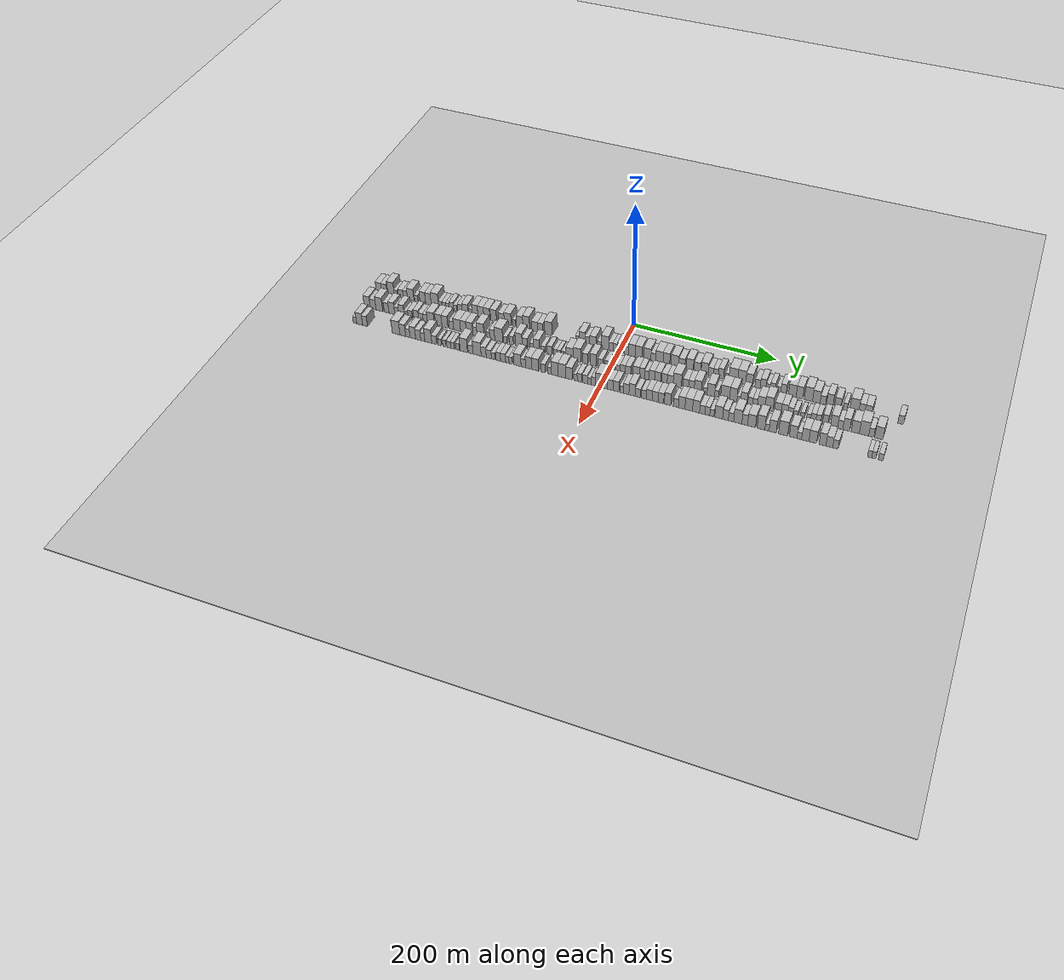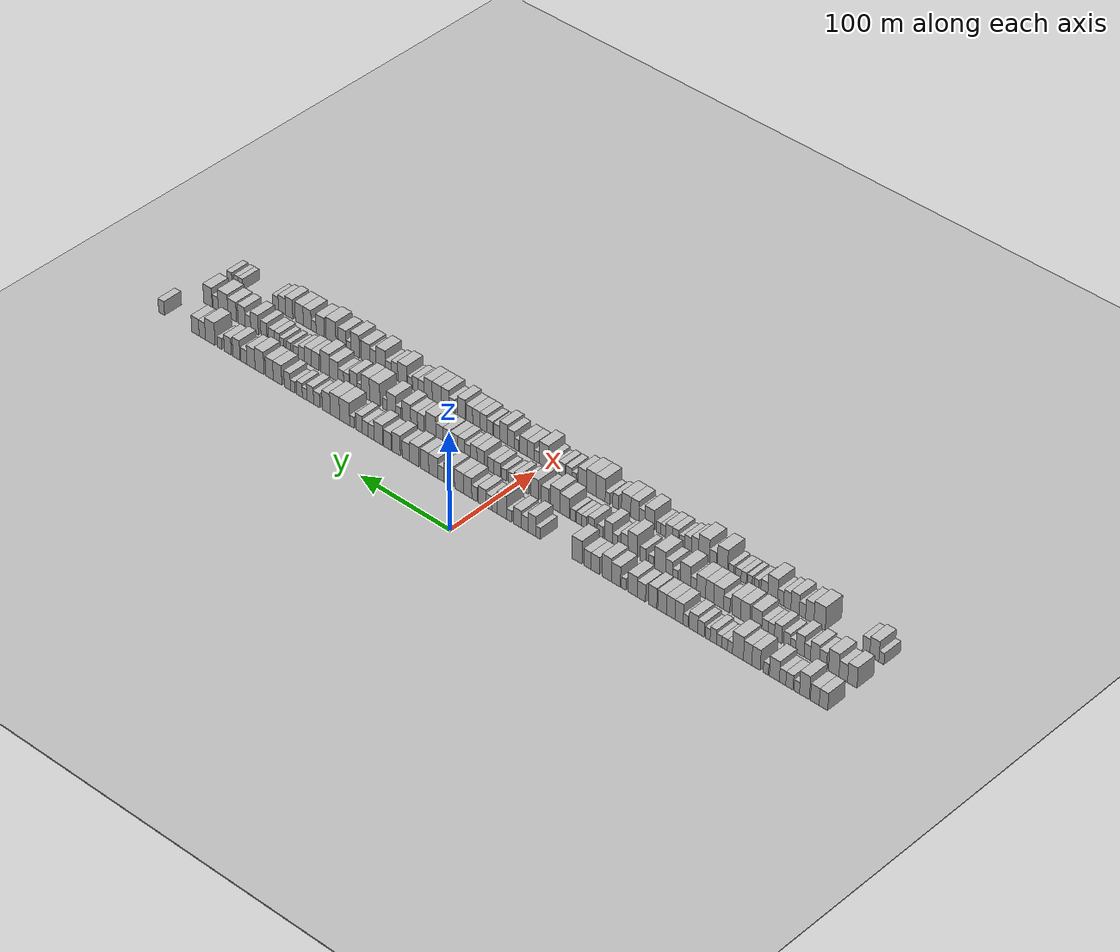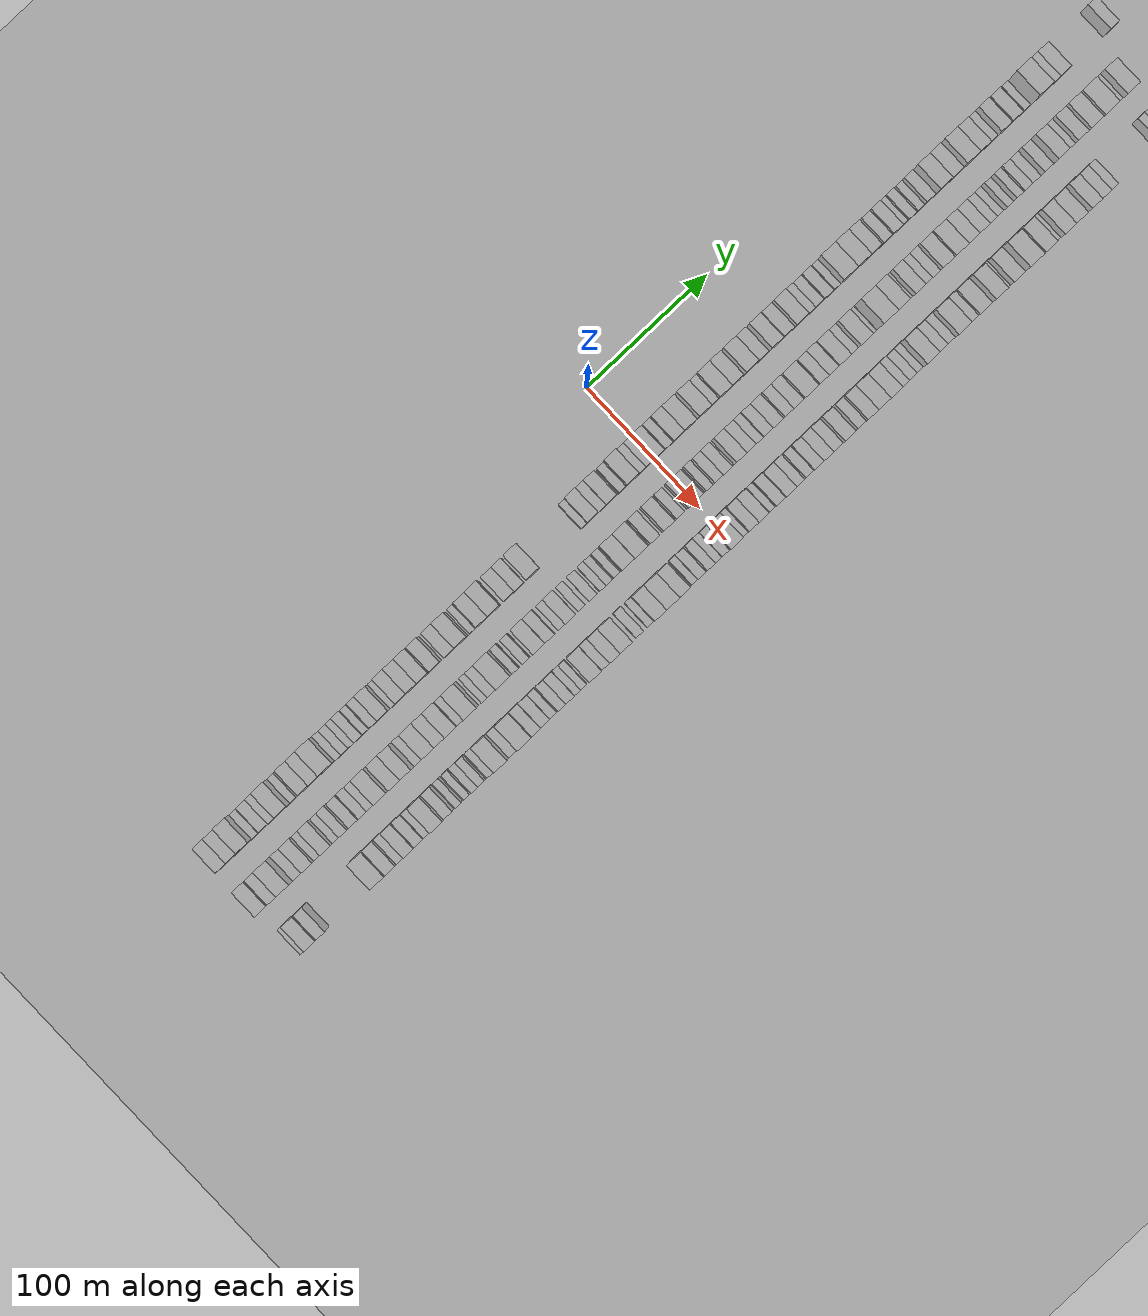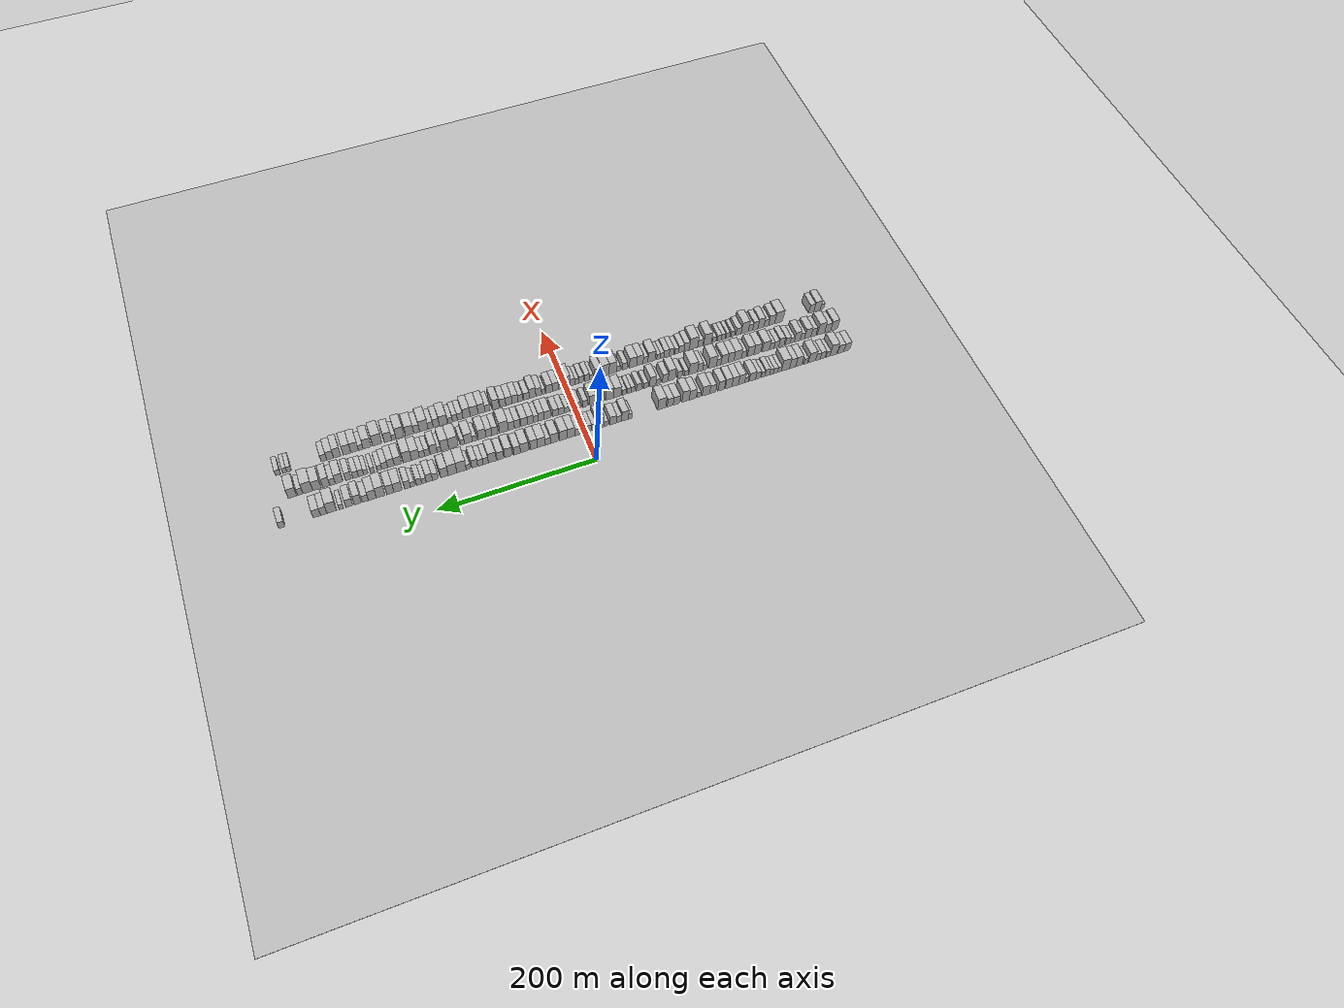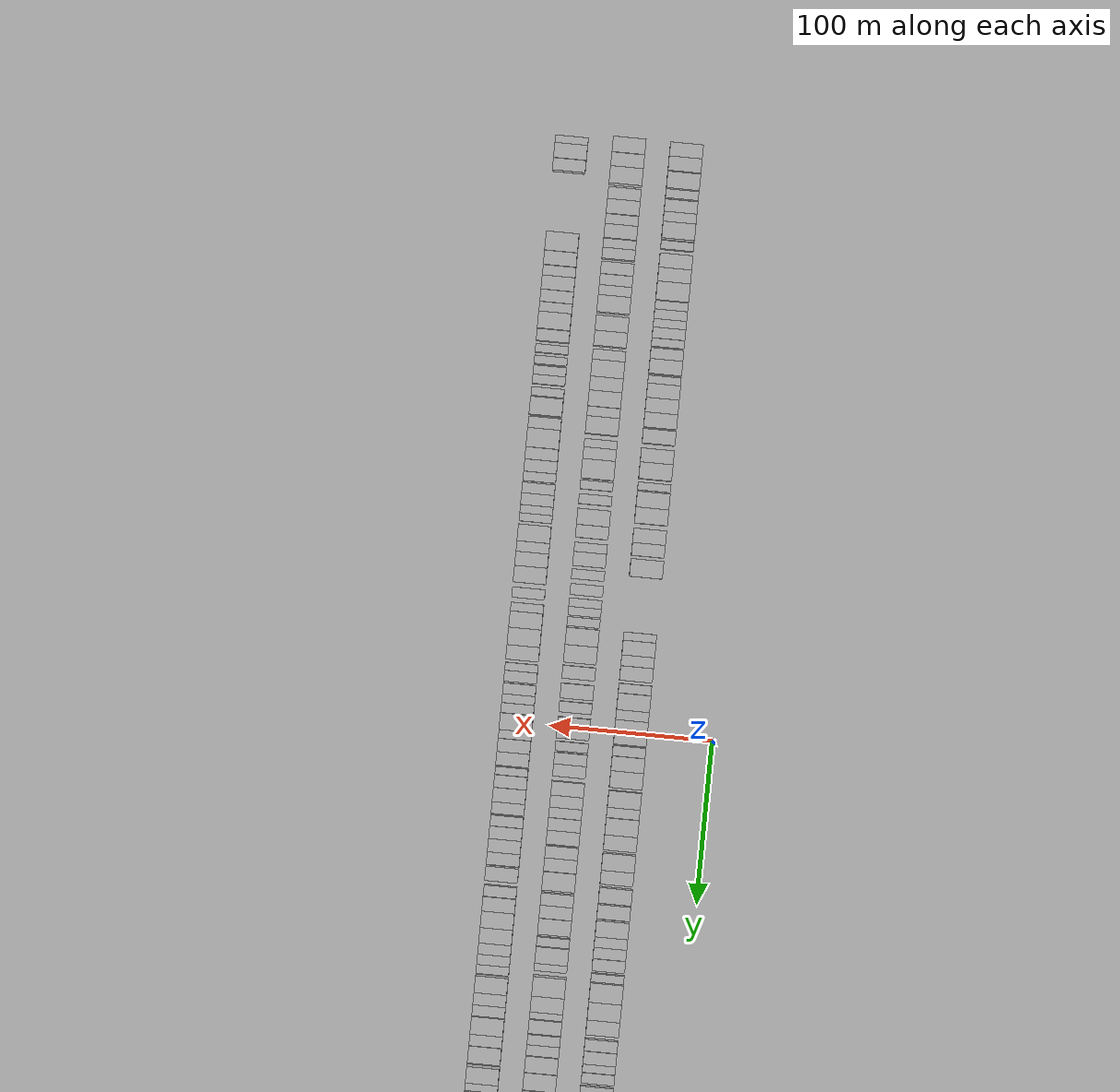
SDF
<?xml version="1.0" encoding="utf-8"?>

<sdf version="1.6">

   <world name="default">

      <gui fullscreen="0">

         <camera name="user_camera">

            <pose>-15 0 4.57585 0 0 0</pose>

            <view_controller>orbit</view_controller>

         </camera>

      </gui>

      <scene>

         <sky>

           <clouds>

             <speed>12</speed>

           </clouds>

         </sky>

         <ambient>0.4 0.4 0.4 1</ambient>

         <background>0.7 0.7 0.7 1</background>

         <shadows>1</shadows>

      </scene>

      <gravity>0 0 -9.8066</gravity>

      <magnetic_field>6e-06 2.3e-05 -4.2e-05</magnetic_field>

      <physics default="0" name="default_physics" type="ode">

         <ode>

            <solver>

               <type>quick</type>

               <iters>10</iters>

               <sor>1.0</sor>

               <use_dynamic_moi_rescaling>0</use_dynamic_moi_rescaling>

            </solver>

            <constraints>

               <cfm>0</cfm>

               <erp>0.2</erp>

               <contact_max_correcting_vel>100</contact_max_correcting_vel>

               <contact_surface_layer>0.001</contact_surface_layer>

            </constraints>

         </ode>

         <max_step_size>0.004</max_step_size>

         <real_time_factor>1</real_time_factor>

         <real_time_update_rate>250</real_time_update_rate>

      </physics>

      <light name="sun" type="directional">

         <cast_shadows>1</cast_shadows>

         <pose>0 0 10 0 0 0</pose>

         <diffuse>0.8 0.8 0.8 1</diffuse>

         <specular>0.2 0.2 0.2 1</specular>

         <attenuation>

            <range>1000</range>

            <constant>0.9</constant>

            <linear>0.01</linear>

            <quadratic>0.001</quadratic>

         </attenuation>

         <direction>-0.5 0.1 -0.9</direction>

      </light>

      <include>

         <name>ground_plane_1</name>

         <uri>model://HANNAS_ground_plane</uri>

         <pose>0 0 0  0 0 0</pose>

      </include>

      <include>

         <name>ground_plane_2</name>

         <uri>model://HANNAS_ground_plane</uri>

         <pose>100 0 0  0 0 0</pose>

      </include>

      <model name="building_1">

         <static>1</static>

         <pose frame="">50.0000 -355.7327 0 0.000000 0.000000 0.000000</pose>

         <link name="link">

            <pose frame="">0 0 9.00 0 0 0</pose>

            <collision name="collision">

               <geometry>

                  <box>

                     <size>20.0000 8.5347 18.0000</size>

                  </box>

               </geometry>

               <max_contacts>10</max_contacts>

               <surface>

                  <contact>

                     <ode/>

                  </contact>

                  <bounce/>

                  <friction>

                     <torsional>

                        <ode/>

                     </torsional>

                     <ode/>

                  </friction>

               </surface>

            </collision>

            <visual name="visual">

               <cast_shadows>0</cast_shadows>

               <geometry>

                  <box>

                     <size>20.0000 8.5347 18.0000</size>

                  </box>

               </geometry>

               <material>

                  <script>

                     <uri>model://HANNAS_wall/materials/scripts</uri>

                     <uri>model://HANNAS_wall/materials/textures</uri>

                     <name>vrc/HANNAS_wall</name>

                  </script>

               </material>

            </visual>

            <self_collide>0</self_collide>

            <enable_wind>0</enable_wind>

            <kinematic>0</kinematic>

         </link>

      </model>

      <model name="building_2">

         <static>1</static>

         <pose frame="">50.0000 -347.1133 0 0.000000 0.000000 0.000000</pose>

         <link name="link">

            <pose frame="">0 0 9.00 0 0 0</pose>

            <collision name="collision">

               <geometry>

                  <box>

                     <size>20.0000 8.7041 18.0000</size>

                  </box>

               </geometry>

               <max_contacts>10</max_contacts>

               <surface>

                  <contact>

                     <ode/>

                  </contact>

                  <bounce/>

                  <friction>

                     <torsional>

                        <ode/>

                     </torsional>

                     <ode/>

                  </friction>

               </surface>

            </collision>

            <visual name="visual">

               <cast_shadows>0</cast_shadows>

               <geometry>

                  <box>

                     <size>20.0000 8.7041 18.0000</size>

                  </box>

               </geometry>

               <material>

                  <script>

                     <uri>model://HANNAS_wall/materials/scripts</uri>

                     <uri>model://HANNAS_wall/materials/textures</uri>

                     <name>vrc/HANNAS_wall</name>

                  </script>

               </material>

            </visual>

            <self_collide>0</self_collide>

            <enable_wind>0</enable_wind>

            <kinematic>0</kinematic>

         </link>

      </model>

      <model name="building_3">

         <static>1</static>

         <pose frame="">50.0000 -336.7683 0 0.000000 0.000000 0.000000</pose>

         <link name="link">

            <pose frame="">0 0 12.00 0 0 0</pose>

            <collision name="collision">

               <geometry>

                  <box>

                     <size>20.0000 9.9859 24.0000</size>

                  </box>

               </geometry>

               <max_contacts>10</max_contacts>

               <surface>

                  <contact>

                     <ode/>

                  </contact>

                  <bounce/>

                  <friction>

                     <torsional>

                        <ode/>

                     </torsional>

                     <ode/>

                  </friction>

               </surface>

            </collision>

            <visual name="visual">

               <cast_shadows>0</cast_shadows>

               <geometry>

                  <box>

                     <size>20.0000 9.9859 24.0000</size>

                  </box>

               </geometry>

               <material>

                  <script>

                     <uri>model://HANNAS_wall/materials/scripts</uri>

                     <uri>model://HANNAS_wall/materials/textures</uri>

                     <name>vrc/HANNAS_wall</name>

                  </script>

               </material>

            </visual>

            <self_collide>0</self_collide>

            <enable_wind>0</enable_wind>

            <kinematic>0</kinematic>

         </link>

      </model>

      <model name="building_4">

         <static>1</static>

         <pose frame="">50.0000 -329.0870 0 0.000000 0.000000 0.000000</pose>

         <link name="link">

            <pose frame="">0 0 6.00 0 0 0</pose>

            <collision name="collision">

               <geometry>

                  <box>

                     <size>20.0000 5.3767 12.0000</size>

                  </box>

               </geometry>

               <max_contacts>10</max_contacts>

               <surface>

                  <contact>

                     <ode/>

                  </contact>

                  <bounce/>

                  <friction>

                     <torsional>

                        <ode/>

                     </torsional>

                     <ode/>

                  </friction>

               </surface>

            </collision>

            <visual name="visual">

               <cast_shadows>0</cast_shadows>

               <geometry>

                  <box>

                     <size>20.0000 5.3767 12.0000</size>

                  </box>

               </geometry>

               <material>

                  <script>

                     <uri>model://HANNAS_wall/materials/scripts</uri>

                     <uri>model://HANNAS_wall/materials/textures</uri>

                     <name>vrc/HANNAS_wall</name>

                  </script>

               </material>

            </visual>

            <self_collide>0</self_collide>

            <enable_wind>0</enable_wind>

            <kinematic>0</kinematic>

         </link>

      </model>

      <model name="building_5">

         <static>1</static>

         <pose frame="">50.0000 -321.6706 0 0.000000 0.000000 0.000000</pose>

         <link name="link">

            <pose frame="">0 0 7.50 0 0 0</pose>

            <collision name="collision">

               <geometry>

                  <box>

                     <size>20.0000 7.4561 15.0000</size>

                  </box>

               </geometry>

               <max_contacts>10</max_contacts>

               <surface>

                  <contact>

                     <ode/>

                  </contact>

                  <bounce/>

                  <friction>

                     <torsional>

                        <ode/>

                     </torsional>

                     <ode/>

                  </friction>

               </surface>

            </collision>

            <visual name="visual">

               <cast_shadows>0</cast_shadows>

               <geometry>

                  <box>

                     <size>20.0000 7.4561 15.0000</size>

                  </box>

               </geometry>

               <material>

                  <script>

                     <uri>model://HANNAS_wall/materials/scripts</uri>

                     <uri>model://HANNAS_wall/materials/textures</uri>

                     <name>vrc/HANNAS_wall</name>

                  </script>

               </material>

            </visual>

            <self_collide>0</self_collide>

            <enable_wind>0</enable_wind>

            <kinematic>0</kinematic>

         </link>

      </model>

      <model name="building_6">

         <static>1</static>

         <pose frame="">50.0000 -314.7482 0 0.000000 0.000000 0.000000</pose>

         <link name="link">

            <pose frame="">0 0 7.50 0 0 0</pose>

            <collision name="collision">

               <geometry>

                  <box>

                     <size>20.0000 6.3887 15.0000</size>

                  </box>

               </geometry>

               <max_contacts>10</max_contacts>

               <surface>

                  <contact>

                     <ode/>

                  </contact>

                  <bounce/>

                  <friction>

                     <torsional>

                        <ode/>

                     </torsional>

                     <ode/>

                  </friction>

               </surface>

            </collision>

            <visual name="visual">

               <cast_shadows>0</cast_shadows>

               <geometry>

                  <box>

                     <size>20.0000 6.3887 15.0000</size>

                  </box>

               </geometry>

               <material>

                  <script>

                     <uri>model://HANNAS_wall/materials/scripts</uri>

                     <uri>model://HANNAS_wall/materials/textures</uri>

                     <name>vrc/HANNAS_wall</name>

                  </script>

               </material>

            </visual>

            <self_collide>0</self_collide>

            <enable_wind>0</enable_wind>

            <kinematic>0</kinematic>

         </link>

      </model>

      <model name="building_7">

         <static>1</static>

         <pose frame="">50.0000 -306.4963 0 0.000000 0.000000 0.000000</pose>

         <link name="link">

            <pose frame="">0 0 10.50 0 0 0</pose>

            <collision name="collision">

               <geometry>

                  <box>

                     <size>20.0000 10.1150 21.0000</size>

                  </box>

               </geometry>

               <max_contacts>10</max_contacts>

               <surface>

                  <contact>

                     <ode/>

                  </contact>

                  <bounce/>

                  <friction>

                     <torsional>

                        <ode/>

                     </torsional>

                     <ode/>

                  </friction>

               </surface>

            </collision>

            <visual name="visual">

               <cast_shadows>0</cast_shadows>

               <geometry>

                  <box>

                     <size>20.0000 10.1150 21.0000</size>

                  </box>

               </geometry>

               <material>

                  <script>

                     <uri>model://HANNAS_wall/materials/scripts</uri>

                     <uri>model://HANNAS_wall/materials/textures</uri>

                     <name>vrc/HANNAS_wall</name>

                  </script>

               </material>

            </visual>

            <self_collide>0</self_collide>

            <enable_wind>0</enable_wind>

            <kinematic>0</kinematic>

         </link>

      </model>

      <model name="building_8">

         <static>1</static>

         <pose frame="">50.0000 -297.8354 0 0.000000 0.000000 0.000000</pose>

         <link name="link">

            <pose frame="">0 0 6.00 0 0 0</pose>

            <collision name="collision">

               <geometry>

                  <box>

                     <size>20.0000 5.2068 12.0000</size>

                  </box>

               </geometry>

               <max_contacts>10</max_contacts>

               <surface>

                  <contact>

                     <ode/>

                  </contact>

                  <bounce/>

                  <friction>

                     <torsional>

                        <ode/>

                     </torsional>

                     <ode/>

                  </friction>

               </surface>

            </collision>

            <visual name="visual">

               <cast_shadows>0</cast_shadows>

               <geometry>

                  <box>

                     <size>20.0000 5.2068 12.0000</size>

                  </box>

               </geometry>

               <material>

                  <script>

                     <uri>model://HANNAS_wall/materials/scripts</uri>

                     <uri>model://HANNAS_wall/materials/textures</uri>

                     <name>vrc/HANNAS_wall</name>

                  </script>

               </material>

            </visual>

            <self_collide>0</self_collide>

            <enable_wind>0</enable_wind>

            <kinematic>0</kinematic>

         </link>

      </model>

      <model name="building_9">

         <static>1</static>

         <pose frame="">50.0000 -287.9012 0 0.000000 0.000000 0.000000</pose>

         <link name="link">

            <pose frame="">0 0 10.50 0 0 0</pose>

            <collision name="collision">

               <geometry>

                  <box>

                     <size>20.0000 8.6617 21.0000</size>

                  </box>

               </geometry>

               <max_contacts>10</max_contacts>

               <surface>

                  <contact>

                     <ode/>

                  </contact>

                  <bounce/>

                  <friction>

                     <torsional>

                        <ode/>

                     </torsional>

                     <ode/>

                  </friction>

               </surface>

            </collision>

            <visual name="visual">

               <cast_shadows>0</cast_shadows>

               <geometry>

                  <box>

                     <size>20.0000 8.6617 21.0000</size>

                  </box>

               </geometry>

               <material>

                  <script>

                     <uri>model://HANNAS_wall/materials/scripts</uri>

                     <uri>model://HANNAS_wall/materials/textures</uri>

                     <name>vrc/HANNAS_wall</name>

                  </script>

               </material>

            </visual>

            <self_collide>0</self_collide>

            <enable_wind>0</enable_wind>

            <kinematic>0</kinematic>

         </link>

      </model>

      <model name="building_10">

         <static>1</static>

         <pose frame="">50.0000 -279.2929 0 0.000000 0.000000 0.000000</pose>

         <link name="link">

            <pose frame="">0 0 10.50 0 0 0</pose>

            <collision name="collision">

               <geometry>

                  <box>

                     <size>20.0000 8.5549 21.0000</size>

                  </box>

               </geometry>

               <max_contacts>10</max_contacts>

               <surface>

                  <contact>

                     <ode/>

                  </contact>

                  <bounce/>

                  <friction>

                     <torsional>

                        <ode/>

                     </torsional>

                     <ode/>

                  </friction>

               </surface>

            </collision>

            <visual name="visual">

               <cast_shadows>0</cast_shadows>

               <geometry>

                  <box>

                     <size>20.0000 8.5549 21.0000</size>

                  </box>

               </geometry>

               <material>

                  <script>

                     <uri>model://HANNAS_wall/materials/scripts</uri>

                     <uri>model://HANNAS_wall/materials/textures</uri>

                     <name>vrc/HANNAS_wall</name>

                  </script>

               </material>

            </visual>

            <self_collide>0</self_collide>

            <enable_wind>0</enable_wind>

            <kinematic>0</kinematic>

         </link>

      </model>

      <model name="building_11">

         <static>1</static>

         <pose frame="">50.0000 -269.3583 0 0.000000 0.000000 0.000000</pose>

         <link name="link">

            <pose frame="">0 0 12.00 0 0 0</pose>

            <collision name="collision">

               <geometry>

                  <box>

                     <size>20.0000 11.3145 24.0000</size>

                  </box>

               </geometry>

               <max_contacts>10</max_contacts>

               <surface>

                  <contact>

                     <ode/>

                  </contact>

                  <bounce/>

                  <friction>

                     <torsional>

                        <ode/>

                     </torsional>

                     <ode/>

                  </friction>

               </surface>

            </collision>

            <visual name="visual">

               <cast_shadows>0</cast_shadows>

               <geometry>

                  <box>

                     <size>20.0000 11.3145 24.0000</size>

                  </box>

               </geometry>

               <material>

                  <script>

                     <uri>model://HANNAS_wall/materials/scripts</uri>

                     <uri>model://HANNAS_wall/materials/textures</uri>

                     <name>vrc/HANNAS_wall</name>

                  </script>

               </material>

            </visual>

            <self_collide>0</self_collide>

            <enable_wind>0</enable_wind>

            <kinematic>0</kinematic>

         </link>

      </model>

      <model name="building_12">

         <static>1</static>

         <pose frame="">50.0000 -261.0914 0 0.000000 0.000000 0.000000</pose>

         <link name="link">

            <pose frame="">0 0 6.00 0 0 0</pose>

            <collision name="collision">

               <geometry>

                  <box>

                     <size>20.0000 5.2192 12.0000</size>

                  </box>

               </geometry>

               <max_contacts>10</max_contacts>

               <surface>

                  <contact>

                     <ode/>

                  </contact>

                  <bounce/>

                  <friction>

                     <torsional>

                        <ode/>

                     </torsional>

                     <ode/>

                  </friction>

               </surface>

            </collision>

            <visual name="visual">

               <cast_shadows>0</cast_shadows>

               <geometry>

                  <box>

                     <size>20.0000 5.2192 12.0000</size>

                  </box>

               </geometry>

               <material>

                  <script>

                     <uri>model://HANNAS_wall/materials/scripts</uri>

                     <uri>model://HANNAS_wall/materials/textures</uri>

                     <name>vrc/HANNAS_wall</name>

                  </script>

               </material>

            </visual>

            <self_collide>0</self_collide>

            <enable_wind>0</enable_wind>

            <kinematic>0</kinematic>

         </link>

      </model>

      <model name="building_13">

         <static>1</static>

         <pose frame="">50.0000 -255.5470 0 0.000000 0.000000 0.000000</pose>

         <link name="link">

            <pose frame="">0 0 6.00 0 0 0</pose>

            <collision name="collision">

               <geometry>

                  <box>

                     <size>20.0000 5.8696 12.0000</size>

                  </box>

               </geometry>

               <max_contacts>10</max_contacts>

               <surface>

                  <contact>

                     <ode/>

                  </contact>

                  <bounce/>

                  <friction>

                     <torsional>

                        <ode/>

                     </torsional>

                     <ode/>

                  </friction>

               </surface>

            </collision>

            <visual name="visual">

               <cast_shadows>0</cast_shadows>

               <geometry>

                  <box>

                     <size>20.0000 5.8696 12.0000</size>

                  </box>

               </geometry>

               <material>

                  <script>

                     <uri>model://HANNAS_wall/materials/scripts</uri>

                     <uri>model://HANNAS_wall/materials/textures</uri>

                     <name>vrc/HANNAS_wall</name>

                  </script>

               </material>

            </visual>

            <self_collide>0</self_collide>

            <enable_wind>0</enable_wind>

            <kinematic>0</kinematic>

         </link>

      </model>

      <model name="building_14">

         <static>1</static>

         <pose frame="">50.0000 -249.9911 0 0.000000 0.000000 0.000000</pose>

         <link name="link">

            <pose frame="">0 0 6.00 0 0 0</pose>

            <collision name="collision">

               <geometry>

                  <box>

                     <size>20.0000 5.2421 12.0000</size>

                  </box>

               </geometry>

               <max_contacts>10</max_contacts>

               <surface>

                  <contact>

                     <ode/>

                  </contact>

                  <bounce/>

                  <friction>

                     <torsional>

                        <ode/>

                     </torsional>

                     <ode/>

                  </friction>

               </surface>

            </collision>

            <visual name="visual">

               <cast_shadows>0</cast_shadows>

               <geometry>

                  <box>

                     <size>20.0000 5.2421 12.0000</size>

                  </box>

               </geometry>

               <material>

                  <script>

                     <uri>model://HANNAS_wall/materials/scripts</uri>

                     <uri>model://HANNAS_wall/materials/textures</uri>

                     <name>vrc/HANNAS_wall</name>

                  </script>

               </material>

            </visual>

            <self_collide>0</self_collide>

            <enable_wind>0</enable_wind>

            <kinematic>0</kinematic>

         </link>

      </model>

      <model name="building_15">

         <static>1</static>

         <pose frame="">50.0000 -244.0857 0 0.000000 0.000000 0.000000</pose>

         <link name="link">

            <pose frame="">0 0 7.50 0 0 0</pose>

            <collision name="collision">

               <geometry>

                  <box>

                     <size>20.0000 6.5687 15.0000</size>

                  </box>

               </geometry>

               <max_contacts>10</max_contacts>

               <surface>

                  <contact>

                     <ode/>

                  </contact>

                  <bounce/>

                  <friction>

                     <torsional>

                        <ode/>

                     </torsional>

                     <ode/>

                  </friction>

               </surface>

            </collision>

            <visual name="visual">

               <cast_shadows>0</cast_shadows>

               <geometry>

                  <box>

                     <size>20.0000 6.5687 15.0000</size>

                  </box>

               </geometry>

               <material>

                  <script>

                     <uri>model://HANNAS_wall/materials/scripts</uri>

                     <uri>model://HANNAS_wall/materials/textures</uri>

                     <name>vrc/HANNAS_wall</name>

                  </script>

               </material>

            </visual>

            <self_collide>0</self_collide>

            <enable_wind>0</enable_wind>

            <kinematic>0</kinematic>

         </link>

      </model>

      <model name="building_16">

         <static>1</static>

         <pose frame="">50.0000 -238.2867 0 0.000000 0.000000 0.000000</pose>

         <link name="link">

            <pose frame="">0 0 6.00 0 0 0</pose>

            <collision name="collision">

               <geometry>

                  <box>

                     <size>20.0000 5.0294 12.0000</size>

                  </box>

               </geometry>

               <max_contacts>10</max_contacts>

               <surface>

                  <contact>

                     <ode/>

                  </contact>

                  <bounce/>

                  <friction>

                     <torsional>

                        <ode/>

                     </torsional>

                     <ode/>

                  </friction>

               </surface>

            </collision>

            <visual name="visual">

               <cast_shadows>0</cast_shadows>

               <geometry>

                  <box>

                     <size>20.0000 5.0294 12.0000</size>

                  </box>

               </geometry>

               <material>

                  <script>

                     <uri>model://HANNAS_wall/materials/scripts</uri>

                     <uri>model://HANNAS_wall/materials/textures</uri>

                     <name>vrc/HANNAS_wall</name>

                  </script>

               </material>

            </visual>

            <self_collide>0</self_collide>

            <enable_wind>0</enable_wind>

            <kinematic>0</kinematic>

         </link>

      </model>

      <model name="building_17">

         <static>1</static>

         <pose frame="">50.0000 -231.4063 0 0.000000 0.000000 0.000000</pose>

         <link name="link">

            <pose frame="">0 0 7.50 0 0 0</pose>

            <collision name="collision">

               <geometry>

                  <box>

                     <size>20.0000 6.7313 15.0000</size>

                  </box>

               </geometry>

               <max_contacts>10</max_contacts>

               <surface>

                  <contact>

                     <ode/>

                  </contact>

                  <bounce/>

                  <friction>

                     <torsional>

                        <ode/>

                     </torsional>

                     <ode/>

                  </friction>

               </surface>

            </collision>

            <visual name="visual">

               <cast_shadows>0</cast_shadows>

               <geometry>

                  <box>

                     <size>20.0000 6.7313 15.0000</size>

                  </box>

               </geometry>

               <material>

                  <script>

                     <uri>model://HANNAS_wall/materials/scripts</uri>

                     <uri>model://HANNAS_wall/materials/textures</uri>

                     <name>vrc/HANNAS_wall</name>

                  </script>

               </material>

            </visual>

            <self_collide>0</self_collide>

            <enable_wind>0</enable_wind>

            <kinematic>0</kinematic>

         </link>

      </model>

      <model name="building_18">

         <static>1</static>

         <pose frame="">50.0000 -223.5605 0 0.000000 0.000000 0.000000</pose>

         <link name="link">

            <pose frame="">0 0 9.00 0 0 0</pose>

            <collision name="collision">

               <geometry>

                  <box>

                     <size>20.0000 8.9602 18.0000</size>

                  </box>

               </geometry>

               <max_contacts>10</max_contacts>

               <surface>

                  <contact>

                     <ode/>

                  </contact>

                  <bounce/>

                  <friction>

                     <torsional>

                        <ode/>

                     </torsional>

                     <ode/>

                  </friction>

               </surface>

            </collision>

            <visual name="visual">

               <cast_shadows>0</cast_shadows>

               <geometry>

                  <box>

                     <size>20.0000 8.9602 18.0000</size>

                  </box>

               </geometry>

               <material>

                  <script>

                     <uri>model://HANNAS_wall/materials/scripts</uri>

                     <uri>model://HANNAS_wall/materials/textures</uri>

                     <name>vrc/HANNAS_wall</name>

                  </script>

               </material>

            </visual>

            <self_collide>0</self_collide>

            <enable_wind>0</enable_wind>

            <kinematic>0</kinematic>

         </link>

      </model>

      <model name="building_19">

         <static>1</static>

         <pose frame="">50.0000 -215.5207 0 0.000000 0.000000 0.000000</pose>

         <link name="link">

            <pose frame="">0 0 6.00 0 0 0</pose>

            <collision name="collision">

               <geometry>

                  <box>

                     <size>20.0000 5.1194 12.0000</size>

                  </box>

               </geometry>

               <max_contacts>10</max_contacts>

               <surface>

                  <contact>

                     <ode/>

                  </contact>

                  <bounce/>

                  <friction>

                     <torsional>

                        <ode/>

                     </torsional>

                     <ode/>

                  </friction>

               </surface>

            </collision>

            <visual name="visual">

               <cast_shadows>0</cast_shadows>

               <geometry>

                  <box>

                     <size>20.0000 5.1194 12.0000</size>

                  </box>

               </geometry>

               <material>

                  <script>

                     <uri>model://HANNAS_wall/materials/scripts</uri>

                     <uri>model://HANNAS_wall/materials/textures</uri>

                     <name>vrc/HANNAS_wall</name>

                  </script>

               </material>

            </visual>

            <self_collide>0</self_collide>

            <enable_wind>0</enable_wind>

            <kinematic>0</kinematic>

         </link>

      </model>

      <model name="building_20">

         <static>1</static>

         <pose frame="">50.0000 -208.6274 0 0.000000 0.000000 0.000000</pose>

         <link name="link">

            <pose frame="">0 0 10.50 0 0 0</pose>

            <collision name="collision">

               <geometry>

                  <box>

                     <size>20.0000 8.6672 21.0000</size>

                  </box>

               </geometry>

               <max_contacts>10</max_contacts>

               <surface>

                  <contact>

                     <ode/>

                  </contact>

                  <bounce/>

                  <friction>

                     <torsional>

                        <ode/>

                     </torsional>

                     <ode/>

                  </friction>

               </surface>

            </collision>

            <visual name="visual">

               <cast_shadows>0</cast_shadows>

               <geometry>

                  <box>

                     <size>20.0000 8.6672 21.0000</size>

                  </box>

               </geometry>

               <material>

                  <script>

                     <uri>model://HANNAS_wall/materials/scripts</uri>

                     <uri>model://HANNAS_wall/materials/textures</uri>

                     <name>vrc/HANNAS_wall</name>

                  </script>

               </material>

            </visual>

            <self_collide>0</self_collide>

            <enable_wind>0</enable_wind>

            <kinematic>0</kinematic>

         </link>

      </model>

      <model name="building_21">

         <static>1</static>

         <pose frame="">50.0000 -199.8537 0 0.000000 0.000000 0.000000</pose>

         <link name="link">

            <pose frame="">0 0 10.50 0 0 0</pose>

            <collision name="collision">

               <geometry>

                  <box>

                     <size>20.0000 8.8801 21.0000</size>

                  </box>

               </geometry>

               <max_contacts>10</max_contacts>

               <surface>

                  <contact>

                     <ode/>

                  </contact>

                  <bounce/>

                  <friction>

                     <torsional>

                        <ode/>

                     </torsional>

                     <ode/>

                  </friction>

               </surface>

            </collision>

            <visual name="visual">

               <cast_shadows>0</cast_shadows>

               <geometry>

                  <box>

                     <size>20.0000 8.8801 21.0000</size>

                  </box>

               </geometry>

               <material>

                  <script>

                     <uri>model://HANNAS_wall/materials/scripts</uri>

                     <uri>model://HANNAS_wall/materials/textures</uri>

                     <name>vrc/HANNAS_wall</name>

                  </script>

               </material>

            </visual>

            <self_collide>0</self_collide>

            <enable_wind>0</enable_wind>

            <kinematic>0</kinematic>

         </link>

      </model>

      <model name="building_22">

         <static>1</static>

         <pose frame="">50.0000 -190.8457 0 0.000000 0.000000 0.000000</pose>

         <link name="link">

            <pose frame="">0 0 10.50 0 0 0</pose>

            <collision name="collision">

               <geometry>

                  <box>

                     <size>20.0000 9.1359 21.0000</size>

                  </box>

               </geometry>

               <max_contacts>10</max_contacts>

               <surface>

                  <contact>

                     <ode/>

                  </contact>

                  <bounce/>

                  <friction>

                     <torsional>

                        <ode/>

                     </torsional>

                     <ode/>

                  </friction>

               </surface>

            </collision>

            <visual name="visual">

               <cast_shadows>0</cast_shadows>

               <geometry>

                  <box>

                     <size>20.0000 9.1359 21.0000</size>

                  </box>

               </geometry>

               <material>

                  <script>

                     <uri>model://HANNAS_wall/materials/scripts</uri>

                     <uri>model://HANNAS_wall/materials/textures</uri>

                     <name>vrc/HANNAS_wall</name>

                  </script>

               </material>

            </visual>

            <self_collide>0</self_collide>

            <enable_wind>0</enable_wind>

            <kinematic>0</kinematic>

         </link>

      </model>

      <model name="building_23">

         <static>1</static>

         <pose frame="">50.0000 -180.9053 0 0.000000 0.000000 0.000000</pose>

         <link name="link">

            <pose frame="">0 0 10.50 0 0 0</pose>

            <collision name="collision">

               <geometry>

                  <box>

                     <size>20.0000 8.7450 21.0000</size>

                  </box>

               </geometry>

               <max_contacts>10</max_contacts>

               <surface>

                  <contact>

                     <ode/>

                  </contact>

                  <bounce/>

                  <friction>

                     <torsional>

                        <ode/>

                     </torsional>

                     <ode/>

                  </friction>

               </surface>

            </collision>

            <visual name="visual">

               <cast_shadows>0</cast_shadows>

               <geometry>

                  <box>

                     <size>20.0000 8.7450 21.0000</size>

                  </box>

               </geometry>

               <material>

                  <script>

                     <uri>model://HANNAS_wall/materials/scripts</uri>

                     <uri>model://HANNAS_wall/materials/textures</uri>

                     <name>vrc/HANNAS_wall</name>

                  </script>

               </material>

            </visual>

            <self_collide>0</self_collide>

            <enable_wind>0</enable_wind>

            <kinematic>0</kinematic>

         </link>

      </model>

      <model name="building_24">

         <static>1</static>

         <pose frame="">50.0000 -169.2547 0 0.000000 0.000000 0.000000</pose>

         <link name="link">

            <pose frame="">0 0 9.00 0 0 0</pose>

            <collision name="collision">

               <geometry>

                  <box>

                     <size>20.0000 8.5562 18.0000</size>

                  </box>

               </geometry>

               <max_contacts>10</max_contacts>

               <surface>

                  <contact>

                     <ode/>

                  </contact>

                  <bounce/>

                  <friction>

                     <torsional>

                        <ode/>

                     </torsional>

                     <ode/>

                  </friction>

               </surface>

            </collision>

            <visual name="visual">

               <cast_shadows>0</cast_shadows>

               <geometry>

                  <box>

                     <size>20.0000 8.5562 18.0000</size>

                  </box>

               </geometry>

               <material>

                  <script>

                     <uri>model://HANNAS_wall/materials/scripts</uri>

                     <uri>model://HANNAS_wall/materials/textures</uri>

                     <name>vrc/HANNAS_wall</name>

                  </script>

               </material>

            </visual>

            <self_collide>0</self_collide>

            <enable_wind>0</enable_wind>

            <kinematic>0</kinematic>

         </link>

      </model>

      <model name="building_25">

         <static>1</static>

         <pose frame="">50.0000 -159.9350 0 0.000000 0.000000 0.000000</pose>

         <link name="link">

            <pose frame="">0 0 10.50 0 0 0</pose>

            <collision name="collision">

               <geometry>

                  <box>

                     <size>20.0000 10.0831 21.0000</size>

                  </box>

               </geometry>

               <max_contacts>10</max_contacts>

               <surface>

                  <contact>

                     <ode/>

                  </contact>

                  <bounce/>

                  <friction>

                     <torsional>

                        <ode/>

                     </torsional>

                     <ode/>

                  </friction>

               </surface>

            </collision>

            <visual name="visual">

               <cast_shadows>0</cast_shadows>

               <geometry>

                  <box>

                     <size>20.0000 10.0831 21.0000</size>

                  </box>

               </geometry>

               <material>

                  <script>

                     <uri>model://HANNAS_wall/materials/scripts</uri>

                     <uri>model://HANNAS_wall/materials/textures</uri>

                     <name>vrc/HANNAS_wall</name>

                  </script>

               </material>

            </visual>

            <self_collide>0</self_collide>

            <enable_wind>0</enable_wind>

            <kinematic>0</kinematic>

         </link>

      </model>

      <model name="building_26">

         <static>1</static>

         <pose frame="">50.0000 -150.4912 0 0.000000 0.000000 0.000000</pose>

         <link name="link">

            <pose frame="">0 0 6.00 0 0 0</pose>

            <collision name="collision">

               <geometry>

                  <box>

                     <size>20.0000 4.8045 12.0000</size>

                  </box>

               </geometry>

               <max_contacts>10</max_contacts>

               <surface>

                  <contact>

                     <ode/>

                  </contact>

                  <bounce/>

                  <friction>

                     <torsional>

                        <ode/>

                     </torsional>

                     <ode/>

                  </friction>

               </surface>

            </collision>

            <visual name="visual">

               <cast_shadows>0</cast_shadows>

               <geometry>

                  <box>

                     <size>20.0000 4.8045 12.0000</size>

                  </box>

               </geometry>

               <material>

                  <script>

                     <uri>model://HANNAS_wall/materials/scripts</uri>

                     <uri>model://HANNAS_wall/materials/textures</uri>

                     <name>vrc/HANNAS_wall</name>

                  </script>

               </material>

            </visual>

            <self_collide>0</self_collide>

            <enable_wind>0</enable_wind>

            <kinematic>0</kinematic>

         </link>

      </model>

      <model name="building_27">

         <static>1</static>

         <pose frame="">50.0000 -142.2835 0 0.000000 0.000000 0.000000</pose>

         <link name="link">

            <pose frame="">0 0 10.50 0 0 0</pose>

            <collision name="collision">

               <geometry>

                  <box>

                     <size>20.0000 9.6110 21.0000</size>

                  </box>

               </geometry>

               <max_contacts>10</max_contacts>

               <surface>

                  <contact>

                     <ode/>

                  </contact>

                  <bounce/>

                  <friction>

                     <torsional>

                        <ode/>

                     </torsional>

                     <ode/>

                  </friction>

               </surface>

            </collision>

            <visual name="visual">

               <cast_shadows>0</cast_shadows>

               <geometry>

                  <box>

                     <size>20.0000 9.6110 21.0000</size>

                  </box>

               </geometry>

               <material>

                  <script>

                     <uri>model://HANNAS_wall/materials/scripts</uri>

                     <uri>model://HANNAS_wall/materials/textures</uri>

                     <name>vrc/HANNAS_wall</name>

                  </script>

               </material>

            </visual>

            <self_collide>0</self_collide>

            <enable_wind>0</enable_wind>

            <kinematic>0</kinematic>

         </link>

      </model>

      <model name="building_28">

         <static>1</static>

         <pose frame="">50.0000 -132.5884 0 0.000000 0.000000 0.000000</pose>

         <link name="link">

            <pose frame="">0 0 12.00 0 0 0</pose>

            <collision name="collision">

               <geometry>

                  <box>

                     <size>20.0000 9.7791 24.0000</size>

                  </box>

               </geometry>

               <max_contacts>10</max_contacts>

               <surface>

                  <contact>

                     <ode/>

                  </contact>

                  <bounce/>

                  <friction>

                     <torsional>

                        <ode/>

                     </torsional>

                     <ode/>

                  </friction>

               </surface>

            </collision>

            <visual name="visual">

               <cast_shadows>0</cast_shadows>

               <geometry>

                  <box>

                     <size>20.0000 9.7791 24.0000</size>

                  </box>

               </geometry>

               <material>

                  <script>

                     <uri>model://HANNAS_wall/materials/scripts</uri>

                     <uri>model://HANNAS_wall/materials/textures</uri>

                     <name>vrc/HANNAS_wall</name>

                  </script>

               </material>

            </visual>

            <self_collide>0</self_collide>

            <enable_wind>0</enable_wind>

            <kinematic>0</kinematic>

         </link>

      </model>

      <model name="building_29">

         <static>1</static>

         <pose frame="">50.0000 -120.2883 0 0.000000 0.000000 0.000000</pose>

         <link name="link">

            <pose frame="">0 0 9.00 0 0 0</pose>

            <collision name="collision">

               <geometry>

                  <box>

                     <size>20.0000 8.8212 18.0000</size>

                  </box>

               </geometry>

               <max_contacts>10</max_contacts>

               <surface>

                  <contact>

                     <ode/>

                  </contact>

                  <bounce/>

                  <friction>

                     <torsional>

                        <ode/>

                     </torsional>

                     <ode/>

                  </friction>

               </surface>

            </collision>

            <visual name="visual">

               <cast_shadows>0</cast_shadows>

               <geometry>

                  <box>

                     <size>20.0000 8.8212 18.0000</size>

                  </box>

               </geometry>

               <material>

                  <script>

                     <uri>model://HANNAS_wall/materials/scripts</uri>

                     <uri>model://HANNAS_wall/materials/textures</uri>

                     <name>vrc/HANNAS_wall</name>

                  </script>

               </material>

            </visual>

            <self_collide>0</self_collide>

            <enable_wind>0</enable_wind>

            <kinematic>0</kinematic>

         </link>

      </model>

      <model name="building_30">

         <static>1</static>

         <pose frame="">50.0000 -111.9730 0 0.000000 0.000000 0.000000</pose>

         <link name="link">

            <pose frame="">0 0 9.00 0 0 0</pose>

            <collision name="collision">

               <geometry>

                  <box>

                     <size>20.0000 7.8093 18.0000</size>

                  </box>

               </geometry>

               <max_contacts>10</max_contacts>

               <surface>

                  <contact>

                     <ode/>

                  </contact>

                  <bounce/>

                  <friction>

                     <torsional>

                        <ode/>

                     </torsional>

                     <ode/>

                  </friction>

               </surface>

            </collision>

            <visual name="visual">

               <cast_shadows>0</cast_shadows>

               <geometry>

                  <box>

                     <size>20.0000 7.8093 18.0000</size>

                  </box>

               </geometry>

               <material>

                  <script>

                     <uri>model://HANNAS_wall/materials/scripts</uri>

                     <uri>model://HANNAS_wall/materials/textures</uri>

                     <name>vrc/HANNAS_wall</name>

                  </script>

               </material>

            </visual>

            <self_collide>0</self_collide>

            <enable_wind>0</enable_wind>

            <kinematic>0</kinematic>

         </link>

      </model>

      <model name="building_31">

         <static>1</static>

         <pose frame="">50.0000 -100.6690 0 0.000000 0.000000 0.000000</pose>

         <link name="link">

            <pose frame="">0 0 12.00 0 0 0</pose>

            <collision name="collision">

               <geometry>

                  <box>

                     <size>20.0000 10.7988 24.0000</size>

                  </box>

               </geometry>

               <max_contacts>10</max_contacts>

               <surface>

                  <contact>

                     <ode/>

                  </contact>

                  <bounce/>

                  <friction>

                     <torsional>

                        <ode/>

                     </torsional>

                     <ode/>

                  </friction>

               </surface>

            </collision>

            <visual name="visual">

               <cast_shadows>0</cast_shadows>

               <geometry>

                  <box>

                     <size>20.0000 10.7988 24.0000</size>

                  </box>

               </geometry>

               <material>

                  <script>

                     <uri>model://HANNAS_wall/materials/scripts</uri>

                     <uri>model://HANNAS_wall/materials/textures</uri>

                     <name>vrc/HANNAS_wall</name>

                  </script>

               </material>

            </visual>

            <self_collide>0</self_collide>

            <enable_wind>0</enable_wind>

            <kinematic>0</kinematic>

         </link>

      </model>

      <model name="building_32">

         <static>1</static>

         <pose frame="">50.0000 -58.7808 0 0.000000 0.000000 0.000000</pose>

         <link name="link">

            <pose frame="">0 0 6.00 0 0 0</pose>

            <collision name="collision">

               <geometry>

                  <box>

                     <size>20.0000 4.9926 12.0000</size>

                  </box>

               </geometry>

               <max_contacts>10</max_contacts>

               <surface>

                  <contact>

                     <ode/>

                  </contact>

                  <bounce/>

                  <friction>

                     <torsional>

                        <ode/>

                     </torsional>

                     <ode/>

                  </friction>

               </surface>

            </collision>

            <visual name="visual">

               <cast_shadows>0</cast_shadows>

               <geometry>

                  <box>

                     <size>20.0000 4.9926 12.0000</size>

                  </box>

               </geometry>

               <material>

                  <script>

                     <uri>model://HANNAS_wall/materials/scripts</uri>

                     <uri>model://HANNAS_wall/materials/textures</uri>

                     <name>vrc/HANNAS_wall</name>

                  </script>

               </material>

            </visual>

            <self_collide>0</self_collide>

            <enable_wind>0</enable_wind>

            <kinematic>0</kinematic>

         </link>

      </model>

      <model name="building_33">

         <static>1</static>

         <pose frame="">50.0000 -51.8404 0 0.000000 0.000000 0.000000</pose>

         <link name="link">

            <pose frame="">0 0 10.50 0 0 0</pose>

            <collision name="collision">

               <geometry>

                  <box>

                     <size>20.0000 8.8882 21.0000</size>

                  </box>

               </geometry>

               <max_contacts>10</max_contacts>

               <surface>

                  <contact>

                     <ode/>

                  </contact>

                  <bounce/>

                  <friction>

                     <torsional>

                        <ode/>

                     </torsional>

                     <ode/>

                  </friction>

               </surface>

            </collision>

            <visual name="visual">

               <cast_shadows>0</cast_shadows>

               <geometry>

                  <box>

                     <size>20.0000 8.8882 21.0000</size>

                  </box>

               </geometry>

               <material>

                  <script>

                     <uri>model://HANNAS_wall/materials/scripts</uri>

                     <uri>model://HANNAS_wall/materials/textures</uri>

                     <name>vrc/HANNAS_wall</name>

                  </script>

               </material>

            </visual>

            <self_collide>0</self_collide>

            <enable_wind>0</enable_wind>

            <kinematic>0</kinematic>

         </link>

      </model>

      <model name="building_34">

         <static>1</static>

         <pose frame="">50.0000 -44.0674 0 0.000000 0.000000 0.000000</pose>

         <link name="link">

            <pose frame="">0 0 7.50 0 0 0</pose>

            <collision name="collision">

               <geometry>

                  <box>

                     <size>20.0000 6.6578 15.0000</size>

                  </box>

               </geometry>

               <max_contacts>10</max_contacts>

               <surface>

                  <contact>

                     <ode/>

                  </contact>

                  <bounce/>

                  <friction>

                     <torsional>

                        <ode/>

                     </torsional>

                     <ode/>

                  </friction>

               </surface>

            </collision>

            <visual name="visual">

               <cast_shadows>0</cast_shadows>

               <geometry>

                  <box>

                     <size>20.0000 6.6578 15.0000</size>

                  </box>

               </geometry>

               <material>

                  <script>

                     <uri>model://HANNAS_wall/materials/scripts</uri>

                     <uri>model://HANNAS_wall/materials/textures</uri>

                     <name>vrc/HANNAS_wall</name>

                  </script>

               </material>

            </visual>

            <self_collide>0</self_collide>

            <enable_wind>0</enable_wind>

            <kinematic>0</kinematic>

         </link>

      </model>

      <model name="building_35">

         <static>1</static>

         <pose frame="">50.0000 -36.3463 0 0.000000 0.000000 0.000000</pose>

         <link name="link">

            <pose frame="">0 0 9.00 0 0 0</pose>

            <collision name="collision">

               <geometry>

                  <box>

                     <size>20.0000 8.7845 18.0000</size>

                  </box>

               </geometry>

               <max_contacts>10</max_contacts>

               <surface>

                  <contact>

                     <ode/>

                  </contact>

                  <bounce/>

                  <friction>

                     <torsional>

                        <ode/>

                     </torsional>

                     <ode/>

                  </friction>

               </surface>

            </collision>

            <visual name="visual">

               <cast_shadows>0</cast_shadows>

               <geometry>

                  <box>

                     <size>20.0000 8.7845 18.0000</size>

                  </box>

               </geometry>

               <material>

                  <script>

                     <uri>model://HANNAS_wall/materials/scripts</uri>

                     <uri>model://HANNAS_wall/materials/textures</uri>

                     <name>vrc/HANNAS_wall</name>

                  </script>

               </material>

            </visual>

            <self_collide>0</self_collide>

            <enable_wind>0</enable_wind>

            <kinematic>0</kinematic>

         </link>

      </model>

      <model name="building_36">

         <static>1</static>

         <pose frame="">50.0000 -27.0711 0 0.000000 0.000000 0.000000</pose>

         <link name="link">

            <pose frame="">0 0 6.00 0 0 0</pose>

            <collision name="collision">

               <geometry>

                  <box>

                     <size>20.0000 5.7659 12.0000</size>

                  </box>

               </geometry>

               <max_contacts>10</max_contacts>

               <surface>

                  <contact>

                     <ode/>

                  </contact>

                  <bounce/>

                  <friction>

                     <torsional>

                        <ode/>

                     </torsional>

                     <ode/>

                  </friction>

               </surface>

            </collision>

            <visual name="visual">

               <cast_shadows>0</cast_shadows>

               <geometry>

                  <box>

                     <size>20.0000 5.7659 12.0000</size>

                  </box>

               </geometry>

               <material>

                  <script>

                     <uri>model://HANNAS_wall/materials/scripts</uri>

                     <uri>model://HANNAS_wall/materials/textures</uri>

                     <name>vrc/HANNAS_wall</name>

                  </script>

               </material>

            </visual>

            <self_collide>0</self_collide>

            <enable_wind>0</enable_wind>

            <kinematic>0</kinematic>

         </link>

      </model>

      <model name="building_37">

         <static>1</static>

         <pose frame="">50.0000 -19.1407 0 0.000000 0.000000 0.000000</pose>

         <link name="link">

            <pose frame="">0 0 12.00 0 0 0</pose>

            <collision name="collision">

               <geometry>

                  <box>

                     <size>20.0000 10.0950 24.0000</size>

                  </box>

               </geometry>

               <max_contacts>10</max_contacts>

               <surface>

                  <contact>

                     <ode/>

                  </contact>

                  <bounce/>

                  <friction>

                     <torsional>

                        <ode/>

                     </torsional>

                     <ode/>

                  </friction>

               </surface>

            </collision>

            <visual name="visual">

               <cast_shadows>0</cast_shadows>

               <geometry>

                  <box>

                     <size>20.0000 10.0950 24.0000</size>

                  </box>

               </geometry>

               <material>

                  <script>

                     <uri>model://HANNAS_wall/materials/scripts</uri>

                     <uri>model://HANNAS_wall/materials/textures</uri>

                     <name>vrc/HANNAS_wall</name>

                  </script>

               </material>

            </visual>

            <self_collide>0</self_collide>

            <enable_wind>0</enable_wind>

            <kinematic>0</kinematic>

         </link>

      </model>

      <model name="building_38">

         <static>1</static>

         <pose frame="">50.0000 -10.9918 0 0.000000 0.000000 0.000000</pose>

         <link name="link">

            <pose frame="">0 0 7.50 0 0 0</pose>

            <collision name="collision">

               <geometry>

                  <box>

                     <size>20.0000 6.2028 15.0000</size>

                  </box>

               </geometry>

               <max_contacts>10</max_contacts>

               <surface>

                  <contact>

                     <ode/>

                  </contact>

                  <bounce/>

                  <friction>

                     <torsional>

                        <ode/>

                     </torsional>

                     <ode/>

                  </friction>

               </surface>

            </collision>

            <visual name="visual">

               <cast_shadows>0</cast_shadows>

               <geometry>

                  <box>

                     <size>20.0000 6.2028 15.0000</size>

                  </box>

               </geometry>

               <material>

                  <script>

                     <uri>model://HANNAS_wall/materials/scripts</uri>

                     <uri>model://HANNAS_wall/materials/textures</uri>

                     <name>vrc/HANNAS_wall</name>

                  </script>

               </material>

            </visual>

            <self_collide>0</self_collide>

            <enable_wind>0</enable_wind>

            <kinematic>0</kinematic>

         </link>

      </model>

      <model name="building_39">

         <static>1</static>

         <pose frame="">50.0000 -4.8313 0 0.000000 0.000000 0.000000</pose>

         <link name="link">

            <pose frame="">0 0 7.50 0 0 0</pose>

            <collision name="collision">

               <geometry>

                  <box>

                     <size>20.0000 6.1182 15.0000</size>

                  </box>

               </geometry>

               <max_contacts>10</max_contacts>

               <surface>

                  <contact>

                     <ode/>

                  </contact>

                  <bounce/>

                  <friction>

                     <torsional>

                        <ode/>

                     </torsional>

                     <ode/>

                  </friction>

               </surface>

            </collision>

            <visual name="visual">

               <cast_shadows>0</cast_shadows>

               <geometry>

                  <box>

                     <size>20.0000 6.1182 15.0000</size>

                  </box>

               </geometry>

               <material>

                  <script>

                     <uri>model://HANNAS_wall/materials/scripts</uri>

                     <uri>model://HANNAS_wall/materials/textures</uri>

                     <name>vrc/HANNAS_wall</name>

                  </script>

               </material>

            </visual>

            <self_collide>0</self_collide>

            <enable_wind>0</enable_wind>

            <kinematic>0</kinematic>

         </link>

      </model>

      <model name="building_40">

         <static>1</static>

         <pose frame="">50.0000 2.5800 0 0.000000 0.000000 0.000000</pose>

         <link name="link">

            <pose frame="">0 0 9.00 0 0 0</pose>

            <collision name="collision">

               <geometry>

                  <box>

                     <size>20.0000 8.7044 18.0000</size>

                  </box>

               </geometry>

               <max_contacts>10</max_contacts>

               <surface>

                  <contact>

                     <ode/>

                  </contact>

                  <bounce/>

                  <friction>

                     <torsional>

                        <ode/>

                     </torsional>

                     <ode/>

                  </friction>

               </surface>

            </collision>

            <visual name="visual">

               <cast_shadows>0</cast_shadows>

               <geometry>

                  <box>

                     <size>20.0000 8.7044 18.0000</size>

                  </box>

               </geometry>

               <material>

                  <script>

                     <uri>model://HANNAS_wall/materials/scripts</uri>

                     <uri>model://HANNAS_wall/materials/textures</uri>

                     <name>vrc/HANNAS_wall</name>

                  </script>

               </material>

            </visual>

            <self_collide>0</self_collide>

            <enable_wind>0</enable_wind>

            <kinematic>0</kinematic>

         </link>

      </model>

      <model name="building_41">

         <static>1</static>

         <pose frame="">50.0000 11.0477 0 0.000000 0.000000 0.000000</pose>

         <link name="link">

            <pose frame="">0 0 7.50 0 0 0</pose>

            <collision name="collision">

               <geometry>

                  <box>

                     <size>20.0000 6.2310 15.0000</size>

                  </box>

               </geometry>

               <max_contacts>10</max_contacts>

               <surface>

                  <contact>

                     <ode/>

                  </contact>

                  <bounce/>

                  <friction>

                     <torsional>

                        <ode/>

                     </torsional>

                     <ode/>

                  </friction>

               </surface>

            </collision>

            <visual name="visual">

               <cast_shadows>0</cast_shadows>

               <geometry>

                  <box>

                     <size>20.0000 6.2310 15.0000</size>

                  </box>

               </geometry>

               <material>

                  <script>

                     <uri>model://HANNAS_wall/materials/scripts</uri>

                     <uri>model://HANNAS_wall/materials/textures</uri>

                     <name>vrc/HANNAS_wall</name>

                  </script>

               </material>

            </visual>

            <self_collide>0</self_collide>

            <enable_wind>0</enable_wind>

            <kinematic>0</kinematic>

         </link>

      </model>

      <model name="building_42">

         <static>1</static>

         <pose frame="">50.0000 18.6587 0 0.000000 0.000000 0.000000</pose>

         <link name="link">

            <pose frame="">0 0 10.50 0 0 0</pose>

            <collision name="collision">

               <geometry>

                  <box>

                     <size>20.0000 8.9911 21.0000</size>

                  </box>

               </geometry>

               <max_contacts>10</max_contacts>

               <surface>

                  <contact>

                     <ode/>

                  </contact>

                  <bounce/>

                  <friction>

                     <torsional>

                        <ode/>

                     </torsional>

                     <ode/>

                  </friction>

               </surface>

            </collision>

            <visual name="visual">

               <cast_shadows>0</cast_shadows>

               <geometry>

                  <box>

                     <size>20.0000 8.9911 21.0000</size>

                  </box>

               </geometry>

               <material>

                  <script>

                     <uri>model://HANNAS_wall/materials/scripts</uri>

                     <uri>model://HANNAS_wall/materials/textures</uri>

                     <name>vrc/HANNAS_wall</name>

                  </script>

               </material>

            </visual>

            <self_collide>0</self_collide>

            <enable_wind>0</enable_wind>

            <kinematic>0</kinematic>

         </link>

      </model>

      <model name="building_43">

         <static>1</static>

         <pose frame="">50.0000 28.2336 0 0.000000 0.000000 0.000000</pose>

         <link name="link">

            <pose frame="">0 0 10.50 0 0 0</pose>

            <collision name="collision">

               <geometry>

                  <box>

                     <size>20.0000 10.1586 21.0000</size>

                  </box>

               </geometry>

               <max_contacts>10</max_contacts>

               <surface>

                  <contact>

                     <ode/>

                  </contact>

                  <bounce/>

                  <friction>

                     <torsional>

                        <ode/>

                     </torsional>

                     <ode/>

                  </friction>

               </surface>

            </collision>

            <visual name="visual">

               <cast_shadows>0</cast_shadows>

               <geometry>

                  <box>

                     <size>20.0000 10.1586 21.0000</size>

                  </box>

               </geometry>

               <material>

                  <script>

                     <uri>model://HANNAS_wall/materials/scripts</uri>

                     <uri>model://HANNAS_wall/materials/textures</uri>

                     <name>vrc/HANNAS_wall</name>

                  </script>

               </material>

            </visual>

            <self_collide>0</self_collide>

            <enable_wind>0</enable_wind>

            <kinematic>0</kinematic>

         </link>

      </model>

      <model name="building_44">

         <static>1</static>

         <pose frame="">50.0000 40.3800 0 0.000000 0.000000 0.000000</pose>

         <link name="link">

            <pose frame="">0 0 10.50 0 0 0</pose>

            <collision name="collision">

               <geometry>

                  <box>

                     <size>20.0000 10.1344 21.0000</size>

                  </box>

               </geometry>

               <max_contacts>10</max_contacts>

               <surface>

                  <contact>

                     <ode/>

                  </contact>

                  <bounce/>

                  <friction>

                     <torsional>

                        <ode/>

                     </torsional>

                     <ode/>

                  </friction>

               </surface>

            </collision>

            <visual name="visual">

               <cast_shadows>0</cast_shadows>

               <geometry>

                  <box>

                     <size>20.0000 10.1344 21.0000</size>

                  </box>

               </geometry>

               <material>

                  <script>

                     <uri>model://HANNAS_wall/materials/scripts</uri>

                     <uri>model://HANNAS_wall/materials/textures</uri>

                     <name>vrc/HANNAS_wall</name>

                  </script>

               </material>

            </visual>

            <self_collide>0</self_collide>

            <enable_wind>0</enable_wind>

            <kinematic>0</kinematic>

         </link>

      </model>

      <model name="building_45">

         <static>1</static>

         <pose frame="">50.0000 48.6427 0 0.000000 0.000000 0.000000</pose>

         <link name="link">

            <pose frame="">0 0 7.50 0 0 0</pose>

            <collision name="collision">

               <geometry>

                  <box>

                     <size>20.0000 6.3910 15.0000</size>

                  </box>

               </geometry>

               <max_contacts>10</max_contacts>

               <surface>

                  <contact>

                     <ode/>

                  </contact>

                  <bounce/>

                  <friction>

                     <torsional>

                        <ode/>

                     </torsional>

                     <ode/>

                  </friction>

               </surface>

            </collision>

            <visual name="visual">

               <cast_shadows>0</cast_shadows>

               <geometry>

                  <box>

                     <size>20.0000 6.3910 15.0000</size>

                  </box>

               </geometry>

               <material>

                  <script>

                     <uri>model://HANNAS_wall/materials/scripts</uri>

                     <uri>model://HANNAS_wall/materials/textures</uri>

                     <name>vrc/HANNAS_wall</name>

                  </script>

               </material>

            </visual>

            <self_collide>0</self_collide>

            <enable_wind>0</enable_wind>

            <kinematic>0</kinematic>

         </link>

      </model>

      <model name="building_46">

         <static>1</static>

         <pose frame="">50.0000 57.0125 0 0.000000 0.000000 0.000000</pose>

         <link name="link">

            <pose frame="">0 0 10.50 0 0 0</pose>

            <collision name="collision">

               <geometry>

                  <box>

                     <size>20.0000 10.3484 21.0000</size>

                  </box>

               </geometry>

               <max_contacts>10</max_contacts>

               <surface>

                  <contact>

                     <ode/>

                  </contact>

                  <bounce/>

                  <friction>

                     <torsional>

                        <ode/>

                     </torsional>

                     <ode/>

                  </friction>

               </surface>

            </collision>

            <visual name="visual">

               <cast_shadows>0</cast_shadows>

               <geometry>

                  <box>

                     <size>20.0000 10.3484 21.0000</size>

                  </box>

               </geometry>

               <material>

                  <script>

                     <uri>model://HANNAS_wall/materials/scripts</uri>

                     <uri>model://HANNAS_wall/materials/textures</uri>

                     <name>vrc/HANNAS_wall</name>

                  </script>

               </material>

            </visual>

            <self_collide>0</self_collide>

            <enable_wind>0</enable_wind>

            <kinematic>0</kinematic>

         </link>

      </model>

      <model name="building_47">

         <static>1</static>

         <pose frame="">50.0000 66.7829 0 0.000000 0.000000 0.000000</pose>

         <link name="link">

            <pose frame="">0 0 10.50 0 0 0</pose>

            <collision name="collision">

               <geometry>

                  <box>

                     <size>20.0000 9.1924 21.0000</size>

                  </box>

               </geometry>

               <max_contacts>10</max_contacts>

               <surface>

                  <contact>

                     <ode/>

                  </contact>

                  <bounce/>

                  <friction>

                     <torsional>

                        <ode/>

                     </torsional>

                     <ode/>

                  </friction>

               </surface>

            </collision>

            <visual name="visual">

               <cast_shadows>0</cast_shadows>

               <geometry>

                  <box>

                     <size>20.0000 9.1924 21.0000</size>

                  </box>

               </geometry>

               <material>

                  <script>

                     <uri>model://HANNAS_wall/materials/scripts</uri>

                     <uri>model://HANNAS_wall/materials/textures</uri>

                     <name>vrc/HANNAS_wall</name>

                  </script>

               </material>

            </visual>

            <self_collide>0</self_collide>

            <enable_wind>0</enable_wind>

            <kinematic>0</kinematic>

         </link>

      </model>

      <model name="building_48">

         <static>1</static>

         <pose frame="">50.0000 78.5905 0 0.000000 0.000000 0.000000</pose>

         <link name="link">

            <pose frame="">0 0 10.50 0 0 0</pose>

            <collision name="collision">

               <geometry>

                  <box>

                     <size>20.0000 10.4228 21.0000</size>

                  </box>

               </geometry>

               <max_contacts>10</max_contacts>

               <surface>

                  <contact>

                     <ode/>

                  </contact>

                  <bounce/>

                  <friction>

                     <torsional>

                        <ode/>

                     </torsional>

                     <ode/>

                  </friction>

               </surface>

            </collision>

            <visual name="visual">

               <cast_shadows>0</cast_shadows>

               <geometry>

                  <box>

                     <size>20.0000 10.4228 21.0000</size>

                  </box>

               </geometry>

               <material>

                  <script>

                     <uri>model://HANNAS_wall/materials/scripts</uri>

                     <uri>model://HANNAS_wall/materials/textures</uri>

                     <name>vrc/HANNAS_wall</name>

                  </script>

               </material>

            </visual>

            <self_collide>0</self_collide>

            <enable_wind>0</enable_wind>

            <kinematic>0</kinematic>

         </link>

      </model>

      <model name="building_49">

         <static>1</static>

         <pose frame="">50.0000 88.0607 0 0.000000 0.000000 0.000000</pose>

         <link name="link">

            <pose frame="">0 0 9.00 0 0 0</pose>

            <collision name="collision">

               <geometry>

                  <box>

                     <size>20.0000 8.5175 18.0000</size>

                  </box>

               </geometry>

               <max_contacts>10</max_contacts>

               <surface>

                  <contact>

                     <ode/>

                  </contact>

                  <bounce/>

                  <friction>

                     <torsional>

                        <ode/>

                     </torsional>

                     <ode/>

                  </friction>

               </surface>

            </collision>

            <visual name="visual">

               <cast_shadows>0</cast_shadows>

               <geometry>

                  <box>

                     <size>20.0000 8.5175 18.0000</size>

                  </box>

               </geometry>

               <material>

                  <script>

                     <uri>model://HANNAS_wall/materials/scripts</uri>

                     <uri>model://HANNAS_wall/materials/textures</uri>

                     <name>vrc/HANNAS_wall</name>

                  </script>

               </material>

            </visual>

            <self_collide>0</self_collide>

            <enable_wind>0</enable_wind>

            <kinematic>0</kinematic>

         </link>

      </model>

      <model name="building_50">

         <static>1</static>

         <pose frame="">50.0000 99.0677 0 0.000000 0.000000 0.000000</pose>

         <link name="link">

            <pose frame="">0 0 10.50 0 0 0</pose>

            <collision name="collision">

               <geometry>

                  <box>

                     <size>20.0000 9.4965 21.0000</size>

                  </box>

               </geometry>

               <max_contacts>10</max_contacts>

               <surface>

                  <contact>

                     <ode/>

                  </contact>

                  <bounce/>

                  <friction>

                     <torsional>

                        <ode/>

                     </torsional>

                     <ode/>

                  </friction>

               </surface>

            </collision>

            <visual name="visual">

               <cast_shadows>0</cast_shadows>

               <geometry>

                  <box>

                     <size>20.0000 9.4965 21.0000</size>

                  </box>

               </geometry>

               <material>

                  <script>

                     <uri>model://HANNAS_wall/materials/scripts</uri>

                     <uri>model://HANNAS_wall/materials/textures</uri>

                     <name>vrc/HANNAS_wall</name>

                  </script>

               </material>

            </visual>

            <self_collide>0</self_collide>

            <enable_wind>0</enable_wind>

            <kinematic>0</kinematic>

         </link>

      </model>

      <model name="building_51">

         <static>1</static>

         <pose frame="">50.0000 109.1361 0 0.000000 0.000000 0.000000</pose>

         <link name="link">

            <pose frame="">0 0 9.00 0 0 0</pose>

            <collision name="collision">

               <geometry>

                  <box>

                     <size>20.0000 8.6402 18.0000</size>

                  </box>

               </geometry>

               <max_contacts>10</max_contacts>

               <surface>

                  <contact>

                     <ode/>

                  </contact>

                  <bounce/>

                  <friction>

                     <torsional>

                        <ode/>

                     </torsional>

                     <ode/>

                  </friction>

               </surface>

            </collision>

            <visual name="visual">

               <cast_shadows>0</cast_shadows>

               <geometry>

                  <box>

                     <size>20.0000 8.6402 18.0000</size>

                  </box>

               </geometry>

               <material>

                  <script>

                     <uri>model://HANNAS_wall/materials/scripts</uri>

                     <uri>model://HANNAS_wall/materials/textures</uri>

                     <name>vrc/HANNAS_wall</name>

                  </script>

               </material>

            </visual>

            <self_collide>0</self_collide>

            <enable_wind>0</enable_wind>

            <kinematic>0</kinematic>

         </link>

      </model>

      <model name="building_52">

         <static>1</static>

         <pose frame="">50.0000 119.4093 0 0.000000 0.000000 0.000000</pose>

         <link name="link">

            <pose frame="">0 0 10.50 0 0 0</pose>

            <collision name="collision">

               <geometry>

                  <box>

                     <size>20.0000 9.9062 21.0000</size>

                  </box>

               </geometry>

               <max_contacts>10</max_contacts>

               <surface>

                  <contact>

                     <ode/>

                  </contact>

                  <bounce/>

                  <friction>

                     <torsional>

                        <ode/>

                     </torsional>

                     <ode/>

                  </friction>

               </surface>

            </collision>

            <visual name="visual">

               <cast_shadows>0</cast_shadows>

               <geometry>

                  <box>

                     <size>20.0000 9.9062 21.0000</size>

                  </box>

               </geometry>

               <material>

                  <script>

                     <uri>model://HANNAS_wall/materials/scripts</uri>

                     <uri>model://HANNAS_wall/materials/textures</uri>

                     <name>vrc/HANNAS_wall</name>

                  </script>

               </material>

            </visual>

            <self_collide>0</self_collide>

            <enable_wind>0</enable_wind>

            <kinematic>0</kinematic>

         </link>

      </model>

      <model name="building_53">

         <static>1</static>

         <pose frame="">50.0000 127.7093 0 0.000000 0.000000 0.000000</pose>

         <link name="link">

            <pose frame="">0 0 7.50 0 0 0</pose>

            <collision name="collision">

               <geometry>

                  <box>

                     <size>20.0000 6.6939 15.0000</size>

                  </box>

               </geometry>

               <max_contacts>10</max_contacts>

               <surface>

                  <contact>

                     <ode/>

                  </contact>

                  <bounce/>

                  <friction>

                     <torsional>

                        <ode/>

                     </torsional>

                     <ode/>

                  </friction>

               </surface>

            </collision>

            <visual name="visual">

               <cast_shadows>0</cast_shadows>

               <geometry>

                  <box>

                     <size>20.0000 6.6939 15.0000</size>

                  </box>

               </geometry>

               <material>

                  <script>

                     <uri>model://HANNAS_wall/materials/scripts</uri>

                     <uri>model://HANNAS_wall/materials/textures</uri>

                     <name>vrc/HANNAS_wall</name>

                  </script>

               </material>

            </visual>

            <self_collide>0</self_collide>

            <enable_wind>0</enable_wind>

            <kinematic>0</kinematic>

         </link>

      </model>

      <model name="building_54">

         <static>1</static>

         <pose frame="">50.0000 134.4612 0 0.000000 0.000000 0.000000</pose>

         <link name="link">

            <pose frame="">0 0 7.50 0 0 0</pose>

            <collision name="collision">

               <geometry>

                  <box>

                     <size>20.0000 6.8099 15.0000</size>

                  </box>

               </geometry>

               <max_contacts>10</max_contacts>

               <surface>

                  <contact>

                     <ode/>

                  </contact>

                  <bounce/>

                  <friction>

                     <torsional>

                        <ode/>

                     </torsional>

                     <ode/>

                  </friction>

               </surface>

            </collision>

            <visual name="visual">

               <cast_shadows>0</cast_shadows>

               <geometry>

                  <box>

                     <size>20.0000 6.8099 15.0000</size>

                  </box>

               </geometry>

               <material>

                  <script>

                     <uri>model://HANNAS_wall/materials/scripts</uri>

                     <uri>model://HANNAS_wall/materials/textures</uri>

                     <name>vrc/HANNAS_wall</name>

                  </script>

               </material>

            </visual>

            <self_collide>0</self_collide>

            <enable_wind>0</enable_wind>

            <kinematic>0</kinematic>

         </link>

      </model>

      <model name="building_55">

         <static>1</static>

         <pose frame="">50.0000 141.5193 0 0.000000 0.000000 0.000000</pose>

         <link name="link">

            <pose frame="">0 0 9.00 0 0 0</pose>

            <collision name="collision">

               <geometry>

                  <box>

                     <size>20.0000 7.3063 18.0000</size>

                  </box>

               </geometry>

               <max_contacts>10</max_contacts>

               <surface>

                  <contact>

                     <ode/>

                  </contact>

                  <bounce/>

                  <friction>

                     <torsional>

                        <ode/>

                     </torsional>

                     <ode/>

                  </friction>

               </surface>

            </collision>

            <visual name="visual">

               <cast_shadows>0</cast_shadows>

               <geometry>

                  <box>

                     <size>20.0000 7.3063 18.0000</size>

                  </box>

               </geometry>

               <material>

                  <script>

                     <uri>model://HANNAS_wall/materials/scripts</uri>

                     <uri>model://HANNAS_wall/materials/textures</uri>

                     <name>vrc/HANNAS_wall</name>

                  </script>

               </material>

            </visual>

            <self_collide>0</self_collide>

            <enable_wind>0</enable_wind>

            <kinematic>0</kinematic>

         </link>

      </model>

      <model name="building_56">

         <static>1</static>

         <pose frame="">50.0000 149.7104 0 0.000000 0.000000 0.000000</pose>

         <link name="link">

            <pose frame="">0 0 6.00 0 0 0</pose>

            <collision name="collision">

               <geometry>

                  <box>

                     <size>20.0000 5.0759 12.0000</size>

                  </box>

               </geometry>

               <max_contacts>10</max_contacts>

               <surface>

                  <contact>

                     <ode/>

                  </contact>

                  <bounce/>

                  <friction>

                     <torsional>

                        <ode/>

                     </torsional>

                     <ode/>

                  </friction>

               </surface>

            </collision>

            <visual name="visual">

               <cast_shadows>0</cast_shadows>

               <geometry>

                  <box>

                     <size>20.0000 5.0759 12.0000</size>

                  </box>

               </geometry>

               <material>

                  <script>

                     <uri>model://HANNAS_wall/materials/scripts</uri>

                     <uri>model://HANNAS_wall/materials/textures</uri>

                     <name>vrc/HANNAS_wall</name>

                  </script>

               </material>

            </visual>

            <self_collide>0</self_collide>

            <enable_wind>0</enable_wind>

            <kinematic>0</kinematic>

         </link>

      </model>

      <model name="building_57">

         <static>1</static>

         <pose frame="">50.0000 158.1207 0 0.000000 0.000000 0.000000</pose>

         <link name="link">

            <pose frame="">0 0 12.00 0 0 0</pose>

            <collision name="collision">

               <geometry>

                  <box>

                     <size>20.0000 11.7447 24.0000</size>

                  </box>

               </geometry>

               <max_contacts>10</max_contacts>

               <surface>

                  <contact>

                     <ode/>

                  </contact>

                  <bounce/>

                  <friction>

                     <torsional>

                        <ode/>

                     </torsional>

                     <ode/>

                  </friction>

               </surface>

            </collision>

            <visual name="visual">

               <cast_shadows>0</cast_shadows>

               <geometry>

                  <box>

                     <size>20.0000 11.7447 24.0000</size>

                  </box>

               </geometry>

               <material>

                  <script>

                     <uri>model://HANNAS_wall/materials/scripts</uri>

                     <uri>model://HANNAS_wall/materials/textures</uri>

                     <name>vrc/HANNAS_wall</name>

                  </script>

               </material>

            </visual>

            <self_collide>0</self_collide>

            <enable_wind>0</enable_wind>

            <kinematic>0</kinematic>

         </link>

      </model>

      <model name="building_58">

         <static>1</static>

         <pose frame="">50.0000 169.4029 0 0.000000 0.000000 0.000000</pose>

         <link name="link">

            <pose frame="">0 0 12.00 0 0 0</pose>

            <collision name="collision">

               <geometry>

                  <box>

                     <size>20.0000 10.8196 24.0000</size>

                  </box>

               </geometry>

               <max_contacts>10</max_contacts>

               <surface>

                  <contact>

                     <ode/>

                  </contact>

                  <bounce/>

                  <friction>

                     <torsional>

                        <ode/>

                     </torsional>

                     <ode/>

                  </friction>

               </surface>

            </collision>

            <visual name="visual">

               <cast_shadows>0</cast_shadows>

               <geometry>

                  <box>

                     <size>20.0000 10.8196 24.0000</size>

                  </box>

               </geometry>

               <material>

                  <script>

                     <uri>model://HANNAS_wall/materials/scripts</uri>

                     <uri>model://HANNAS_wall/materials/textures</uri>

                     <name>vrc/HANNAS_wall</name>

                  </script>

               </material>

            </visual>

            <self_collide>0</self_collide>

            <enable_wind>0</enable_wind>

            <kinematic>0</kinematic>

         </link>

      </model>

      <model name="building_59">

         <static>1</static>

         <pose frame="">50.0000 179.4214 0 0.000000 0.000000 0.000000</pose>

         <link name="link">

            <pose frame="">0 0 10.50 0 0 0</pose>

            <collision name="collision">

               <geometry>

                  <box>

                     <size>20.0000 9.2173 21.0000</size>

                  </box>

               </geometry>

               <max_contacts>10</max_contacts>

               <surface>

                  <contact>

                     <ode/>

                  </contact>

                  <bounce/>

                  <friction>

                     <torsional>

                        <ode/>

                     </torsional>

                     <ode/>

                  </friction>

               </surface>

            </collision>

            <visual name="visual">

               <cast_shadows>0</cast_shadows>

               <geometry>

                  <box>

                     <size>20.0000 9.2173 21.0000</size>

                  </box>

               </geometry>

               <material>

                  <script>

                     <uri>model://HANNAS_wall/materials/scripts</uri>

                     <uri>model://HANNAS_wall/materials/textures</uri>

                     <name>vrc/HANNAS_wall</name>

                  </script>

               </material>

            </visual>

            <self_collide>0</self_collide>

            <enable_wind>0</enable_wind>

            <kinematic>0</kinematic>

         </link>

      </model>

      <model name="building_60">

         <static>1</static>

         <pose frame="">50.0000 190.5906 0 0.000000 0.000000 0.000000</pose>

         <link name="link">

            <pose frame="">0 0 7.50 0 0 0</pose>

            <collision name="collision">

               <geometry>

                  <box>

                     <size>20.0000 7.1212 15.0000</size>

                  </box>

               </geometry>

               <max_contacts>10</max_contacts>

               <surface>

                  <contact>

                     <ode/>

                  </contact>

                  <bounce/>

                  <friction>

                     <torsional>

                        <ode/>

                     </torsional>

                     <ode/>

                  </friction>

               </surface>

            </collision>

            <visual name="visual">

               <cast_shadows>0</cast_shadows>

               <geometry>

                  <box>

                     <size>20.0000 7.1212 15.0000</size>

                  </box>

               </geometry>

               <material>

                  <script>

                     <uri>model://HANNAS_wall/materials/scripts</uri>

                     <uri>model://HANNAS_wall/materials/textures</uri>

                     <name>vrc/HANNAS_wall</name>

                  </script>

               </material>

            </visual>

            <self_collide>0</self_collide>

            <enable_wind>0</enable_wind>

            <kinematic>0</kinematic>

         </link>

      </model>

      <model name="building_61">

         <static>1</static>

         <pose frame="">50.0000 198.0869 0 0.000000 0.000000 0.000000</pose>

         <link name="link">

            <pose frame="">0 0 9.00 0 0 0</pose>

            <collision name="collision">

               <geometry>

                  <box>

                     <size>20.0000 7.8715 18.0000</size>

                  </box>

               </geometry>

               <max_contacts>10</max_contacts>

               <surface>

                  <contact>

                     <ode/>

                  </contact>

                  <bounce/>

                  <friction>

                     <torsional>

                        <ode/>

                     </torsional>

                     <ode/>

                  </friction>

               </surface>

            </collision>

            <visual name="visual">

               <cast_shadows>0</cast_shadows>

               <geometry>

                  <box>

                     <size>20.0000 7.8715 18.0000</size>

                  </box>

               </geometry>

               <material>

                  <script>

                     <uri>model://HANNAS_wall/materials/scripts</uri>

                     <uri>model://HANNAS_wall/materials/textures</uri>

                     <name>vrc/HANNAS_wall</name>

                  </script>

               </material>

            </visual>

            <self_collide>0</self_collide>

            <enable_wind>0</enable_wind>

            <kinematic>0</kinematic>

         </link>

      </model>

      <model name="building_62">

         <static>1</static>

         <pose frame="">50.0000 204.7309 0 0.000000 0.000000 0.000000</pose>

         <link name="link">

            <pose frame="">0 0 6.00 0 0 0</pose>

            <collision name="collision">

               <geometry>

                  <box>

                     <size>20.0000 5.4163 12.0000</size>

                  </box>

               </geometry>

               <max_contacts>10</max_contacts>

               <surface>

                  <contact>

                     <ode/>

                  </contact>

                  <bounce/>

                  <friction>

                     <torsional>

                        <ode/>

                     </torsional>

                     <ode/>

                  </friction>

               </surface>

            </collision>

            <visual name="visual">

               <cast_shadows>0</cast_shadows>

               <geometry>

                  <box>

                     <size>20.0000 5.4163 12.0000</size>

                  </box>

               </geometry>

               <material>

                  <script>

                     <uri>model://HANNAS_wall/materials/scripts</uri>

                     <uri>model://HANNAS_wall/materials/textures</uri>

                     <name>vrc/HANNAS_wall</name>

                  </script>

               </material>

            </visual>

            <self_collide>0</self_collide>

            <enable_wind>0</enable_wind>

            <kinematic>0</kinematic>

         </link>

      </model>

      <model name="building_63">

         <static>1</static>

         <pose frame="">50.0000 210.6362 0 0.000000 0.000000 0.000000</pose>

         <link name="link">

            <pose frame="">0 0 7.50 0 0 0</pose>

            <collision name="collision">

               <geometry>

                  <box>

                     <size>20.0000 6.3943 15.0000</size>

                  </box>

               </geometry>

               <max_contacts>10</max_contacts>

               <surface>

                  <contact>

                     <ode/>

                  </contact>

                  <bounce/>

                  <friction>

                     <torsional>

                        <ode/>

                     </torsional>

                     <ode/>

                  </friction>

               </surface>

            </collision>

            <visual name="visual">

               <cast_shadows>0</cast_shadows>

               <geometry>

                  <box>

                     <size>20.0000 6.3943 15.0000</size>

                  </box>

               </geometry>

               <material>

                  <script>

                     <uri>model://HANNAS_wall/materials/scripts</uri>

                     <uri>model://HANNAS_wall/materials/textures</uri>

                     <name>vrc/HANNAS_wall</name>

                  </script>

               </material>

            </visual>

            <self_collide>0</self_collide>

            <enable_wind>0</enable_wind>

            <kinematic>0</kinematic>

         </link>

      </model>

      <model name="building_64">

         <static>1</static>

         <pose frame="">50.0000 218.5451 0 0.000000 0.000000 0.000000</pose>

         <link name="link">

            <pose frame="">0 0 6.00 0 0 0</pose>

            <collision name="collision">

               <geometry>

                  <box>

                     <size>20.0000 5.4235 12.0000</size>

                  </box>

               </geometry>

               <max_contacts>10</max_contacts>

               <surface>

                  <contact>

                     <ode/>

                  </contact>

                  <bounce/>

                  <friction>

                     <torsional>

                        <ode/>

                     </torsional>

                     <ode/>

                  </friction>

               </surface>

            </collision>

            <visual name="visual">

               <cast_shadows>0</cast_shadows>

               <geometry>

                  <box>

                     <size>20.0000 5.4235 12.0000</size>

                  </box>

               </geometry>

               <material>

                  <script>

                     <uri>model://HANNAS_wall/materials/scripts</uri>

                     <uri>model://HANNAS_wall/materials/textures</uri>

                     <name>vrc/HANNAS_wall</name>

                  </script>

               </material>

            </visual>

            <self_collide>0</self_collide>

            <enable_wind>0</enable_wind>

            <kinematic>0</kinematic>

         </link>

      </model>

      <model name="building_65">

         <static>1</static>

         <pose frame="">50.0000 224.8943 0 0.000000 0.000000 0.000000</pose>

         <link name="link">

            <pose frame="">0 0 9.00 0 0 0</pose>

            <collision name="collision">

               <geometry>

                  <box>

                     <size>20.0000 7.2751 18.0000</size>

                  </box>

               </geometry>

               <max_contacts>10</max_contacts>

               <surface>

                  <contact>

                     <ode/>

                  </contact>

                  <bounce/>

                  <friction>

                     <torsional>

                        <ode/>

                     </torsional>

                     <ode/>

                  </friction>

               </surface>

            </collision>

            <visual name="visual">

               <cast_shadows>0</cast_shadows>

               <geometry>

                  <box>

                     <size>20.0000 7.2751 18.0000</size>

                  </box>

               </geometry>

               <material>

                  <script>

                     <uri>model://HANNAS_wall/materials/scripts</uri>

                     <uri>model://HANNAS_wall/materials/textures</uri>

                     <name>vrc/HANNAS_wall</name>

                  </script>

               </material>

            </visual>

            <self_collide>0</self_collide>

            <enable_wind>0</enable_wind>

            <kinematic>0</kinematic>

         </link>

      </model>

      <model name="building_66">

         <static>1</static>

         <pose frame="">50.0000 236.5839 0 0.000000 0.000000 0.000000</pose>

         <link name="link">

            <pose frame="">0 0 10.50 0 0 0</pose>

            <collision name="collision">

               <geometry>

                  <box>

                     <size>20.0000 10.1041 21.0000</size>

                  </box>

               </geometry>

               <max_contacts>10</max_contacts>

               <surface>

                  <contact>

                     <ode/>

                  </contact>

                  <bounce/>

                  <friction>

                     <torsional>

                        <ode/>

                     </torsional>

                     <ode/>

                  </friction>

               </surface>

            </collision>

            <visual name="visual">

               <cast_shadows>0</cast_shadows>

               <geometry>

                  <box>

                     <size>20.0000 10.1041 21.0000</size>

                  </box>

               </geometry>

               <material>

                  <script>

                     <uri>model://HANNAS_wall/materials/scripts</uri>

                     <uri>model://HANNAS_wall/materials/textures</uri>

                     <name>vrc/HANNAS_wall</name>

                  </script>

               </material>

            </visual>

            <self_collide>0</self_collide>

            <enable_wind>0</enable_wind>

            <kinematic>0</kinematic>

         </link>

      </model>

      <model name="building_67">

         <static>1</static>

         <pose frame="">50.0000 246.0665 0 0.000000 0.000000 0.000000</pose>

         <link name="link">

            <pose frame="">0 0 10.50 0 0 0</pose>

            <collision name="collision">

               <geometry>

                  <box>

                     <size>20.0000 8.8611 21.0000</size>

                  </box>

               </geometry>

               <max_contacts>10</max_contacts>

               <surface>

                  <contact>

                     <ode/>

                  </contact>

                  <bounce/>

                  <friction>

                     <torsional>

                        <ode/>

                     </torsional>

                     <ode/>

                  </friction>

               </surface>

            </collision>

            <visual name="visual">

               <cast_shadows>0</cast_shadows>

               <geometry>

                  <box>

                     <size>20.0000 8.8611 21.0000</size>

                  </box>

               </geometry>

               <material>

                  <script>

                     <uri>model://HANNAS_wall/materials/scripts</uri>

                     <uri>model://HANNAS_wall/materials/textures</uri>

                     <name>vrc/HANNAS_wall</name>

                  </script>

               </material>

            </visual>

            <self_collide>0</self_collide>

            <enable_wind>0</enable_wind>

            <kinematic>0</kinematic>

         </link>

      </model>

      <model name="building_68">

         <static>1</static>

         <pose frame="">50.0000 257.8040 0 0.000000 0.000000 0.000000</pose>

         <link name="link">

            <pose frame="">0 0 12.00 0 0 0</pose>

            <collision name="collision">

               <geometry>

                  <box>

                     <size>20.0000 10.6139 24.0000</size>

                  </box>

               </geometry>

               <max_contacts>10</max_contacts>

               <surface>

                  <contact>

                     <ode/>

                  </contact>

                  <bounce/>

                  <friction>

                     <torsional>

                        <ode/>

                     </torsional>

                     <ode/>

                  </friction>

               </surface>

            </collision>

            <visual name="visual">

               <cast_shadows>0</cast_shadows>

               <geometry>

                  <box>

                     <size>20.0000 10.6139 24.0000</size>

                  </box>

               </geometry>

               <material>

                  <script>

                     <uri>model://HANNAS_wall/materials/scripts</uri>

                     <uri>model://HANNAS_wall/materials/textures</uri>

                     <name>vrc/HANNAS_wall</name>

                  </script>

               </material>

            </visual>

            <self_collide>0</self_collide>

            <enable_wind>0</enable_wind>

            <kinematic>0</kinematic>

         </link>

      </model>

      <model name="building_69">

         <static>1</static>

         <pose frame="">50.0000 267.9850 0 0.000000 0.000000 0.000000</pose>

         <link name="link">

            <pose frame="">0 0 10.50 0 0 0</pose>

            <collision name="collision">

               <geometry>

                  <box>

                     <size>20.0000 9.7481 21.0000</size>

                  </box>

               </geometry>

               <max_contacts>10</max_contacts>

               <surface>

                  <contact>

                     <ode/>

                  </contact>

                  <bounce/>

                  <friction>

                     <torsional>

                        <ode/>

                     </torsional>

                     <ode/>

                  </friction>

               </surface>

            </collision>

            <visual name="visual">

               <cast_shadows>0</cast_shadows>

               <geometry>

                  <box>

                     <size>20.0000 9.7481 21.0000</size>

                  </box>

               </geometry>

               <material>

                  <script>

                     <uri>model://HANNAS_wall/materials/scripts</uri>

                     <uri>model://HANNAS_wall/materials/textures</uri>

                     <name>vrc/HANNAS_wall</name>

                  </script>

               </material>

            </visual>

            <self_collide>0</self_collide>

            <enable_wind>0</enable_wind>

            <kinematic>0</kinematic>

         </link>

      </model>

      <model name="building_70">

         <static>1</static>

         <pose frame="">50.0000 276.5355 0 0.000000 0.000000 0.000000</pose>

         <link name="link">

            <pose frame="">0 0 7.50 0 0 0</pose>

            <collision name="collision">

               <geometry>

                  <box>

                     <size>20.0000 7.3529 15.0000</size>

                  </box>

               </geometry>

               <max_contacts>10</max_contacts>

               <surface>

                  <contact>

                     <ode/>

                  </contact>

                  <bounce/>

                  <friction>

                     <torsional>

                        <ode/>

                     </torsional>

                     <ode/>

                  </friction>

               </surface>

            </collision>

            <visual name="visual">

               <cast_shadows>0</cast_shadows>

               <geometry>

                  <box>

                     <size>20.0000 7.3529 15.0000</size>

                  </box>

               </geometry>

               <material>

                  <script>

                     <uri>model://HANNAS_wall/materials/scripts</uri>

                     <uri>model://HANNAS_wall/materials/textures</uri>

                     <name>vrc/HANNAS_wall</name>

                  </script>

               </material>

            </visual>

            <self_collide>0</self_collide>

            <enable_wind>0</enable_wind>

            <kinematic>0</kinematic>

         </link>

      </model>

      <model name="building_71">

         <static>1</static>

         <pose frame="">50.0000 285.4179 0 0.000000 0.000000 0.000000</pose>

         <link name="link">

            <pose frame="">0 0 10.50 0 0 0</pose>

            <collision name="collision">

               <geometry>

                  <box>

                     <size>20.0000 8.4119 21.0000</size>

                  </box>

               </geometry>

               <max_contacts>10</max_contacts>

               <surface>

                  <contact>

                     <ode/>

                  </contact>

                  <bounce/>

                  <friction>

                     <torsional>

                        <ode/>

                     </torsional>

                     <ode/>

                  </friction>

               </surface>

            </collision>

            <visual name="visual">

               <cast_shadows>0</cast_shadows>

               <geometry>

                  <box>

                     <size>20.0000 8.4119 21.0000</size>

                  </box>

               </geometry>

               <material>

                  <script>

                     <uri>model://HANNAS_wall/materials/scripts</uri>

                     <uri>model://HANNAS_wall/materials/textures</uri>

                     <name>vrc/HANNAS_wall</name>

                  </script>

               </material>

            </visual>

            <self_collide>0</self_collide>

            <enable_wind>0</enable_wind>

            <kinematic>0</kinematic>

         </link>

      </model>

      <model name="building_72">

         <static>1</static>

         <pose frame="">50.0000 295.7765 0 0.000000 0.000000 0.000000</pose>

         <link name="link">

            <pose frame="">0 0 9.00 0 0 0</pose>

            <collision name="collision">

               <geometry>

                  <box>

                     <size>20.0000 8.3053 18.0000</size>

                  </box>

               </geometry>

               <max_contacts>10</max_contacts>

               <surface>

                  <contact>

                     <ode/>

                  </contact>

                  <bounce/>

                  <friction>

                     <torsional>

                        <ode/>

                     </torsional>

                     <ode/>

                  </friction>

               </surface>

            </collision>

            <visual name="visual">

               <cast_shadows>0</cast_shadows>

               <geometry>

                  <box>

                     <size>20.0000 8.3053 18.0000</size>

                  </box>

               </geometry>

               <material>

                  <script>

                     <uri>model://HANNAS_wall/materials/scripts</uri>

                     <uri>model://HANNAS_wall/materials/textures</uri>

                     <name>vrc/HANNAS_wall</name>

                  </script>

               </material>

            </visual>

            <self_collide>0</self_collide>

            <enable_wind>0</enable_wind>

            <kinematic>0</kinematic>

         </link>

      </model>

      <model name="building_73">

         <static>1</static>

         <pose frame="">50.0000 305.4946 0 0.000000 0.000000 0.000000</pose>

         <link name="link">

            <pose frame="">0 0 6.00 0 0 0</pose>

            <collision name="collision">

               <geometry>

                  <box>

                     <size>20.0000 5.1309 12.0000</size>

                  </box>

               </geometry>

               <max_contacts>10</max_contacts>

               <surface>

                  <contact>

                     <ode/>

                  </contact>

                  <bounce/>

                  <friction>

                     <torsional>

                        <ode/>

                     </torsional>

                     <ode/>

                  </friction>

               </surface>

            </collision>

            <visual name="visual">

               <cast_shadows>0</cast_shadows>

               <geometry>

                  <box>

                     <size>20.0000 5.1309 12.0000</size>

                  </box>

               </geometry>

               <material>

                  <script>

                     <uri>model://HANNAS_wall/materials/scripts</uri>

                     <uri>model://HANNAS_wall/materials/textures</uri>

                     <name>vrc/HANNAS_wall</name>

                  </script>

               </material>

            </visual>

            <self_collide>0</self_collide>

            <enable_wind>0</enable_wind>

            <kinematic>0</kinematic>

         </link>

      </model>

      <model name="building_74">

         <static>1</static>

         <pose frame="">50.0000 316.8688 0 0.000000 0.000000 0.000000</pose>

         <link name="link">

            <pose frame="">0 0 12.00 0 0 0</pose>

            <collision name="collision">

               <geometry>

                  <box>

                     <size>20.0000 11.6175 24.0000</size>

                  </box>

               </geometry>

               <max_contacts>10</max_contacts>

               <surface>

                  <contact>

                     <ode/>

                  </contact>

                  <bounce/>

                  <friction>

                     <torsional>

                        <ode/>

                     </torsional>

                     <ode/>

                  </friction>

               </surface>

            </collision>

            <visual name="visual">

               <cast_shadows>0</cast_shadows>

               <geometry>

                  <box>

                     <size>20.0000 11.6175 24.0000</size>

                  </box>

               </geometry>

               <material>

                  <script>

                     <uri>model://HANNAS_wall/materials/scripts</uri>

                     <uri>model://HANNAS_wall/materials/textures</uri>

                     <name>vrc/HANNAS_wall</name>

                  </script>

               </material>

            </visual>

            <self_collide>0</self_collide>

            <enable_wind>0</enable_wind>

            <kinematic>0</kinematic>

         </link>

      </model>

      <model name="building_75">

         <static>1</static>

         <pose frame="">50.0000 326.4944 0 0.000000 0.000000 0.000000</pose>

         <link name="link">

            <pose frame="">0 0 9.00 0 0 0</pose>

            <collision name="collision">

               <geometry>

                  <box>

                     <size>20.0000 7.6337 18.0000</size>

                  </box>

               </geometry>

               <max_contacts>10</max_contacts>

               <surface>

                  <contact>

                     <ode/>

                  </contact>

                  <bounce/>

                  <friction>

                     <torsional>

                        <ode/>

                     </torsional>

                     <ode/>

                  </friction>

               </surface>

            </collision>

            <visual name="visual">

               <cast_shadows>0</cast_shadows>

               <geometry>

                  <box>

                     <size>20.0000 7.6337 18.0000</size>

                  </box>

               </geometry>

               <material>

                  <script>

                     <uri>model://HANNAS_wall/materials/scripts</uri>

                     <uri>model://HANNAS_wall/materials/textures</uri>

                     <name>vrc/HANNAS_wall</name>

                  </script>

               </material>

            </visual>

            <self_collide>0</self_collide>

            <enable_wind>0</enable_wind>

            <kinematic>0</kinematic>

         </link>

      </model>

      <model name="building_76">

         <static>1</static>

         <pose frame="">50.0000 334.7867 0 0.000000 0.000000 0.000000</pose>

         <link name="link">

            <pose frame="">0 0 9.00 0 0 0</pose>

            <collision name="collision">

               <geometry>

                  <box>

                     <size>20.0000 8.9509 18.0000</size>

                  </box>

               </geometry>

               <max_contacts>10</max_contacts>

               <surface>

                  <contact>

                     <ode/>

                  </contact>

                  <bounce/>

                  <friction>

                     <torsional>

                        <ode/>

                     </torsional>

                     <ode/>

                  </friction>

               </surface>

            </collision>

            <visual name="visual">

               <cast_shadows>0</cast_shadows>

               <geometry>

                  <box>

                     <size>20.0000 8.9509 18.0000</size>

                  </box>

               </geometry>

               <material>

                  <script>

                     <uri>model://HANNAS_wall/materials/scripts</uri>

                     <uri>model://HANNAS_wall/materials/textures</uri>

                     <name>vrc/HANNAS_wall</name>

                  </script>

               </material>

            </visual>

            <self_collide>0</self_collide>

            <enable_wind>0</enable_wind>

            <kinematic>0</kinematic>

         </link>

      </model>

      <model name="building_77">

         <static>1</static>

         <pose frame="">50.0000 376.1292 0 0.000000 0.000000 0.000000</pose>

         <link name="link">

            <pose frame="">0 0 7.50 0 0 0</pose>

            <collision name="collision">

               <geometry>

                  <box>

                     <size>20.0000 7.2447 15.0000</size>

                  </box>

               </geometry>

               <max_contacts>10</max_contacts>

               <surface>

                  <contact>

                     <ode/>

                  </contact>

                  <bounce/>

                  <friction>

                     <torsional>

                        <ode/>

                     </torsional>

                     <ode/>

                  </friction>

               </surface>

            </collision>

            <visual name="visual">

               <cast_shadows>0</cast_shadows>

               <geometry>

                  <box>

                     <size>20.0000 7.2447 15.0000</size>

                  </box>

               </geometry>

               <material>

                  <script>

                     <uri>model://HANNAS_wall/materials/scripts</uri>

                     <uri>model://HANNAS_wall/materials/textures</uri>

                     <name>vrc/HANNAS_wall</name>

                  </script>

               </material>

            </visual>

            <self_collide>0</self_collide>

            <enable_wind>0</enable_wind>

            <kinematic>0</kinematic>

         </link>

      </model>

      <model name="building_78">

         <static>1</static>

         <pose frame="">85.0000 -355.2807 0 0.000000 0.000000 0.000000</pose>

         <link name="link">

            <pose frame="">0 0 10.50 0 0 0</pose>

            <collision name="collision">

               <geometry>

                  <box>

                     <size>20.0000 9.4386 21.0000</size>

                  </box>

               </geometry>

               <max_contacts>10</max_contacts>

               <surface>

                  <contact>

                     <ode/>

                  </contact>

                  <bounce/>

                  <friction>

                     <torsional>

                        <ode/>

                     </torsional>

                     <ode/>

                  </friction>

               </surface>

            </collision>

            <visual name="visual">

               <cast_shadows>0</cast_shadows>

               <geometry>

                  <box>

                     <size>20.0000 9.4386 21.0000</size>

                  </box>

               </geometry>

               <material>

                  <script>

                     <uri>model://HANNAS_wall/materials/scripts</uri>

                     <uri>model://HANNAS_wall/materials/textures</uri>

                     <name>vrc/HANNAS_wall</name>

                  </script>

               </material>

            </visual>

            <self_collide>0</self_collide>

            <enable_wind>0</enable_wind>

            <kinematic>0</kinematic>

         </link>

      </model>

      <model name="building_79">

         <static>1</static>

         <pose frame="">85.0000 -346.1865 0 0.000000 0.000000 0.000000</pose>

         <link name="link">

            <pose frame="">0 0 9.00 0 0 0</pose>

            <collision name="collision">

               <geometry>

                  <box>

                     <size>20.0000 8.7498 18.0000</size>

                  </box>

               </geometry>

               <max_contacts>10</max_contacts>

               <surface>

                  <contact>

                     <ode/>

                  </contact>

                  <bounce/>

                  <friction>

                     <torsional>

                        <ode/>

                     </torsional>

                     <ode/>

                  </friction>

               </surface>

            </collision>

            <visual name="visual">

               <cast_shadows>0</cast_shadows>

               <geometry>

                  <box>

                     <size>20.0000 8.7498 18.0000</size>

                  </box>

               </geometry>

               <material>

                  <script>

                     <uri>model://HANNAS_wall/materials/scripts</uri>

                     <uri>model://HANNAS_wall/materials/textures</uri>

                     <name>vrc/HANNAS_wall</name>

                  </script>

               </material>

            </visual>

            <self_collide>0</self_collide>

            <enable_wind>0</enable_wind>

            <kinematic>0</kinematic>

         </link>

      </model>

      <model name="building_80">

         <static>1</static>

         <pose frame="">85.0000 -336.6284 0 0.000000 0.000000 0.000000</pose>

         <link name="link">

            <pose frame="">0 0 12.00 0 0 0</pose>

            <collision name="collision">

               <geometry>

                  <box>

                     <size>20.0000 10.3663 24.0000</size>

                  </box>

               </geometry>

               <max_contacts>10</max_contacts>

               <surface>

                  <contact>

                     <ode/>

                  </contact>

                  <bounce/>

                  <friction>

                     <torsional>

                        <ode/>

                     </torsional>

                     <ode/>

                  </friction>

               </surface>

            </collision>

            <visual name="visual">

               <cast_shadows>0</cast_shadows>

               <geometry>

                  <box>

                     <size>20.0000 10.3663 24.0000</size>

                  </box>

               </geometry>

               <material>

                  <script>

                     <uri>model://HANNAS_wall/materials/scripts</uri>

                     <uri>model://HANNAS_wall/materials/textures</uri>

                     <name>vrc/HANNAS_wall</name>

                  </script>

               </material>

            </visual>

            <self_collide>0</self_collide>

            <enable_wind>0</enable_wind>

            <kinematic>0</kinematic>

         </link>

      </model>

      <model name="building_81">

         <static>1</static>

         <pose frame="">85.0000 -325.7325 0 0.000000 0.000000 0.000000</pose>

         <link name="link">

            <pose frame="">0 0 9.00 0 0 0</pose>

            <collision name="collision">

               <geometry>

                  <box>

                     <size>20.0000 7.4255 18.0000</size>

                  </box>

               </geometry>

               <max_contacts>10</max_contacts>

               <surface>

                  <contact>

                     <ode/>

                  </contact>

                  <bounce/>

                  <friction>

                     <torsional>

                        <ode/>

                     </torsional>

                     <ode/>

                  </friction>

               </surface>

            </collision>

            <visual name="visual">

               <cast_shadows>0</cast_shadows>

               <geometry>

                  <box>

                     <size>20.0000 7.4255 18.0000</size>

                  </box>

               </geometry>

               <material>

                  <script>

                     <uri>model://HANNAS_wall/materials/scripts</uri>

                     <uri>model://HANNAS_wall/materials/textures</uri>

                     <name>vrc/HANNAS_wall</name>

                  </script>

               </material>

            </visual>

            <self_collide>0</self_collide>

            <enable_wind>0</enable_wind>

            <kinematic>0</kinematic>

         </link>

      </model>

      <model name="building_82">

         <static>1</static>

         <pose frame="">85.0000 -317.5813 0 0.000000 0.000000 0.000000</pose>

         <link name="link">

            <pose frame="">0 0 10.50 0 0 0</pose>

            <collision name="collision">

               <geometry>

                  <box>

                     <size>20.0000 8.8770 21.0000</size>

                  </box>

               </geometry>

               <max_contacts>10</max_contacts>

               <surface>

                  <contact>

                     <ode/>

                  </contact>

                  <bounce/>

                  <friction>

                     <torsional>

                        <ode/>

                     </torsional>

                     <ode/>

                  </friction>

               </surface>

            </collision>

            <visual name="visual">

               <cast_shadows>0</cast_shadows>

               <geometry>

                  <box>

                     <size>20.0000 8.8770 21.0000</size>

                  </box>

               </geometry>

               <material>

                  <script>

                     <uri>model://HANNAS_wall/materials/scripts</uri>

                     <uri>model://HANNAS_wall/materials/textures</uri>

                     <name>vrc/HANNAS_wall</name>

                  </script>

               </material>

            </visual>

            <self_collide>0</self_collide>

            <enable_wind>0</enable_wind>

            <kinematic>0</kinematic>

         </link>

      </model>

      <model name="building_83">

         <static>1</static>

         <pose frame="">85.0000 -309.9876 0 0.000000 0.000000 0.000000</pose>

         <link name="link">

            <pose frame="">0 0 7.50 0 0 0</pose>

            <collision name="collision">

               <geometry>

                  <box>

                     <size>20.0000 6.3103 15.0000</size>

                  </box>

               </geometry>

               <max_contacts>10</max_contacts>

               <surface>

                  <contact>

                     <ode/>

                  </contact>

                  <bounce/>

                  <friction>

                     <torsional>

                        <ode/>

                     </torsional>

                     <ode/>

                  </friction>

               </surface>

            </collision>

            <visual name="visual">

               <cast_shadows>0</cast_shadows>

               <geometry>

                  <box>

                     <size>20.0000 6.3103 15.0000</size>

                  </box>

               </geometry>

               <material>

                  <script>

                     <uri>model://HANNAS_wall/materials/scripts</uri>

                     <uri>model://HANNAS_wall/materials/textures</uri>

                     <name>vrc/HANNAS_wall</name>

                  </script>

               </material>

            </visual>

            <self_collide>0</self_collide>

            <enable_wind>0</enable_wind>

            <kinematic>0</kinematic>

         </link>

      </model>

      <model name="building_84">

         <static>1</static>

         <pose frame="">85.0000 -302.5805 0 0.000000 0.000000 0.000000</pose>

         <link name="link">

            <pose frame="">0 0 10.50 0 0 0</pose>

            <collision name="collision">

               <geometry>

                  <box>

                     <size>20.0000 8.5039 21.0000</size>

                  </box>

               </geometry>

               <max_contacts>10</max_contacts>

               <surface>

                  <contact>

                     <ode/>

                  </contact>

                  <bounce/>

                  <friction>

                     <torsional>

                        <ode/>

                     </torsional>

                     <ode/>

                  </friction>

               </surface>

            </collision>

            <visual name="visual">

               <cast_shadows>0</cast_shadows>

               <geometry>

                  <box>

                     <size>20.0000 8.5039 21.0000</size>

                  </box>

               </geometry>

               <material>

                  <script>

                     <uri>model://HANNAS_wall/materials/scripts</uri>

                     <uri>model://HANNAS_wall/materials/textures</uri>

                     <name>vrc/HANNAS_wall</name>

                  </script>

               </material>

            </visual>

            <self_collide>0</self_collide>

            <enable_wind>0</enable_wind>

            <kinematic>0</kinematic>

         </link>

      </model>

      <model name="building_85">

         <static>1</static>

         <pose frame="">85.0000 -295.4867 0 0.000000 0.000000 0.000000</pose>

         <link name="link">

            <pose frame="">0 0 6.00 0 0 0</pose>

            <collision name="collision">

               <geometry>

                  <box>

                     <size>20.0000 5.6836 12.0000</size>

                  </box>

               </geometry>

               <max_contacts>10</max_contacts>

               <surface>

                  <contact>

                     <ode/>

                  </contact>

                  <bounce/>

                  <friction>

                     <torsional>

                        <ode/>

                     </torsional>

                     <ode/>

                  </friction>

               </surface>

            </collision>

            <visual name="visual">

               <cast_shadows>0</cast_shadows>

               <geometry>

                  <box>

                     <size>20.0000 5.6836 12.0000</size>

                  </box>

               </geometry>

               <material>

                  <script>

                     <uri>model://HANNAS_wall/materials/scripts</uri>

                     <uri>model://HANNAS_wall/materials/textures</uri>

                     <name>vrc/HANNAS_wall</name>

                  </script>

               </material>

            </visual>

            <self_collide>0</self_collide>

            <enable_wind>0</enable_wind>

            <kinematic>0</kinematic>

         </link>

      </model>

      <model name="building_86">

         <static>1</static>

         <pose frame="">85.0000 -289.3375 0 0.000000 0.000000 0.000000</pose>

         <link name="link">

            <pose frame="">0 0 7.50 0 0 0</pose>

            <collision name="collision">

               <geometry>

                  <box>

                     <size>20.0000 6.6150 15.0000</size>

                  </box>

               </geometry>

               <max_contacts>10</max_contacts>

               <surface>

                  <contact>

                     <ode/>

                  </contact>

                  <bounce/>

                  <friction>

                     <torsional>

                        <ode/>

                     </torsional>

                     <ode/>

                  </friction>

               </surface>

            </collision>

            <visual name="visual">

               <cast_shadows>0</cast_shadows>

               <geometry>

                  <box>

                     <size>20.0000 6.6150 15.0000</size>

                  </box>

               </geometry>

               <material>

                  <script>

                     <uri>model://HANNAS_wall/materials/scripts</uri>

                     <uri>model://HANNAS_wall/materials/textures</uri>

                     <name>vrc/HANNAS_wall</name>

                  </script>

               </material>

            </visual>

            <self_collide>0</self_collide>

            <enable_wind>0</enable_wind>

            <kinematic>0</kinematic>

         </link>

      </model>

      <model name="building_87">

         <static>1</static>

         <pose frame="">85.0000 -280.2895 0 0.000000 0.000000 0.000000</pose>

         <link name="link">

            <pose frame="">0 0 9.00 0 0 0</pose>

            <collision name="collision">

               <geometry>

                  <box>

                     <size>20.0000 7.4811 18.0000</size>

                  </box>

               </geometry>

               <max_contacts>10</max_contacts>

               <surface>

                  <contact>

                     <ode/>

                  </contact>

                  <bounce/>

                  <friction>

                     <torsional>

                        <ode/>

                     </torsional>

                     <ode/>

                  </friction>

               </surface>

            </collision>

            <visual name="visual">

               <cast_shadows>0</cast_shadows>

               <geometry>

                  <box>

                     <size>20.0000 7.4811 18.0000</size>

                  </box>

               </geometry>

               <material>

                  <script>

                     <uri>model://HANNAS_wall/materials/scripts</uri>

                     <uri>model://HANNAS_wall/materials/textures</uri>

                     <name>vrc/HANNAS_wall</name>

                  </script>

               </material>

            </visual>

            <self_collide>0</self_collide>

            <enable_wind>0</enable_wind>

            <kinematic>0</kinematic>

         </link>

      </model>

      <model name="building_88">

         <static>1</static>

         <pose frame="">85.0000 -273.2208 0 0.000000 0.000000 0.000000</pose>

         <link name="link">

            <pose frame="">0 0 7.50 0 0 0</pose>

            <collision name="collision">

               <geometry>

                  <box>

                     <size>20.0000 6.6563 15.0000</size>

                  </box>

               </geometry>

               <max_contacts>10</max_contacts>

               <surface>

                  <contact>

                     <ode/>

                  </contact>

                  <bounce/>

                  <friction>

                     <torsional>

                        <ode/>

                     </torsional>

                     <ode/>

                  </friction>

               </surface>

            </collision>

            <visual name="visual">

               <cast_shadows>0</cast_shadows>

               <geometry>

                  <box>

                     <size>20.0000 6.6563 15.0000</size>

                  </box>

               </geometry>

               <material>

                  <script>

                     <uri>model://HANNAS_wall/materials/scripts</uri>

                     <uri>model://HANNAS_wall/materials/textures</uri>

                     <name>vrc/HANNAS_wall</name>

                  </script>

               </material>

            </visual>

            <self_collide>0</self_collide>

            <enable_wind>0</enable_wind>

            <kinematic>0</kinematic>

         </link>

      </model>

      <model name="building_89">

         <static>1</static>

         <pose frame="">85.0000 -266.7228 0 0.000000 0.000000 0.000000</pose>

         <link name="link">

            <pose frame="">0 0 7.50 0 0 0</pose>

            <collision name="collision">

               <geometry>

                  <box>

                     <size>20.0000 6.3396 15.0000</size>

                  </box>

               </geometry>

               <max_contacts>10</max_contacts>

               <surface>

                  <contact>

                     <ode/>

                  </contact>

                  <bounce/>

                  <friction>

                     <torsional>

                        <ode/>

                     </torsional>

                     <ode/>

                  </friction>

               </surface>

            </collision>

            <visual name="visual">

               <cast_shadows>0</cast_shadows>

               <geometry>

                  <box>

                     <size>20.0000 6.3396 15.0000</size>

                  </box>

               </geometry>

               <material>

                  <script>

                     <uri>model://HANNAS_wall/materials/scripts</uri>

                     <uri>model://HANNAS_wall/materials/textures</uri>

                     <name>vrc/HANNAS_wall</name>

                  </script>

               </material>

            </visual>

            <self_collide>0</self_collide>

            <enable_wind>0</enable_wind>

            <kinematic>0</kinematic>

         </link>

      </model>

      <model name="building_90">

         <static>1</static>

         <pose frame="">85.0000 -258.3570 0 0.000000 0.000000 0.000000</pose>

         <link name="link">

            <pose frame="">0 0 10.50 0 0 0</pose>

            <collision name="collision">

               <geometry>

                  <box>

                     <size>20.0000 10.3920 21.0000</size>

                  </box>

               </geometry>

               <max_contacts>10</max_contacts>

               <surface>

                  <contact>

                     <ode/>

                  </contact>

                  <bounce/>

                  <friction>

                     <torsional>

                        <ode/>

                     </torsional>

                     <ode/>

                  </friction>

               </surface>

            </collision>

            <visual name="visual">

               <cast_shadows>0</cast_shadows>

               <geometry>

                  <box>

                     <size>20.0000 10.3920 21.0000</size>

                  </box>

               </geometry>

               <material>

                  <script>

                     <uri>model://HANNAS_wall/materials/scripts</uri>

                     <uri>model://HANNAS_wall/materials/textures</uri>

                     <name>vrc/HANNAS_wall</name>

                  </script>

               </material>

            </visual>

            <self_collide>0</self_collide>

            <enable_wind>0</enable_wind>

            <kinematic>0</kinematic>

         </link>

      </model>

      <model name="building_91">

         <static>1</static>

         <pose frame="">85.0000 -246.5008 0 0.000000 0.000000 0.000000</pose>

         <link name="link">

            <pose frame="">0 0 10.50 0 0 0</pose>

            <collision name="collision">

               <geometry>

                  <box>

                     <size>20.0000 9.3204 21.0000</size>

                  </box>

               </geometry>

               <max_contacts>10</max_contacts>

               <surface>

                  <contact>

                     <ode/>

                  </contact>

                  <bounce/>

                  <friction>

                     <torsional>

                        <ode/>

                     </torsional>

                     <ode/>

                  </friction>

               </surface>

            </collision>

            <visual name="visual">

               <cast_shadows>0</cast_shadows>

               <geometry>

                  <box>

                     <size>20.0000 9.3204 21.0000</size>

                  </box>

               </geometry>

               <material>

                  <script>

                     <uri>model://HANNAS_wall/materials/scripts</uri>

                     <uri>model://HANNAS_wall/materials/textures</uri>

                     <name>vrc/HANNAS_wall</name>

                  </script>

               </material>

            </visual>

            <self_collide>0</self_collide>

            <enable_wind>0</enable_wind>

            <kinematic>0</kinematic>

         </link>

      </model>

      <model name="building_92">

         <static>1</static>

         <pose frame="">85.0000 -237.2859 0 0.000000 0.000000 0.000000</pose>

         <link name="link">

            <pose frame="">0 0 10.50 0 0 0</pose>

            <collision name="collision">

               <geometry>

                  <box>

                     <size>20.0000 9.1093 21.0000</size>

                  </box>

               </geometry>

               <max_contacts>10</max_contacts>

               <surface>

                  <contact>

                     <ode/>

                  </contact>

                  <bounce/>

                  <friction>

                     <torsional>

                        <ode/>

                     </torsional>

                     <ode/>

                  </friction>

               </surface>

            </collision>

            <visual name="visual">

               <cast_shadows>0</cast_shadows>

               <geometry>

                  <box>

                     <size>20.0000 9.1093 21.0000</size>

                  </box>

               </geometry>

               <material>

                  <script>

                     <uri>model://HANNAS_wall/materials/scripts</uri>

                     <uri>model://HANNAS_wall/materials/textures</uri>

                     <name>vrc/HANNAS_wall</name>

                  </script>

               </material>

            </visual>

            <self_collide>0</self_collide>

            <enable_wind>0</enable_wind>

            <kinematic>0</kinematic>

         </link>

      </model>

      <model name="building_93">

         <static>1</static>

         <pose frame="">85.0000 -227.4811 0 0.000000 0.000000 0.000000</pose>

         <link name="link">

            <pose frame="">0 0 7.50 0 0 0</pose>

            <collision name="collision">

               <geometry>

                  <box>

                     <size>20.0000 6.5005 15.0000</size>

                  </box>

               </geometry>

               <max_contacts>10</max_contacts>

               <surface>

                  <contact>

                     <ode/>

                  </contact>

                  <bounce/>

                  <friction>

                     <torsional>

                        <ode/>

                     </torsional>

                     <ode/>

                  </friction>

               </surface>

            </collision>

            <visual name="visual">

               <cast_shadows>0</cast_shadows>

               <geometry>

                  <box>

                     <size>20.0000 6.5005 15.0000</size>

                  </box>

               </geometry>

               <material>

                  <script>

                     <uri>model://HANNAS_wall/materials/scripts</uri>

                     <uri>model://HANNAS_wall/materials/textures</uri>

                     <name>vrc/HANNAS_wall</name>

                  </script>

               </material>

            </visual>

            <self_collide>0</self_collide>

            <enable_wind>0</enable_wind>

            <kinematic>0</kinematic>

         </link>

      </model>

      <model name="building_94">

         <static>1</static>

         <pose frame="">85.0000 -219.0801 0 0.000000 0.000000 0.000000</pose>

         <link name="link">

            <pose frame="">0 0 10.50 0 0 0</pose>

            <collision name="collision">

               <geometry>

                  <box>

                     <size>20.0000 10.3015 21.0000</size>

                  </box>

               </geometry>

               <max_contacts>10</max_contacts>

               <surface>

                  <contact>

                     <ode/>

                  </contact>

                  <bounce/>

                  <friction>

                     <torsional>

                        <ode/>

                     </torsional>

                     <ode/>

                  </friction>

               </surface>

            </collision>

            <visual name="visual">

               <cast_shadows>0</cast_shadows>

               <geometry>

                  <box>

                     <size>20.0000 10.3015 21.0000</size>

                  </box>

               </geometry>

               <material>

                  <script>

                     <uri>model://HANNAS_wall/materials/scripts</uri>

                     <uri>model://HANNAS_wall/materials/textures</uri>

                     <name>vrc/HANNAS_wall</name>

                  </script>

               </material>

            </visual>

            <self_collide>0</self_collide>

            <enable_wind>0</enable_wind>

            <kinematic>0</kinematic>

         </link>

      </model>

      <model name="building_95">

         <static>1</static>

         <pose frame="">85.0000 -209.6947 0 0.000000 0.000000 0.000000</pose>

         <link name="link">

            <pose frame="">0 0 10.50 0 0 0</pose>

            <collision name="collision">

               <geometry>

                  <box>

                     <size>20.0000 8.4692 21.0000</size>

                  </box>

               </geometry>

               <max_contacts>10</max_contacts>

               <surface>

                  <contact>

                     <ode/>

                  </contact>

                  <bounce/>

                  <friction>

                     <torsional>

                        <ode/>

                     </torsional>

                     <ode/>

                  </friction>

               </surface>

            </collision>

            <visual name="visual">

               <cast_shadows>0</cast_shadows>

               <geometry>

                  <box>

                     <size>20.0000 8.4692 21.0000</size>

                  </box>

               </geometry>

               <material>

                  <script>

                     <uri>model://HANNAS_wall/materials/scripts</uri>

                     <uri>model://HANNAS_wall/materials/textures</uri>

                     <name>vrc/HANNAS_wall</name>

                  </script>

               </material>

            </visual>

            <self_collide>0</self_collide>

            <enable_wind>0</enable_wind>

            <kinematic>0</kinematic>

         </link>

      </model>

      <model name="building_96">

         <static>1</static>

         <pose frame="">85.0000 -200.6352 0 0.000000 0.000000 0.000000</pose>

         <link name="link">

            <pose frame="">0 0 10.50 0 0 0</pose>

            <collision name="collision">

               <geometry>

                  <box>

                     <size>20.0000 9.6499 21.0000</size>

                  </box>

               </geometry>

               <max_contacts>10</max_contacts>

               <surface>

                  <contact>

                     <ode/>

                  </contact>

                  <bounce/>

                  <friction>

                     <torsional>

                        <ode/>

                     </torsional>

                     <ode/>

                  </friction>

               </surface>

            </collision>

            <visual name="visual">

               <cast_shadows>0</cast_shadows>

               <geometry>

                  <box>

                     <size>20.0000 9.6499 21.0000</size>

                  </box>

               </geometry>

               <material>

                  <script>

                     <uri>model://HANNAS_wall/materials/scripts</uri>

                     <uri>model://HANNAS_wall/materials/textures</uri>

                     <name>vrc/HANNAS_wall</name>

                  </script>

               </material>

            </visual>

            <self_collide>0</self_collide>

            <enable_wind>0</enable_wind>

            <kinematic>0</kinematic>

         </link>

      </model>

      <model name="building_97">

         <static>1</static>

         <pose frame="">85.0000 -192.7674 0 0.000000 0.000000 0.000000</pose>

         <link name="link">

            <pose frame="">0 0 7.50 0 0 0</pose>

            <collision name="collision">

               <geometry>

                  <box>

                     <size>20.0000 6.0856 15.0000</size>

                  </box>

               </geometry>

               <max_contacts>10</max_contacts>

               <surface>

                  <contact>

                     <ode/>

                  </contact>

                  <bounce/>

                  <friction>

                     <torsional>

                        <ode/>

                     </torsional>

                     <ode/>

                  </friction>

               </surface>

            </collision>

            <visual name="visual">

               <cast_shadows>0</cast_shadows>

               <geometry>

                  <box>

                     <size>20.0000 6.0856 15.0000</size>

                  </box>

               </geometry>

               <material>

                  <script>

                     <uri>model://HANNAS_wall/materials/scripts</uri>

                     <uri>model://HANNAS_wall/materials/textures</uri>

                     <name>vrc/HANNAS_wall</name>

                  </script>

               </material>

            </visual>

            <self_collide>0</self_collide>

            <enable_wind>0</enable_wind>

            <kinematic>0</kinematic>

         </link>

      </model>

      <model name="building_98">

         <static>1</static>

         <pose frame="">85.0000 -184.4051 0 0.000000 0.000000 0.000000</pose>

         <link name="link">

            <pose frame="">0 0 12.00 0 0 0</pose>

            <collision name="collision">

               <geometry>

                  <box>

                     <size>20.0000 10.6390 24.0000</size>

                  </box>

               </geometry>

               <max_contacts>10</max_contacts>

               <surface>

                  <contact>

                     <ode/>

                  </contact>

                  <bounce/>

                  <friction>

                     <torsional>

                        <ode/>

                     </torsional>

                     <ode/>

                  </friction>

               </surface>

            </collision>

            <visual name="visual">

               <cast_shadows>0</cast_shadows>

               <geometry>

                  <box>

                     <size>20.0000 10.6390 24.0000</size>

                  </box>

               </geometry>

               <material>

                  <script>

                     <uri>model://HANNAS_wall/materials/scripts</uri>

                     <uri>model://HANNAS_wall/materials/textures</uri>

                     <name>vrc/HANNAS_wall</name>

                  </script>

               </material>

            </visual>

            <self_collide>0</self_collide>

            <enable_wind>0</enable_wind>

            <kinematic>0</kinematic>

         </link>

      </model>

      <model name="building_99">

         <static>1</static>

         <pose frame="">85.0000 -173.4857 0 0.000000 0.000000 0.000000</pose>

         <link name="link">

            <pose frame="">0 0 6.00 0 0 0</pose>

            <collision name="collision">

               <geometry>

                  <box>

                     <size>20.0000 5.1999 12.0000</size>

                  </box>

               </geometry>

               <max_contacts>10</max_contacts>

               <surface>

                  <contact>

                     <ode/>

                  </contact>

                  <bounce/>

                  <friction>

                     <torsional>

                        <ode/>

                     </torsional>

                     <ode/>

                  </friction>

               </surface>

            </collision>

            <visual name="visual">

               <cast_shadows>0</cast_shadows>

               <geometry>

                  <box>

                     <size>20.0000 5.1999 12.0000</size>

                  </box>

               </geometry>

               <material>

                  <script>

                     <uri>model://HANNAS_wall/materials/scripts</uri>

                     <uri>model://HANNAS_wall/materials/textures</uri>

                     <name>vrc/HANNAS_wall</name>

                  </script>

               </material>

            </visual>

            <self_collide>0</self_collide>

            <enable_wind>0</enable_wind>

            <kinematic>0</kinematic>

         </link>

      </model>

      <model name="building_100">

         <static>1</static>

         <pose frame="">85.0000 -167.2602 0 0.000000 0.000000 0.000000</pose>

         <link name="link">

            <pose frame="">0 0 9.00 0 0 0</pose>

            <collision name="collision">

               <geometry>

                  <box>

                     <size>20.0000 7.2510 18.0000</size>

                  </box>

               </geometry>

               <max_contacts>10</max_contacts>

               <surface>

                  <contact>

                     <ode/>

                  </contact>

                  <bounce/>

                  <friction>

                     <torsional>

                        <ode/>

                     </torsional>

                     <ode/>

                  </friction>

               </surface>

            </collision>

            <visual name="visual">

               <cast_shadows>0</cast_shadows>

               <geometry>

                  <box>

                     <size>20.0000 7.2510 18.0000</size>

                  </box>

               </geometry>

               <material>

                  <script>

                     <uri>model://HANNAS_wall/materials/scripts</uri>

                     <uri>model://HANNAS_wall/materials/textures</uri>

                     <name>vrc/HANNAS_wall</name>

                  </script>

               </material>

            </visual>

            <self_collide>0</self_collide>

            <enable_wind>0</enable_wind>

            <kinematic>0</kinematic>

         </link>

      </model>

      <model name="building_101">

         <static>1</static>

         <pose frame="">85.0000 -157.7201 0 0.000000 0.000000 0.000000</pose>

         <link name="link">

            <pose frame="">0 0 12.00 0 0 0</pose>

            <collision name="collision">

               <geometry>

                  <box>

                     <size>20.0000 11.8293 24.0000</size>

                  </box>

               </geometry>

               <max_contacts>10</max_contacts>

               <surface>

                  <contact>

                     <ode/>

                  </contact>

                  <bounce/>

                  <friction>

                     <torsional>

                        <ode/>

                     </torsional>

                     <ode/>

                  </friction>

               </surface>

            </collision>

            <visual name="visual">

               <cast_shadows>0</cast_shadows>

               <geometry>

                  <box>

                     <size>20.0000 11.8293 24.0000</size>

                  </box>

               </geometry>

               <material>

                  <script>

                     <uri>model://HANNAS_wall/materials/scripts</uri>

                     <uri>model://HANNAS_wall/materials/textures</uri>

                     <name>vrc/HANNAS_wall</name>

                  </script>

               </material>

            </visual>

            <self_collide>0</self_collide>

            <enable_wind>0</enable_wind>

            <kinematic>0</kinematic>

         </link>

      </model>

      <model name="building_102">

         <static>1</static>

         <pose frame="">85.0000 -148.1032 0 0.000000 0.000000 0.000000</pose>

         <link name="link">

            <pose frame="">0 0 6.00 0 0 0</pose>

            <collision name="collision">

               <geometry>

                  <box>

                     <size>20.0000 5.4045 12.0000</size>

                  </box>

               </geometry>

               <max_contacts>10</max_contacts>

               <surface>

                  <contact>

                     <ode/>

                  </contact>

                  <bounce/>

                  <friction>

                     <torsional>

                        <ode/>

                     </torsional>

                     <ode/>

                  </friction>

               </surface>

            </collision>

            <visual name="visual">

               <cast_shadows>0</cast_shadows>

               <geometry>

                  <box>

                     <size>20.0000 5.4045 12.0000</size>

                  </box>

               </geometry>

               <material>

                  <script>

                     <uri>model://HANNAS_wall/materials/scripts</uri>

                     <uri>model://HANNAS_wall/materials/textures</uri>

                     <name>vrc/HANNAS_wall</name>

                  </script>

               </material>

            </visual>

            <self_collide>0</self_collide>

            <enable_wind>0</enable_wind>

            <kinematic>0</kinematic>

         </link>

      </model>

      <model name="building_103">

         <static>1</static>

         <pose frame="">85.0000 -139.3968 0 0.000000 0.000000 0.000000</pose>

         <link name="link">

            <pose frame="">0 0 7.50 0 0 0</pose>

            <collision name="collision">

               <geometry>

                  <box>

                     <size>20.0000 6.0082 15.0000</size>

                  </box>

               </geometry>

               <max_contacts>10</max_contacts>

               <surface>

                  <contact>

                     <ode/>

                  </contact>

                  <bounce/>

                  <friction>

                     <torsional>

                        <ode/>

                     </torsional>

                     <ode/>

                  </friction>

               </surface>

            </collision>

            <visual name="visual">

               <cast_shadows>0</cast_shadows>

               <geometry>

                  <box>

                     <size>20.0000 6.0082 15.0000</size>

                  </box>

               </geometry>

               <material>

                  <script>

                     <uri>model://HANNAS_wall/materials/scripts</uri>

                     <uri>model://HANNAS_wall/materials/textures</uri>

                     <name>vrc/HANNAS_wall</name>

                  </script>

               </material>

            </visual>

            <self_collide>0</self_collide>

            <enable_wind>0</enable_wind>

            <kinematic>0</kinematic>

         </link>

      </model>

      <model name="building_104">

         <static>1</static>

         <pose frame="">85.0000 -128.5064 0 0.000000 0.000000 0.000000</pose>

         <link name="link">

            <pose frame="">0 0 12.00 0 0 0</pose>

            <collision name="collision">

               <geometry>

                  <box>

                     <size>20.0000 9.7727 24.0000</size>

                  </box>

               </geometry>

               <max_contacts>10</max_contacts>

               <surface>

                  <contact>

                     <ode/>

                  </contact>

                  <bounce/>

                  <friction>

                     <torsional>

                        <ode/>

                     </torsional>

                     <ode/>

                  </friction>

               </surface>

            </collision>

            <visual name="visual">

               <cast_shadows>0</cast_shadows>

               <geometry>

                  <box>

                     <size>20.0000 9.7727 24.0000</size>

                  </box>

               </geometry>

               <material>

                  <script>

                     <uri>model://HANNAS_wall/materials/scripts</uri>

                     <uri>model://HANNAS_wall/materials/textures</uri>

                     <name>vrc/HANNAS_wall</name>

                  </script>

               </material>

            </visual>

            <self_collide>0</self_collide>

            <enable_wind>0</enable_wind>

            <kinematic>0</kinematic>

         </link>

      </model>

      <model name="building_105">

         <static>1</static>

         <pose frame="">85.0000 -119.7332 0 0.000000 0.000000 0.000000</pose>

         <link name="link">

            <pose frame="">0 0 9.00 0 0 0</pose>

            <collision name="collision">

               <geometry>

                  <box>

                     <size>20.0000 7.7737 18.0000</size>

                  </box>

               </geometry>

               <max_contacts>10</max_contacts>

               <surface>

                  <contact>

                     <ode/>

                  </contact>

                  <bounce/>

                  <friction>

                     <torsional>

                        <ode/>

                     </torsional>

                     <ode/>

                  </friction>

               </surface>

            </collision>

            <visual name="visual">

               <cast_shadows>0</cast_shadows>

               <geometry>

                  <box>

                     <size>20.0000 7.7737 18.0000</size>

                  </box>

               </geometry>

               <material>

                  <script>

                     <uri>model://HANNAS_wall/materials/scripts</uri>

                     <uri>model://HANNAS_wall/materials/textures</uri>

                     <name>vrc/HANNAS_wall</name>

                  </script>

               </material>

            </visual>

            <self_collide>0</self_collide>

            <enable_wind>0</enable_wind>

            <kinematic>0</kinematic>

         </link>

      </model>

      <model name="building_106">

         <static>1</static>

         <pose frame="">85.0000 -109.9842 0 0.000000 0.000000 0.000000</pose>

         <link name="link">

            <pose frame="">0 0 6.00 0 0 0</pose>

            <collision name="collision">

               <geometry>

                  <box>

                     <size>20.0000 5.7241 12.0000</size>

                  </box>

               </geometry>

               <max_contacts>10</max_contacts>

               <surface>

                  <contact>

                     <ode/>

                  </contact>

                  <bounce/>

                  <friction>

                     <torsional>

                        <ode/>

                     </torsional>

                     <ode/>

                  </friction>

               </surface>

            </collision>

            <visual name="visual">

               <cast_shadows>0</cast_shadows>

               <geometry>

                  <box>

                     <size>20.0000 5.7241 12.0000</size>

                  </box>

               </geometry>

               <material>

                  <script>

                     <uri>model://HANNAS_wall/materials/scripts</uri>

                     <uri>model://HANNAS_wall/materials/textures</uri>

                     <name>vrc/HANNAS_wall</name>

                  </script>

               </material>

            </visual>

            <self_collide>0</self_collide>

            <enable_wind>0</enable_wind>

            <kinematic>0</kinematic>

         </link>

      </model>

      <model name="building_107">

         <static>1</static>

         <pose frame="">85.0000 -102.8482 0 0.000000 0.000000 0.000000</pose>

         <link name="link">

            <pose frame="">0 0 10.50 0 0 0</pose>

            <collision name="collision">

               <geometry>

                  <box>

                     <size>20.0000 8.5480 21.0000</size>

                  </box>

               </geometry>

               <max_contacts>10</max_contacts>

               <surface>

                  <contact>

                     <ode/>

                  </contact>

                  <bounce/>

                  <friction>

                     <torsional>

                        <ode/>

                     </torsional>

                     <ode/>

                  </friction>

               </surface>

            </collision>

            <visual name="visual">

               <cast_shadows>0</cast_shadows>

               <geometry>

                  <box>

                     <size>20.0000 8.5480 21.0000</size>

                  </box>

               </geometry>

               <material>

                  <script>

                     <uri>model://HANNAS_wall/materials/scripts</uri>

                     <uri>model://HANNAS_wall/materials/textures</uri>

                     <name>vrc/HANNAS_wall</name>

                  </script>

               </material>

            </visual>

            <self_collide>0</self_collide>

            <enable_wind>0</enable_wind>

            <kinematic>0</kinematic>

         </link>

      </model>

      <model name="building_108">

         <static>1</static>

         <pose frame="">85.0000 -93.5852 0 0.000000 0.000000 0.000000</pose>

         <link name="link">

            <pose frame="">0 0 6.00 0 0 0</pose>

            <collision name="collision">

               <geometry>

                  <box>

                     <size>20.0000 5.9780 12.0000</size>

                  </box>

               </geometry>

               <max_contacts>10</max_contacts>

               <surface>

                  <contact>

                     <ode/>

                  </contact>

                  <bounce/>

                  <friction>

                     <torsional>

                        <ode/>

                     </torsional>

                     <ode/>

                  </friction>

               </surface>

            </collision>

            <visual name="visual">

               <cast_shadows>0</cast_shadows>

               <geometry>

                  <box>

                     <size>20.0000 5.9780 12.0000</size>

                  </box>

               </geometry>

               <material>

                  <script>

                     <uri>model://HANNAS_wall/materials/scripts</uri>

                     <uri>model://HANNAS_wall/materials/textures</uri>

                     <name>vrc/HANNAS_wall</name>

                  </script>

               </material>

            </visual>

            <self_collide>0</self_collide>

            <enable_wind>0</enable_wind>

            <kinematic>0</kinematic>

         </link>

      </model>

      <model name="building_109">

         <static>1</static>

         <pose frame="">85.0000 -84.2072 0 0.000000 0.000000 0.000000</pose>

         <link name="link">

            <pose frame="">0 0 7.50 0 0 0</pose>

            <collision name="collision">

               <geometry>

                  <box>

                     <size>20.0000 6.7780 15.0000</size>

                  </box>

               </geometry>

               <max_contacts>10</max_contacts>

               <surface>

                  <contact>

                     <ode/>

                  </contact>

                  <bounce/>

                  <friction>

                     <torsional>

                        <ode/>

                     </torsional>

                     <ode/>

                  </friction>

               </surface>

            </collision>

            <visual name="visual">

               <cast_shadows>0</cast_shadows>

               <geometry>

                  <box>

                     <size>20.0000 6.7780 15.0000</size>

                  </box>

               </geometry>

               <material>

                  <script>

                     <uri>model://HANNAS_wall/materials/scripts</uri>

                     <uri>model://HANNAS_wall/materials/textures</uri>

                     <name>vrc/HANNAS_wall</name>

                  </script>

               </material>

            </visual>

            <self_collide>0</self_collide>

            <enable_wind>0</enable_wind>

            <kinematic>0</kinematic>

         </link>

      </model>

      <model name="building_110">

         <static>1</static>

         <pose frame="">85.0000 -76.1931 0 0.000000 0.000000 0.000000</pose>

         <link name="link">

            <pose frame="">0 0 6.00 0 0 0</pose>

            <collision name="collision">

               <geometry>

                  <box>

                     <size>20.0000 5.2501 12.0000</size>

                  </box>

               </geometry>

               <max_contacts>10</max_contacts>

               <surface>

                  <contact>

                     <ode/>

                  </contact>

                  <bounce/>

                  <friction>

                     <torsional>

                        <ode/>

                     </torsional>

                     <ode/>

                  </friction>

               </surface>

            </collision>

            <visual name="visual">

               <cast_shadows>0</cast_shadows>

               <geometry>

                  <box>

                     <size>20.0000 5.2501 12.0000</size>

                  </box>

               </geometry>

               <material>

                  <script>

                     <uri>model://HANNAS_wall/materials/scripts</uri>

                     <uri>model://HANNAS_wall/materials/textures</uri>

                     <name>vrc/HANNAS_wall</name>

                  </script>

               </material>

            </visual>

            <self_collide>0</self_collide>

            <enable_wind>0</enable_wind>

            <kinematic>0</kinematic>

         </link>

      </model>

      <model name="building_111">

         <static>1</static>

         <pose frame="">85.0000 -70.9434 0 0.000000 0.000000 0.000000</pose>

         <link name="link">

            <pose frame="">0 0 6.00 0 0 0</pose>

            <collision name="collision">

               <geometry>

                  <box>

                     <size>20.0000 5.2494 12.0000</size>

                  </box>

               </geometry>

               <max_contacts>10</max_contacts>

               <surface>

                  <contact>

                     <ode/>

                  </contact>

                  <bounce/>

                  <friction>

                     <torsional>

                        <ode/>

                     </torsional>

                     <ode/>

                  </friction>

               </surface>

            </collision>

            <visual name="visual">

               <cast_shadows>0</cast_shadows>

               <geometry>

                  <box>

                     <size>20.0000 5.2494 12.0000</size>

                  </box>

               </geometry>

               <material>

                  <script>

                     <uri>model://HANNAS_wall/materials/scripts</uri>

                     <uri>model://HANNAS_wall/materials/textures</uri>

                     <name>vrc/HANNAS_wall</name>

                  </script>

               </material>

            </visual>

            <self_collide>0</self_collide>

            <enable_wind>0</enable_wind>

            <kinematic>0</kinematic>

         </link>

      </model>

      <model name="building_112">

         <static>1</static>

         <pose frame="">85.0000 -64.6012 0 0.000000 0.000000 0.000000</pose>

         <link name="link">

            <pose frame="">0 0 6.00 0 0 0</pose>

            <collision name="collision">

               <geometry>

                  <box>

                     <size>20.0000 5.4348 12.0000</size>

                  </box>

               </geometry>

               <max_contacts>10</max_contacts>

               <surface>

                  <contact>

                     <ode/>

                  </contact>

                  <bounce/>

                  <friction>

                     <torsional>

                        <ode/>

                     </torsional>

                     <ode/>

                  </friction>

               </surface>

            </collision>

            <visual name="visual">

               <cast_shadows>0</cast_shadows>

               <geometry>

                  <box>

                     <size>20.0000 5.4348 12.0000</size>

                  </box>

               </geometry>

               <material>

                  <script>

                     <uri>model://HANNAS_wall/materials/scripts</uri>

                     <uri>model://HANNAS_wall/materials/textures</uri>

                     <name>vrc/HANNAS_wall</name>

                  </script>

               </material>

            </visual>

            <self_collide>0</self_collide>

            <enable_wind>0</enable_wind>

            <kinematic>0</kinematic>

         </link>

      </model>

      <model name="building_113">

         <static>1</static>

         <pose frame="">85.0000 -55.6610 0 0.000000 0.000000 0.000000</pose>

         <link name="link">

            <pose frame="">0 0 10.50 0 0 0</pose>

            <collision name="collision">

               <geometry>

                  <box>

                     <size>20.0000 10.4457 21.0000</size>

                  </box>

               </geometry>

               <max_contacts>10</max_contacts>

               <surface>

                  <contact>

                     <ode/>

                  </contact>

                  <bounce/>

                  <friction>

                     <torsional>

                        <ode/>

                     </torsional>

                     <ode/>

                  </friction>

               </surface>

            </collision>

            <visual name="visual">

               <cast_shadows>0</cast_shadows>

               <geometry>

                  <box>

                     <size>20.0000 10.4457 21.0000</size>

                  </box>

               </geometry>

               <material>

                  <script>

                     <uri>model://HANNAS_wall/materials/scripts</uri>

                     <uri>model://HANNAS_wall/materials/textures</uri>

                     <name>vrc/HANNAS_wall</name>

                  </script>

               </material>

            </visual>

            <self_collide>0</self_collide>

            <enable_wind>0</enable_wind>

            <kinematic>0</kinematic>

         </link>

      </model>

      <model name="building_114">

         <static>1</static>

         <pose frame="">85.0000 -45.0726 0 0.000000 0.000000 0.000000</pose>

         <link name="link">

            <pose frame="">0 0 12.00 0 0 0</pose>

            <collision name="collision">

               <geometry>

                  <box>

                     <size>20.0000 10.7311 24.0000</size>

                  </box>

               </geometry>

               <max_contacts>10</max_contacts>

               <surface>

                  <contact>

                     <ode/>

                  </contact>

                  <bounce/>

                  <friction>

                     <torsional>

                        <ode/>

                     </torsional>

                     <ode/>

                  </friction>

               </surface>

            </collision>

            <visual name="visual">

               <cast_shadows>0</cast_shadows>

               <geometry>

                  <box>

                     <size>20.0000 10.7311 24.0000</size>

                  </box>

               </geometry>

               <material>

                  <script>

                     <uri>model://HANNAS_wall/materials/scripts</uri>

                     <uri>model://HANNAS_wall/materials/textures</uri>

                     <name>vrc/HANNAS_wall</name>

                  </script>

               </material>

            </visual>

            <self_collide>0</self_collide>

            <enable_wind>0</enable_wind>

            <kinematic>0</kinematic>

         </link>

      </model>

      <model name="building_115">

         <static>1</static>

         <pose frame="">85.0000 -33.7806 0 0.000000 0.000000 0.000000</pose>

         <link name="link">

            <pose frame="">0 0 9.00 0 0 0</pose>

            <collision name="collision">

               <geometry>

                  <box>

                     <size>20.0000 7.8527 18.0000</size>

                  </box>

               </geometry>

               <max_contacts>10</max_contacts>

               <surface>

                  <contact>

                     <ode/>

                  </contact>

                  <bounce/>

                  <friction>

                     <torsional>

                        <ode/>

                     </torsional>

                     <ode/>

                  </friction>

               </surface>

            </collision>

            <visual name="visual">

               <cast_shadows>0</cast_shadows>

               <geometry>

                  <box>

                     <size>20.0000 7.8527 18.0000</size>

                  </box>

               </geometry>

               <material>

                  <script>

                     <uri>model://HANNAS_wall/materials/scripts</uri>

                     <uri>model://HANNAS_wall/materials/textures</uri>

                     <name>vrc/HANNAS_wall</name>

                  </script>

               </material>

            </visual>

            <self_collide>0</self_collide>

            <enable_wind>0</enable_wind>

            <kinematic>0</kinematic>

         </link>

      </model>

      <model name="building_116">

         <static>1</static>

         <pose frame="">85.0000 -22.3569 0 0.000000 0.000000 0.000000</pose>

         <link name="link">

            <pose frame="">0 0 10.50 0 0 0</pose>

            <collision name="collision">

               <geometry>

                  <box>

                     <size>20.0000 8.9947 21.0000</size>

                  </box>

               </geometry>

               <max_contacts>10</max_contacts>

               <surface>

                  <contact>

                     <ode/>

                  </contact>

                  <bounce/>

                  <friction>

                     <torsional>

                        <ode/>

                     </torsional>

                     <ode/>

                  </friction>

               </surface>

            </collision>

            <visual name="visual">

               <cast_shadows>0</cast_shadows>

               <geometry>

                  <box>

                     <size>20.0000 8.9947 21.0000</size>

                  </box>

               </geometry>

               <material>

                  <script>

                     <uri>model://HANNAS_wall/materials/scripts</uri>

                     <uri>model://HANNAS_wall/materials/textures</uri>

                     <name>vrc/HANNAS_wall</name>

                  </script>

               </material>

            </visual>

            <self_collide>0</self_collide>

            <enable_wind>0</enable_wind>

            <kinematic>0</kinematic>

         </link>

      </model>

      <model name="building_117">

         <static>1</static>

         <pose frame="">85.0000 -12.5753 0 0.000000 0.000000 0.000000</pose>

         <link name="link">

            <pose frame="">0 0 7.50 0 0 0</pose>

            <collision name="collision">

               <geometry>

                  <box>

                     <size>20.0000 6.5686 15.0000</size>

                  </box>

               </geometry>

               <max_contacts>10</max_contacts>

               <surface>

                  <contact>

                     <ode/>

                  </contact>

                  <bounce/>

                  <friction>

                     <torsional>

                        <ode/>

                     </torsional>

                     <ode/>

                  </friction>

               </surface>

            </collision>

            <visual name="visual">

               <cast_shadows>0</cast_shadows>

               <geometry>

                  <box>

                     <size>20.0000 6.5686 15.0000</size>

                  </box>

               </geometry>

               <material>

                  <script>

                     <uri>model://HANNAS_wall/materials/scripts</uri>

                     <uri>model://HANNAS_wall/materials/textures</uri>

                     <name>vrc/HANNAS_wall</name>

                  </script>

               </material>

            </visual>

            <self_collide>0</self_collide>

            <enable_wind>0</enable_wind>

            <kinematic>0</kinematic>

         </link>

      </model>

      <model name="building_118">

         <static>1</static>

         <pose frame="">85.0000 -3.2263 0 0.000000 0.000000 0.000000</pose>

         <link name="link">

            <pose frame="">0 0 7.50 0 0 0</pose>

            <collision name="collision">

               <geometry>

                  <box>

                     <size>20.0000 6.1293 15.0000</size>

                  </box>

               </geometry>

               <max_contacts>10</max_contacts>

               <surface>

                  <contact>

                     <ode/>

                  </contact>

                  <bounce/>

                  <friction>

                     <torsional>

                        <ode/>

                     </torsional>

                     <ode/>

                  </friction>

               </surface>

            </collision>

            <visual name="visual">

               <cast_shadows>0</cast_shadows>

               <geometry>

                  <box>

                     <size>20.0000 6.1293 15.0000</size>

                  </box>

               </geometry>

               <material>

                  <script>

                     <uri>model://HANNAS_wall/materials/scripts</uri>

                     <uri>model://HANNAS_wall/materials/textures</uri>

                     <name>vrc/HANNAS_wall</name>

                  </script>

               </material>

            </visual>

            <self_collide>0</self_collide>

            <enable_wind>0</enable_wind>

            <kinematic>0</kinematic>

         </link>

      </model>

      <model name="building_119">

         <static>1</static>

         <pose frame="">85.0000 3.7674 0 0.000000 0.000000 0.000000</pose>

         <link name="link">

            <pose frame="">0 0 6.00 0 0 0</pose>

            <collision name="collision">

               <geometry>

                  <box>

                     <size>20.0000 5.8581 12.0000</size>

                  </box>

               </geometry>

               <max_contacts>10</max_contacts>

               <surface>

                  <contact>

                     <ode/>

                  </contact>

                  <bounce/>

                  <friction>

                     <torsional>

                        <ode/>

                     </torsional>

                     <ode/>

                  </friction>

               </surface>

            </collision>

            <visual name="visual">

               <cast_shadows>0</cast_shadows>

               <geometry>

                  <box>

                     <size>20.0000 5.8581 12.0000</size>

                  </box>

               </geometry>

               <material>

                  <script>

                     <uri>model://HANNAS_wall/materials/scripts</uri>

                     <uri>model://HANNAS_wall/materials/textures</uri>

                     <name>vrc/HANNAS_wall</name>

                  </script>

               </material>

            </visual>

            <self_collide>0</self_collide>

            <enable_wind>0</enable_wind>

            <kinematic>0</kinematic>

         </link>

      </model>

      <model name="building_120">

         <static>1</static>

         <pose frame="">85.0000 11.5630 0 0.000000 0.000000 0.000000</pose>

         <link name="link">

            <pose frame="">0 0 6.00 0 0 0</pose>

            <collision name="collision">

               <geometry>

                  <box>

                     <size>20.0000 5.7331 12.0000</size>

                  </box>

               </geometry>

               <max_contacts>10</max_contacts>

               <surface>

                  <contact>

                     <ode/>

                  </contact>

                  <bounce/>

                  <friction>

                     <torsional>

                        <ode/>

                     </torsional>

                     <ode/>

                  </friction>

               </surface>

            </collision>

            <visual name="visual">

               <cast_shadows>0</cast_shadows>

               <geometry>

                  <box>

                     <size>20.0000 5.7331 12.0000</size>

                  </box>

               </geometry>

               <material>

                  <script>

                     <uri>model://HANNAS_wall/materials/scripts</uri>

                     <uri>model://HANNAS_wall/materials/textures</uri>

                     <name>vrc/HANNAS_wall</name>

                  </script>

               </material>

            </visual>

            <self_collide>0</self_collide>

            <enable_wind>0</enable_wind>

            <kinematic>0</kinematic>

         </link>

      </model>

      <model name="building_121">

         <static>1</static>

         <pose frame="">85.0000 18.9220 0 0.000000 0.000000 0.000000</pose>

         <link name="link">

            <pose frame="">0 0 7.50 0 0 0</pose>

            <collision name="collision">

               <geometry>

                  <box>

                     <size>20.0000 6.9850 15.0000</size>

                  </box>

               </geometry>

               <max_contacts>10</max_contacts>

               <surface>

                  <contact>

                     <ode/>

                  </contact>

                  <bounce/>

                  <friction>

                     <torsional>

                        <ode/>

                     </torsional>

                     <ode/>

                  </friction>

               </surface>

            </collision>

            <visual name="visual">

               <cast_shadows>0</cast_shadows>

               <geometry>

                  <box>

                     <size>20.0000 6.9850 15.0000</size>

                  </box>

               </geometry>

               <material>

                  <script>

                     <uri>model://HANNAS_wall/materials/scripts</uri>

                     <uri>model://HANNAS_wall/materials/textures</uri>

                     <name>vrc/HANNAS_wall</name>

                  </script>

               </material>

            </visual>

            <self_collide>0</self_collide>

            <enable_wind>0</enable_wind>

            <kinematic>0</kinematic>

         </link>

      </model>

      <model name="building_122">

         <static>1</static>

         <pose frame="">85.0000 26.1409 0 0.000000 0.000000 0.000000</pose>

         <link name="link">

            <pose frame="">0 0 7.50 0 0 0</pose>

            <collision name="collision">

               <geometry>

                  <box>

                     <size>20.0000 7.4527 15.0000</size>

                  </box>

               </geometry>

               <max_contacts>10</max_contacts>

               <surface>

                  <contact>

                     <ode/>

                  </contact>

                  <bounce/>

                  <friction>

                     <torsional>

                        <ode/>

                     </torsional>

                     <ode/>

                  </friction>

               </surface>

            </collision>

            <visual name="visual">

               <cast_shadows>0</cast_shadows>

               <geometry>

                  <box>

                     <size>20.0000 7.4527 15.0000</size>

                  </box>

               </geometry>

               <material>

                  <script>

                     <uri>model://HANNAS_wall/materials/scripts</uri>

                     <uri>model://HANNAS_wall/materials/textures</uri>

                     <name>vrc/HANNAS_wall</name>

                  </script>

               </material>

            </visual>

            <self_collide>0</self_collide>

            <enable_wind>0</enable_wind>

            <kinematic>0</kinematic>

         </link>

      </model>

      <model name="building_123">

         <static>1</static>

         <pose frame="">85.0000 37.1356 0 0.000000 0.000000 0.000000</pose>

         <link name="link">

            <pose frame="">0 0 9.00 0 0 0</pose>

            <collision name="collision">

               <geometry>

                  <box>

                     <size>20.0000 8.5367 18.0000</size>

                  </box>

               </geometry>

               <max_contacts>10</max_contacts>

               <surface>

                  <contact>

                     <ode/>

                  </contact>

                  <bounce/>

                  <friction>

                     <torsional>

                        <ode/>

                     </torsional>

                     <ode/>

                  </friction>

               </surface>

            </collision>

            <visual name="visual">

               <cast_shadows>0</cast_shadows>

               <geometry>

                  <box>

                     <size>20.0000 8.5367 18.0000</size>

                  </box>

               </geometry>

               <material>

                  <script>

                     <uri>model://HANNAS_wall/materials/scripts</uri>

                     <uri>model://HANNAS_wall/materials/textures</uri>

                     <name>vrc/HANNAS_wall</name>

                  </script>

               </material>

            </visual>

            <self_collide>0</self_collide>

            <enable_wind>0</enable_wind>

            <kinematic>0</kinematic>

         </link>

      </model>

      <model name="building_124">

         <static>1</static>

         <pose frame="">85.0000 45.0739 0 0.000000 0.000000 0.000000</pose>

         <link name="link">

            <pose frame="">0 0 9.00 0 0 0</pose>

            <collision name="collision">

               <geometry>

                  <box>

                     <size>20.0000 7.3400 18.0000</size>

                  </box>

               </geometry>

               <max_contacts>10</max_contacts>

               <surface>

                  <contact>

                     <ode/>

                  </contact>

                  <bounce/>

                  <friction>

                     <torsional>

                        <ode/>

                     </torsional>

                     <ode/>

                  </friction>

               </surface>

            </collision>

            <visual name="visual">

               <cast_shadows>0</cast_shadows>

               <geometry>

                  <box>

                     <size>20.0000 7.3400 18.0000</size>

                  </box>

               </geometry>

               <material>

                  <script>

                     <uri>model://HANNAS_wall/materials/scripts</uri>

                     <uri>model://HANNAS_wall/materials/textures</uri>

                     <name>vrc/HANNAS_wall</name>

                  </script>

               </material>

            </visual>

            <self_collide>0</self_collide>

            <enable_wind>0</enable_wind>

            <kinematic>0</kinematic>

         </link>

      </model>

      <model name="building_125">

         <static>1</static>

         <pose frame="">85.0000 51.9374 0 0.000000 0.000000 0.000000</pose>

         <link name="link">

            <pose frame="">0 0 7.50 0 0 0</pose>

            <collision name="collision">

               <geometry>

                  <box>

                     <size>20.0000 6.3870 15.0000</size>

                  </box>

               </geometry>

               <max_contacts>10</max_contacts>

               <surface>

                  <contact>

                     <ode/>

                  </contact>

                  <bounce/>

                  <friction>

                     <torsional>

                        <ode/>

                     </torsional>

                     <ode/>

                  </friction>

               </surface>

            </collision>

            <visual name="visual">

               <cast_shadows>0</cast_shadows>

               <geometry>

                  <box>

                     <size>20.0000 6.3870 15.0000</size>

                  </box>

               </geometry>

               <material>

                  <script>

                     <uri>model://HANNAS_wall/materials/scripts</uri>

                     <uri>model://HANNAS_wall/materials/textures</uri>

                     <name>vrc/HANNAS_wall</name>

                  </script>

               </material>

            </visual>

            <self_collide>0</self_collide>

            <enable_wind>0</enable_wind>

            <kinematic>0</kinematic>

         </link>

      </model>

      <model name="building_126">

         <static>1</static>

         <pose frame="">85.0000 58.9642 0 0.000000 0.000000 0.000000</pose>

         <link name="link">

            <pose frame="">0 0 9.00 0 0 0</pose>

            <collision name="collision">

               <geometry>

                  <box>

                     <size>20.0000 7.6666 18.0000</size>

                  </box>

               </geometry>

               <max_contacts>10</max_contacts>

               <surface>

                  <contact>

                     <ode/>

                  </contact>

                  <bounce/>

                  <friction>

                     <torsional>

                        <ode/>

                     </torsional>

                     <ode/>

                  </friction>

               </surface>

            </collision>

            <visual name="visual">

               <cast_shadows>0</cast_shadows>

               <geometry>

                  <box>

                     <size>20.0000 7.6666 18.0000</size>

                  </box>

               </geometry>

               <material>

                  <script>

                     <uri>model://HANNAS_wall/materials/scripts</uri>

                     <uri>model://HANNAS_wall/materials/textures</uri>

                     <name>vrc/HANNAS_wall</name>

                  </script>

               </material>

            </visual>

            <self_collide>0</self_collide>

            <enable_wind>0</enable_wind>

            <kinematic>0</kinematic>

         </link>

      </model>

      <model name="building_127">

         <static>1</static>

         <pose frame="">85.0000 67.0085 0 0.000000 0.000000 0.000000</pose>

         <link name="link">

            <pose frame="">0 0 9.00 0 0 0</pose>

            <collision name="collision">

               <geometry>

                  <box>

                     <size>20.0000 8.4220 18.0000</size>

                  </box>

               </geometry>

               <max_contacts>10</max_contacts>

               <surface>

                  <contact>

                     <ode/>

                  </contact>

                  <bounce/>

                  <friction>

                     <torsional>

                        <ode/>

                     </torsional>

                     <ode/>

                  </friction>

               </surface>

            </collision>

            <visual name="visual">

               <cast_shadows>0</cast_shadows>

               <geometry>

                  <box>

                     <size>20.0000 8.4220 18.0000</size>

                  </box>

               </geometry>

               <material>

                  <script>

                     <uri>model://HANNAS_wall/materials/scripts</uri>

                     <uri>model://HANNAS_wall/materials/textures</uri>

                     <name>vrc/HANNAS_wall</name>

                  </script>

               </material>

            </visual>

            <self_collide>0</self_collide>

            <enable_wind>0</enable_wind>

            <kinematic>0</kinematic>

         </link>

      </model>

      <model name="building_128">

         <static>1</static>

         <pose frame="">85.0000 75.9339 0 0.000000 0.000000 0.000000</pose>

         <link name="link">

            <pose frame="">0 0 9.00 0 0 0</pose>

            <collision name="collision">

               <geometry>

                  <box>

                     <size>20.0000 7.4289 18.0000</size>

                  </box>

               </geometry>

               <max_contacts>10</max_contacts>

               <surface>

                  <contact>

                     <ode/>

                  </contact>

                  <bounce/>

                  <friction>

                     <torsional>

                        <ode/>

                     </torsional>

                     <ode/>

                  </friction>

               </surface>

            </collision>

            <visual name="visual">

               <cast_shadows>0</cast_shadows>

               <geometry>

                  <box>

                     <size>20.0000 7.4289 18.0000</size>

                  </box>

               </geometry>

               <material>

                  <script>

                     <uri>model://HANNAS_wall/materials/scripts</uri>

                     <uri>model://HANNAS_wall/materials/textures</uri>

                     <name>vrc/HANNAS_wall</name>

                  </script>

               </material>

            </visual>

            <self_collide>0</self_collide>

            <enable_wind>0</enable_wind>

            <kinematic>0</kinematic>

         </link>

      </model>

      <model name="building_129">

         <static>1</static>

         <pose frame="">85.0000 83.6992 0 0.000000 0.000000 0.000000</pose>

         <link name="link">

            <pose frame="">0 0 9.00 0 0 0</pose>

            <collision name="collision">

               <geometry>

                  <box>

                     <size>20.0000 8.1017 18.0000</size>

                  </box>

               </geometry>

               <max_contacts>10</max_contacts>

               <surface>

                  <contact>

                     <ode/>

                  </contact>

                  <bounce/>

                  <friction>

                     <torsional>

                        <ode/>

                     </torsional>

                     <ode/>

                  </friction>

               </surface>

            </collision>

            <visual name="visual">

               <cast_shadows>0</cast_shadows>

               <geometry>

                  <box>

                     <size>20.0000 8.1017 18.0000</size>

                  </box>

               </geometry>

               <material>

                  <script>

                     <uri>model://HANNAS_wall/materials/scripts</uri>

                     <uri>model://HANNAS_wall/materials/textures</uri>

                     <name>vrc/HANNAS_wall</name>

                  </script>

               </material>

            </visual>

            <self_collide>0</self_collide>

            <enable_wind>0</enable_wind>

            <kinematic>0</kinematic>

         </link>

      </model>

      <model name="building_130">

         <static>1</static>

         <pose frame="">85.0000 93.3868 0 0.000000 0.000000 0.000000</pose>

         <link name="link">

            <pose frame="">0 0 12.00 0 0 0</pose>

            <collision name="collision">

               <geometry>

                  <box>

                     <size>20.0000 11.2734 24.0000</size>

                  </box>

               </geometry>

               <max_contacts>10</max_contacts>

               <surface>

                  <contact>

                     <ode/>

                  </contact>

                  <bounce/>

                  <friction>

                     <torsional>

                        <ode/>

                     </torsional>

                     <ode/>

                  </friction>

               </surface>

            </collision>

            <visual name="visual">

               <cast_shadows>0</cast_shadows>

               <geometry>

                  <box>

                     <size>20.0000 11.2734 24.0000</size>

                  </box>

               </geometry>

               <material>

                  <script>

                     <uri>model://HANNAS_wall/materials/scripts</uri>

                     <uri>model://HANNAS_wall/materials/textures</uri>

                     <name>vrc/HANNAS_wall</name>

                  </script>

               </material>

            </visual>

            <self_collide>0</self_collide>

            <enable_wind>0</enable_wind>

            <kinematic>0</kinematic>

         </link>

      </model>

      <model name="building_131">

         <static>1</static>

         <pose frame="">85.0000 104.7576 0 0.000000 0.000000 0.000000</pose>

         <link name="link">

            <pose frame="">0 0 9.00 0 0 0</pose>

            <collision name="collision">

               <geometry>

                  <box>

                     <size>20.0000 7.4684 18.0000</size>

                  </box>

               </geometry>

               <max_contacts>10</max_contacts>

               <surface>

                  <contact>

                     <ode/>

                  </contact>

                  <bounce/>

                  <friction>

                     <torsional>

                        <ode/>

                     </torsional>

                     <ode/>

                  </friction>

               </surface>

            </collision>

            <visual name="visual">

               <cast_shadows>0</cast_shadows>

               <geometry>

                  <box>

                     <size>20.0000 7.4684 18.0000</size>

                  </box>

               </geometry>

               <material>

                  <script>

                     <uri>model://HANNAS_wall/materials/scripts</uri>

                     <uri>model://HANNAS_wall/materials/textures</uri>

                     <name>vrc/HANNAS_wall</name>

                  </script>

               </material>

            </visual>

            <self_collide>0</self_collide>

            <enable_wind>0</enable_wind>

            <kinematic>0</kinematic>

         </link>

      </model>

      <model name="building_132">

         <static>1</static>

         <pose frame="">85.0000 112.4216 0 0.000000 0.000000 0.000000</pose>

         <link name="link">

            <pose frame="">0 0 9.00 0 0 0</pose>

            <collision name="collision">

               <geometry>

                  <box>

                     <size>20.0000 7.8596 18.0000</size>

                  </box>

               </geometry>

               <max_contacts>10</max_contacts>

               <surface>

                  <contact>

                     <ode/>

                  </contact>

                  <bounce/>

                  <friction>

                     <torsional>

                        <ode/>

                     </torsional>

                     <ode/>

                  </friction>

               </surface>

            </collision>

            <visual name="visual">

               <cast_shadows>0</cast_shadows>

               <geometry>

                  <box>

                     <size>20.0000 7.8596 18.0000</size>

                  </box>

               </geometry>

               <material>

                  <script>

                     <uri>model://HANNAS_wall/materials/scripts</uri>

                     <uri>model://HANNAS_wall/materials/textures</uri>

                     <name>vrc/HANNAS_wall</name>

                  </script>

               </material>

            </visual>

            <self_collide>0</self_collide>

            <enable_wind>0</enable_wind>

            <kinematic>0</kinematic>

         </link>

      </model>

      <model name="building_133">

         <static>1</static>

         <pose frame="">85.0000 121.2166 0 0.000000 0.000000 0.000000</pose>

         <link name="link">

            <pose frame="">0 0 10.50 0 0 0</pose>

            <collision name="collision">

               <geometry>

                  <box>

                     <size>20.0000 9.7303 21.0000</size>

                  </box>

               </geometry>

               <max_contacts>10</max_contacts>

               <surface>

                  <contact>

                     <ode/>

                  </contact>

                  <bounce/>

                  <friction>

                     <torsional>

                        <ode/>

                     </torsional>

                     <ode/>

                  </friction>

               </surface>

            </collision>

            <visual name="visual">

               <cast_shadows>0</cast_shadows>

               <geometry>

                  <box>

                     <size>20.0000 9.7303 21.0000</size>

                  </box>

               </geometry>

               <material>

                  <script>

                     <uri>model://HANNAS_wall/materials/scripts</uri>

                     <uri>model://HANNAS_wall/materials/textures</uri>

                     <name>vrc/HANNAS_wall</name>

                  </script>

               </material>

            </visual>

            <self_collide>0</self_collide>

            <enable_wind>0</enable_wind>

            <kinematic>0</kinematic>

         </link>

      </model>

      <model name="building_134">

         <static>1</static>

         <pose frame="">85.0000 130.8721 0 0.000000 0.000000 0.000000</pose>

         <link name="link">

            <pose frame="">0 0 6.00 0 0 0</pose>

            <collision name="collision">

               <geometry>

                  <box>

                     <size>20.0000 5.5806 12.0000</size>

                  </box>

               </geometry>

               <max_contacts>10</max_contacts>

               <surface>

                  <contact>

                     <ode/>

                  </contact>

                  <bounce/>

                  <friction>

                     <torsional>

                        <ode/>

                     </torsional>

                     <ode/>

                  </friction>

               </surface>

            </collision>

            <visual name="visual">

               <cast_shadows>0</cast_shadows>

               <geometry>

                  <box>

                     <size>20.0000 5.5806 12.0000</size>

                  </box>

               </geometry>

               <material>

                  <script>

                     <uri>model://HANNAS_wall/materials/scripts</uri>

                     <uri>model://HANNAS_wall/materials/textures</uri>

                     <name>vrc/HANNAS_wall</name>

                  </script>

               </material>

            </visual>

            <self_collide>0</self_collide>

            <enable_wind>0</enable_wind>

            <kinematic>0</kinematic>

         </link>

      </model>

      <model name="building_135">

         <static>1</static>

         <pose frame="">85.0000 138.7274 0 0.000000 0.000000 0.000000</pose>

         <link name="link">

            <pose frame="">0 0 10.50 0 0 0</pose>

            <collision name="collision">

               <geometry>

                  <box>

                     <size>20.0000 10.1302 21.0000</size>

                  </box>

               </geometry>

               <max_contacts>10</max_contacts>

               <surface>

                  <contact>

                     <ode/>

                  </contact>

                  <bounce/>

                  <friction>

                     <torsional>

                        <ode/>

                     </torsional>

                     <ode/>

                  </friction>

               </surface>

            </collision>

            <visual name="visual">

               <cast_shadows>0</cast_shadows>

               <geometry>

                  <box>

                     <size>20.0000 10.1302 21.0000</size>

                  </box>

               </geometry>

               <material>

                  <script>

                     <uri>model://HANNAS_wall/materials/scripts</uri>

                     <uri>model://HANNAS_wall/materials/textures</uri>

                     <name>vrc/HANNAS_wall</name>

                  </script>

               </material>

            </visual>

            <self_collide>0</self_collide>

            <enable_wind>0</enable_wind>

            <kinematic>0</kinematic>

         </link>

      </model>

      <model name="building_136">

         <static>1</static>

         <pose frame="">85.0000 146.2410 0 0.000000 0.000000 0.000000</pose>

         <link name="link">

            <pose frame="">0 0 6.00 0 0 0</pose>

            <collision name="collision">

               <geometry>

                  <box>

                     <size>20.0000 4.8968 12.0000</size>

                  </box>

               </geometry>

               <max_contacts>10</max_contacts>

               <surface>

                  <contact>

                     <ode/>

                  </contact>

                  <bounce/>

                  <friction>

                     <torsional>

                        <ode/>

                     </torsional>

                     <ode/>

                  </friction>

               </surface>

            </collision>

            <visual name="visual">

               <cast_shadows>0</cast_shadows>

               <geometry>

                  <box>

                     <size>20.0000 4.8968 12.0000</size>

                  </box>

               </geometry>

               <material>

                  <script>

                     <uri>model://HANNAS_wall/materials/scripts</uri>

                     <uri>model://HANNAS_wall/materials/textures</uri>

                     <name>vrc/HANNAS_wall</name>

                  </script>

               </material>

            </visual>

            <self_collide>0</self_collide>

            <enable_wind>0</enable_wind>

            <kinematic>0</kinematic>

         </link>

      </model>

      <model name="building_137">

         <static>1</static>

         <pose frame="">85.0000 157.6282 0 0.000000 0.000000 0.000000</pose>

         <link name="link">

            <pose frame="">0 0 12.00 0 0 0</pose>

            <collision name="collision">

               <geometry>

                  <box>

                     <size>20.0000 11.8776 24.0000</size>

                  </box>

               </geometry>

               <max_contacts>10</max_contacts>

               <surface>

                  <contact>

                     <ode/>

                  </contact>

                  <bounce/>

                  <friction>

                     <torsional>

                        <ode/>

                     </torsional>

                     <ode/>

                  </friction>

               </surface>

            </collision>

            <visual name="visual">

               <cast_shadows>0</cast_shadows>

               <geometry>

                  <box>

                     <size>20.0000 11.8776 24.0000</size>

                  </box>

               </geometry>

               <material>

                  <script>

                     <uri>model://HANNAS_wall/materials/scripts</uri>

                     <uri>model://HANNAS_wall/materials/textures</uri>

                     <name>vrc/HANNAS_wall</name>

                  </script>

               </material>

            </visual>

            <self_collide>0</self_collide>

            <enable_wind>0</enable_wind>

            <kinematic>0</kinematic>

         </link>

      </model>

      <model name="building_138">

         <static>1</static>

         <pose frame="">85.0000 168.3923 0 0.000000 0.000000 0.000000</pose>

         <link name="link">

            <pose frame="">0 0 12.00 0 0 0</pose>

            <collision name="collision">

               <geometry>

                  <box>

                     <size>20.0000 9.6506 24.0000</size>

                  </box>

               </geometry>

               <max_contacts>10</max_contacts>

               <surface>

                  <contact>

                     <ode/>

                  </contact>

                  <bounce/>

                  <friction>

                     <torsional>

                        <ode/>

                     </torsional>

                     <ode/>

                  </friction>

               </surface>

            </collision>

            <visual name="visual">

               <cast_shadows>0</cast_shadows>

               <geometry>

                  <box>

                     <size>20.0000 9.6506 24.0000</size>

                  </box>

               </geometry>

               <material>

                  <script>

                     <uri>model://HANNAS_wall/materials/scripts</uri>

                     <uri>model://HANNAS_wall/materials/textures</uri>

                     <name>vrc/HANNAS_wall</name>

                  </script>

               </material>

            </visual>

            <self_collide>0</self_collide>

            <enable_wind>0</enable_wind>

            <kinematic>0</kinematic>

         </link>

      </model>

      <model name="building_139">

         <static>1</static>

         <pose frame="">85.0000 175.6391 0 0.000000 0.000000 0.000000</pose>

         <link name="link">

            <pose frame="">0 0 6.00 0 0 0</pose>

            <collision name="collision">

               <geometry>

                  <box>

                     <size>20.0000 4.8430 12.0000</size>

                  </box>

               </geometry>

               <max_contacts>10</max_contacts>

               <surface>

                  <contact>

                     <ode/>

                  </contact>

                  <bounce/>

                  <friction>

                     <torsional>

                        <ode/>

                     </torsional>

                     <ode/>

                  </friction>

               </surface>

            </collision>

            <visual name="visual">

               <cast_shadows>0</cast_shadows>

               <geometry>

                  <box>

                     <size>20.0000 4.8430 12.0000</size>

                  </box>

               </geometry>

               <material>

                  <script>

                     <uri>model://HANNAS_wall/materials/scripts</uri>

                     <uri>model://HANNAS_wall/materials/textures</uri>

                     <name>vrc/HANNAS_wall</name>

                  </script>

               </material>

            </visual>

            <self_collide>0</self_collide>

            <enable_wind>0</enable_wind>

            <kinematic>0</kinematic>

         </link>

      </model>

      <model name="building_140">

         <static>1</static>

         <pose frame="">85.0000 182.2933 0 0.000000 0.000000 0.000000</pose>

         <link name="link">

            <pose frame="">0 0 10.50 0 0 0</pose>

            <collision name="collision">

               <geometry>

                  <box>

                     <size>20.0000 8.4655 21.0000</size>

                  </box>

               </geometry>

               <max_contacts>10</max_contacts>

               <surface>

                  <contact>

                     <ode/>

                  </contact>

                  <bounce/>

                  <friction>

                     <torsional>

                        <ode/>

                     </torsional>

                     <ode/>

                  </friction>

               </surface>

            </collision>

            <visual name="visual">

               <cast_shadows>0</cast_shadows>

               <geometry>

                  <box>

                     <size>20.0000 8.4655 21.0000</size>

                  </box>

               </geometry>

               <material>

                  <script>

                     <uri>model://HANNAS_wall/materials/scripts</uri>

                     <uri>model://HANNAS_wall/materials/textures</uri>

                     <name>vrc/HANNAS_wall</name>

                  </script>

               </material>

            </visual>

            <self_collide>0</self_collide>

            <enable_wind>0</enable_wind>

            <kinematic>0</kinematic>

         </link>

      </model>

      <model name="building_141">

         <static>1</static>

         <pose frame="">85.0000 190.6398 0 0.000000 0.000000 0.000000</pose>

         <link name="link">

            <pose frame="">0 0 7.50 0 0 0</pose>

            <collision name="collision">

               <geometry>

                  <box>

                     <size>20.0000 6.2275 15.0000</size>

                  </box>

               </geometry>

               <max_contacts>10</max_contacts>

               <surface>

                  <contact>

                     <ode/>

                  </contact>

                  <bounce/>

                  <friction>

                     <torsional>

                        <ode/>

                     </torsional>

                     <ode/>

                  </friction>

               </surface>

            </collision>

            <visual name="visual">

               <cast_shadows>0</cast_shadows>

               <geometry>

                  <box>

                     <size>20.0000 6.2275 15.0000</size>

                  </box>

               </geometry>

               <material>

                  <script>

                     <uri>model://HANNAS_wall/materials/scripts</uri>

                     <uri>model://HANNAS_wall/materials/textures</uri>

                     <name>vrc/HANNAS_wall</name>

                  </script>

               </material>

            </visual>

            <self_collide>0</self_collide>

            <enable_wind>0</enable_wind>

            <kinematic>0</kinematic>

         </link>

      </model>

      <model name="building_142">

         <static>1</static>

         <pose frame="">85.0000 197.0295 0 0.000000 0.000000 0.000000</pose>

         <link name="link">

            <pose frame="">0 0 7.50 0 0 0</pose>

            <collision name="collision">

               <geometry>

                  <box>

                     <size>20.0000 6.5520 15.0000</size>

                  </box>

               </geometry>

               <max_contacts>10</max_contacts>

               <surface>

                  <contact>

                     <ode/>

                  </contact>

                  <bounce/>

                  <friction>

                     <torsional>

                        <ode/>

                     </torsional>

                     <ode/>

                  </friction>

               </surface>

            </collision>

            <visual name="visual">

               <cast_shadows>0</cast_shadows>

               <geometry>

                  <box>

                     <size>20.0000 6.5520 15.0000</size>

                  </box>

               </geometry>

               <material>

                  <script>

                     <uri>model://HANNAS_wall/materials/scripts</uri>

                     <uri>model://HANNAS_wall/materials/textures</uri>

                     <name>vrc/HANNAS_wall</name>

                  </script>

               </material>

            </visual>

            <self_collide>0</self_collide>

            <enable_wind>0</enable_wind>

            <kinematic>0</kinematic>

         </link>

      </model>

      <model name="building_143">

         <static>1</static>

         <pose frame="">85.0000 205.2794 0 0.000000 0.000000 0.000000</pose>

         <link name="link">

            <pose frame="">0 0 10.50 0 0 0</pose>

            <collision name="collision">

               <geometry>

                  <box>

                     <size>20.0000 9.9479 21.0000</size>

                  </box>

               </geometry>

               <max_contacts>10</max_contacts>

               <surface>

                  <contact>

                     <ode/>

                  </contact>

                  <bounce/>

                  <friction>

                     <torsional>

                        <ode/>

                     </torsional>

                     <ode/>

                  </friction>

               </surface>

            </collision>

            <visual name="visual">

               <cast_shadows>0</cast_shadows>

               <geometry>

                  <box>

                     <size>20.0000 9.9479 21.0000</size>

                  </box>

               </geometry>

               <material>

                  <script>

                     <uri>model://HANNAS_wall/materials/scripts</uri>

                     <uri>model://HANNAS_wall/materials/textures</uri>

                     <name>vrc/HANNAS_wall</name>

                  </script>

               </material>

            </visual>

            <self_collide>0</self_collide>

            <enable_wind>0</enable_wind>

            <kinematic>0</kinematic>

         </link>

      </model>

      <model name="building_144">

         <static>1</static>

         <pose frame="">85.0000 215.4670 0 0.000000 0.000000 0.000000</pose>

         <link name="link">

            <pose frame="">0 0 12.00 0 0 0</pose>

            <collision name="collision">

               <geometry>

                  <box>

                     <size>20.0000 10.4274 24.0000</size>

                  </box>

               </geometry>

               <max_contacts>10</max_contacts>

               <surface>

                  <contact>

                     <ode/>

                  </contact>

                  <bounce/>

                  <friction>

                     <torsional>

                        <ode/>

                     </torsional>

                     <ode/>

                  </friction>

               </surface>

            </collision>

            <visual name="visual">

               <cast_shadows>0</cast_shadows>

               <geometry>

                  <box>

                     <size>20.0000 10.4274 24.0000</size>

                  </box>

               </geometry>

               <material>

                  <script>

                     <uri>model://HANNAS_wall/materials/scripts</uri>

                     <uri>model://HANNAS_wall/materials/textures</uri>

                     <name>vrc/HANNAS_wall</name>

                  </script>

               </material>

            </visual>

            <self_collide>0</self_collide>

            <enable_wind>0</enable_wind>

            <kinematic>0</kinematic>

         </link>

      </model>

      <model name="building_145">

         <static>1</static>

         <pose frame="">85.0000 227.1055 0 0.000000 0.000000 0.000000</pose>

         <link name="link">

            <pose frame="">0 0 9.00 0 0 0</pose>

            <collision name="collision">

               <geometry>

                  <box>

                     <size>20.0000 8.8495 18.0000</size>

                  </box>

               </geometry>

               <max_contacts>10</max_contacts>

               <surface>

                  <contact>

                     <ode/>

                  </contact>

                  <bounce/>

                  <friction>

                     <torsional>

                        <ode/>

                     </torsional>

                     <ode/>

                  </friction>

               </surface>

            </collision>

            <visual name="visual">

               <cast_shadows>0</cast_shadows>

               <geometry>

                  <box>

                     <size>20.0000 8.8495 18.0000</size>

                  </box>

               </geometry>

               <material>

                  <script>

                     <uri>model://HANNAS_wall/materials/scripts</uri>

                     <uri>model://HANNAS_wall/materials/textures</uri>

                     <name>vrc/HANNAS_wall</name>

                  </script>

               </material>

            </visual>

            <self_collide>0</self_collide>

            <enable_wind>0</enable_wind>

            <kinematic>0</kinematic>

         </link>

      </model>

      <model name="building_146">

         <static>1</static>

         <pose frame="">85.0000 235.6977 0 0.000000 0.000000 0.000000</pose>

         <link name="link">

            <pose frame="">0 0 9.00 0 0 0</pose>

            <collision name="collision">

               <geometry>

                  <box>

                     <size>20.0000 8.3350 18.0000</size>

                  </box>

               </geometry>

               <max_contacts>10</max_contacts>

               <surface>

                  <contact>

                     <ode/>

                  </contact>

                  <bounce/>

                  <friction>

                     <torsional>

                        <ode/>

                     </torsional>

                     <ode/>

                  </friction>

               </surface>

            </collision>

            <visual name="visual">

               <cast_shadows>0</cast_shadows>

               <geometry>

                  <box>

                     <size>20.0000 8.3350 18.0000</size>

                  </box>

               </geometry>

               <material>

                  <script>

                     <uri>model://HANNAS_wall/materials/scripts</uri>

                     <uri>model://HANNAS_wall/materials/textures</uri>

                     <name>vrc/HANNAS_wall</name>

                  </script>

               </material>

            </visual>

            <self_collide>0</self_collide>

            <enable_wind>0</enable_wind>

            <kinematic>0</kinematic>

         </link>

      </model>

      <model name="building_147">

         <static>1</static>

         <pose frame="">85.0000 243.4064 0 0.000000 0.000000 0.000000</pose>

         <link name="link">

            <pose frame="">0 0 7.50 0 0 0</pose>

            <collision name="collision">

               <geometry>

                  <box>

                     <size>20.0000 7.0822 15.0000</size>

                  </box>

               </geometry>

               <max_contacts>10</max_contacts>

               <surface>

                  <contact>

                     <ode/>

                  </contact>

                  <bounce/>

                  <friction>

                     <torsional>

                        <ode/>

                     </torsional>

                     <ode/>

                  </friction>

               </surface>

            </collision>

            <visual name="visual">

               <cast_shadows>0</cast_shadows>

               <geometry>

                  <box>

                     <size>20.0000 7.0822 15.0000</size>

                  </box>

               </geometry>

               <material>

                  <script>

                     <uri>model://HANNAS_wall/materials/scripts</uri>

                     <uri>model://HANNAS_wall/materials/textures</uri>

                     <name>vrc/HANNAS_wall</name>

                  </script>

               </material>

            </visual>

            <self_collide>0</self_collide>

            <enable_wind>0</enable_wind>

            <kinematic>0</kinematic>

         </link>

      </model>

      <model name="building_148">

         <static>1</static>

         <pose frame="">85.0000 249.9218 0 0.000000 0.000000 0.000000</pose>

         <link name="link">

            <pose frame="">0 0 6.00 0 0 0</pose>

            <collision name="collision">

               <geometry>

                  <box>

                     <size>20.0000 5.9487 12.0000</size>

                  </box>

               </geometry>

               <max_contacts>10</max_contacts>

               <surface>

                  <contact>

                     <ode/>

                  </contact>

                  <bounce/>

                  <friction>

                     <torsional>

                        <ode/>

                     </torsional>

                     <ode/>

                  </friction>

               </surface>

            </collision>

            <visual name="visual">

               <cast_shadows>0</cast_shadows>

               <geometry>

                  <box>

                     <size>20.0000 5.9487 12.0000</size>

                  </box>

               </geometry>

               <material>

                  <script>

                     <uri>model://HANNAS_wall/materials/scripts</uri>

                     <uri>model://HANNAS_wall/materials/textures</uri>

                     <name>vrc/HANNAS_wall</name>

                  </script>

               </material>

            </visual>

            <self_collide>0</self_collide>

            <enable_wind>0</enable_wind>

            <kinematic>0</kinematic>

         </link>

      </model>

      <model name="building_149">

         <static>1</static>

         <pose frame="">85.0000 258.4388 0 0.000000 0.000000 0.000000</pose>

         <link name="link">

            <pose frame="">0 0 6.00 0 0 0</pose>

            <collision name="collision">

               <geometry>

                  <box>

                     <size>20.0000 5.0853 12.0000</size>

                  </box>

               </geometry>

               <max_contacts>10</max_contacts>

               <surface>

                  <contact>

                     <ode/>

                  </contact>

                  <bounce/>

                  <friction>

                     <torsional>

                        <ode/>

                     </torsional>

                     <ode/>

                  </friction>

               </surface>

            </collision>

            <visual name="visual">

               <cast_shadows>0</cast_shadows>

               <geometry>

                  <box>

                     <size>20.0000 5.0853 12.0000</size>

                  </box>

               </geometry>

               <material>

                  <script>

                     <uri>model://HANNAS_wall/materials/scripts</uri>

                     <uri>model://HANNAS_wall/materials/textures</uri>

                     <name>vrc/HANNAS_wall</name>

                  </script>

               </material>

            </visual>

            <self_collide>0</self_collide>

            <enable_wind>0</enable_wind>

            <kinematic>0</kinematic>

         </link>

      </model>

      <model name="building_150">

         <static>1</static>

         <pose frame="">85.0000 266.6696 0 0.000000 0.000000 0.000000</pose>

         <link name="link">

            <pose frame="">0 0 6.00 0 0 0</pose>

            <collision name="collision">

               <geometry>

                  <box>

                     <size>20.0000 5.3763 12.0000</size>

                  </box>

               </geometry>

               <max_contacts>10</max_contacts>

               <surface>

                  <contact>

                     <ode/>

                  </contact>

                  <bounce/>

                  <friction>

                     <torsional>

                        <ode/>

                     </torsional>

                     <ode/>

                  </friction>

               </surface>

            </collision>

            <visual name="visual">

               <cast_shadows>0</cast_shadows>

               <geometry>

                  <box>

                     <size>20.0000 5.3763 12.0000</size>

                  </box>

               </geometry>

               <material>

                  <script>

                     <uri>model://HANNAS_wall/materials/scripts</uri>

                     <uri>model://HANNAS_wall/materials/textures</uri>

                     <name>vrc/HANNAS_wall</name>

                  </script>

               </material>

            </visual>

            <self_collide>0</self_collide>

            <enable_wind>0</enable_wind>

            <kinematic>0</kinematic>

         </link>

      </model>

      <model name="building_151">

         <static>1</static>

         <pose frame="">85.0000 272.5526 0 0.000000 0.000000 0.000000</pose>

         <link name="link">

            <pose frame="">0 0 7.50 0 0 0</pose>

            <collision name="collision">

               <geometry>

                  <box>

                     <size>20.0000 6.3896 15.0000</size>

                  </box>

               </geometry>

               <max_contacts>10</max_contacts>

               <surface>

                  <contact>

                     <ode/>

                  </contact>

                  <bounce/>

                  <friction>

                     <torsional>

                        <ode/>

                     </torsional>

                     <ode/>

                  </friction>

               </surface>

            </collision>

            <visual name="visual">

               <cast_shadows>0</cast_shadows>

               <geometry>

                  <box>

                     <size>20.0000 6.3896 15.0000</size>

                  </box>

               </geometry>

               <material>

                  <script>

                     <uri>model://HANNAS_wall/materials/scripts</uri>

                     <uri>model://HANNAS_wall/materials/textures</uri>

                     <name>vrc/HANNAS_wall</name>

                  </script>

               </material>

            </visual>

            <self_collide>0</self_collide>

            <enable_wind>0</enable_wind>

            <kinematic>0</kinematic>

         </link>

      </model>

      <model name="building_152">

         <static>1</static>

         <pose frame="">85.0000 279.0892 0 0.000000 0.000000 0.000000</pose>

         <link name="link">

            <pose frame="">0 0 7.50 0 0 0</pose>

            <collision name="collision">

               <geometry>

                  <box>

                     <size>20.0000 6.6836 15.0000</size>

                  </box>

               </geometry>

               <max_contacts>10</max_contacts>

               <surface>

                  <contact>

                     <ode/>

                  </contact>

                  <bounce/>

                  <friction>

                     <torsional>

                        <ode/>

                     </torsional>

                     <ode/>

                  </friction>

               </surface>

            </collision>

            <visual name="visual">

               <cast_shadows>0</cast_shadows>

               <geometry>

                  <box>

                     <size>20.0000 6.6836 15.0000</size>

                  </box>

               </geometry>

               <material>

                  <script>

                     <uri>model://HANNAS_wall/materials/scripts</uri>

                     <uri>model://HANNAS_wall/materials/textures</uri>

                     <name>vrc/HANNAS_wall</name>

                  </script>

               </material>

            </visual>

            <self_collide>0</self_collide>

            <enable_wind>0</enable_wind>

            <kinematic>0</kinematic>

         </link>

      </model>

      <model name="building_153">

         <static>1</static>

         <pose frame="">85.0000 288.0435 0 0.000000 0.000000 0.000000</pose>

         <link name="link">

            <pose frame="">0 0 9.00 0 0 0</pose>

            <collision name="collision">

               <geometry>

                  <box>

                     <size>20.0000 7.2252 18.0000</size>

                  </box>

               </geometry>

               <max_contacts>10</max_contacts>

               <surface>

                  <contact>

                     <ode/>

                  </contact>

                  <bounce/>

                  <friction>

                     <torsional>

                        <ode/>

                     </torsional>

                     <ode/>

                  </friction>

               </surface>

            </collision>

            <visual name="visual">

               <cast_shadows>0</cast_shadows>

               <geometry>

                  <box>

                     <size>20.0000 7.2252 18.0000</size>

                  </box>

               </geometry>

               <material>

                  <script>

                     <uri>model://HANNAS_wall/materials/scripts</uri>

                     <uri>model://HANNAS_wall/materials/textures</uri>

                     <name>vrc/HANNAS_wall</name>

                  </script>

               </material>

            </visual>

            <self_collide>0</self_collide>

            <enable_wind>0</enable_wind>

            <kinematic>0</kinematic>

         </link>

      </model>

      <model name="building_154">

         <static>1</static>

         <pose frame="">85.0000 299.2843 0 0.000000 0.000000 0.000000</pose>

         <link name="link">

            <pose frame="">0 0 10.50 0 0 0</pose>

            <collision name="collision">

               <geometry>

                  <box>

                     <size>20.0000 9.2564 21.0000</size>

                  </box>

               </geometry>

               <max_contacts>10</max_contacts>

               <surface>

                  <contact>

                     <ode/>

                  </contact>

                  <bounce/>

                  <friction>

                     <torsional>

                        <ode/>

                     </torsional>

                     <ode/>

                  </friction>

               </surface>

            </collision>

            <visual name="visual">

               <cast_shadows>0</cast_shadows>

               <geometry>

                  <box>

                     <size>20.0000 9.2564 21.0000</size>

                  </box>

               </geometry>

               <material>

                  <script>

                     <uri>model://HANNAS_wall/materials/scripts</uri>

                     <uri>model://HANNAS_wall/materials/textures</uri>

                     <name>vrc/HANNAS_wall</name>

                  </script>

               </material>

            </visual>

            <self_collide>0</self_collide>

            <enable_wind>0</enable_wind>

            <kinematic>0</kinematic>

         </link>

      </model>

      <model name="building_155">

         <static>1</static>

         <pose frame="">85.0000 307.2682 0 0.000000 0.000000 0.000000</pose>

         <link name="link">

            <pose frame="">0 0 7.50 0 0 0</pose>

            <collision name="collision">

               <geometry>

                  <box>

                     <size>20.0000 6.7113 15.0000</size>

                  </box>

               </geometry>

               <max_contacts>10</max_contacts>

               <surface>

                  <contact>

                     <ode/>

                  </contact>

                  <bounce/>

                  <friction>

                     <torsional>

                        <ode/>

                     </torsional>

                     <ode/>

                  </friction>

               </surface>

            </collision>

            <visual name="visual">

               <cast_shadows>0</cast_shadows>

               <geometry>

                  <box>

                     <size>20.0000 6.7113 15.0000</size>

                  </box>

               </geometry>

               <material>

                  <script>

                     <uri>model://HANNAS_wall/materials/scripts</uri>

                     <uri>model://HANNAS_wall/materials/textures</uri>

                     <name>vrc/HANNAS_wall</name>

                  </script>

               </material>

            </visual>

            <self_collide>0</self_collide>

            <enable_wind>0</enable_wind>

            <kinematic>0</kinematic>

         </link>

      </model>

      <model name="building_156">

         <static>1</static>

         <pose frame="">85.0000 314.8908 0 0.000000 0.000000 0.000000</pose>

         <link name="link">

            <pose frame="">0 0 10.50 0 0 0</pose>

            <collision name="collision">

               <geometry>

                  <box>

                     <size>20.0000 8.5340 21.0000</size>

                  </box>

               </geometry>

               <max_contacts>10</max_contacts>

               <surface>

                  <contact>

                     <ode/>

                  </contact>

                  <bounce/>

                  <friction>

                     <torsional>

                        <ode/>

                     </torsional>

                     <ode/>

                  </friction>

               </surface>

            </collision>

            <visual name="visual">

               <cast_shadows>0</cast_shadows>

               <geometry>

                  <box>

                     <size>20.0000 8.5340 21.0000</size>

                  </box>

               </geometry>

               <material>

                  <script>

                     <uri>model://HANNAS_wall/materials/scripts</uri>

                     <uri>model://HANNAS_wall/materials/textures</uri>

                     <name>vrc/HANNAS_wall</name>

                  </script>

               </material>

            </visual>

            <self_collide>0</self_collide>

            <enable_wind>0</enable_wind>

            <kinematic>0</kinematic>

         </link>

      </model>

      <model name="building_157">

         <static>1</static>

         <pose frame="">85.0000 326.2635 0 0.000000 0.000000 0.000000</pose>

         <link name="link">

            <pose frame="">0 0 10.50 0 0 0</pose>

            <collision name="collision">

               <geometry>

                  <box>

                     <size>20.0000 10.2114 21.0000</size>

                  </box>

               </geometry>

               <max_contacts>10</max_contacts>

               <surface>

                  <contact>

                     <ode/>

                  </contact>

                  <bounce/>

                  <friction>

                     <torsional>

                        <ode/>

                     </torsional>

                     <ode/>

                  </friction>

               </surface>

            </collision>

            <visual name="visual">

               <cast_shadows>0</cast_shadows>

               <geometry>

                  <box>

                     <size>20.0000 10.2114 21.0000</size>

                  </box>

               </geometry>

               <material>

                  <script>

                     <uri>model://HANNAS_wall/materials/scripts</uri>

                     <uri>model://HANNAS_wall/materials/textures</uri>

                     <name>vrc/HANNAS_wall</name>

                  </script>

               </material>

            </visual>

            <self_collide>0</self_collide>

            <enable_wind>0</enable_wind>

            <kinematic>0</kinematic>

         </link>

      </model>

      <model name="building_158">

         <static>1</static>

         <pose frame="">85.0000 337.2793 0 0.000000 0.000000 0.000000</pose>

         <link name="link">

            <pose frame="">0 0 12.00 0 0 0</pose>

            <collision name="collision">

               <geometry>

                  <box>

                     <size>20.0000 11.8201 24.0000</size>

                  </box>

               </geometry>

               <max_contacts>10</max_contacts>

               <surface>

                  <contact>

                     <ode/>

                  </contact>

                  <bounce/>

                  <friction>

                     <torsional>

                        <ode/>

                     </torsional>

                     <ode/>

                  </friction>

               </surface>

            </collision>

            <visual name="visual">

               <cast_shadows>0</cast_shadows>

               <geometry>

                  <box>

                     <size>20.0000 11.8201 24.0000</size>

                  </box>

               </geometry>

               <material>

                  <script>

                     <uri>model://HANNAS_wall/materials/scripts</uri>

                     <uri>model://HANNAS_wall/materials/textures</uri>

                     <name>vrc/HANNAS_wall</name>

                  </script>

               </material>

            </visual>

            <self_collide>0</self_collide>

            <enable_wind>0</enable_wind>

            <kinematic>0</kinematic>

         </link>

      </model>

      <model name="building_159">

         <static>1</static>

         <pose frame="">85.0000 346.4257 0 0.000000 0.000000 0.000000</pose>

         <link name="link">

            <pose frame="">0 0 7.50 0 0 0</pose>

            <collision name="collision">

               <geometry>

                  <box>

                     <size>20.0000 6.4727 15.0000</size>

                  </box>

               </geometry>

               <max_contacts>10</max_contacts>

               <surface>

                  <contact>

                     <ode/>

                  </contact>

                  <bounce/>

                  <friction>

                     <torsional>

                        <ode/>

                     </torsional>

                     <ode/>

                  </friction>

               </surface>

            </collision>

            <visual name="visual">

               <cast_shadows>0</cast_shadows>

               <geometry>

                  <box>

                     <size>20.0000 6.4727 15.0000</size>

                  </box>

               </geometry>

               <material>

                  <script>

                     <uri>model://HANNAS_wall/materials/scripts</uri>

                     <uri>model://HANNAS_wall/materials/textures</uri>

                     <name>vrc/HANNAS_wall</name>

                  </script>

               </material>

            </visual>

            <self_collide>0</self_collide>

            <enable_wind>0</enable_wind>

            <kinematic>0</kinematic>

         </link>

      </model>

      <model name="building_160">

         <static>1</static>

         <pose frame="">85.0000 355.8155 0 0.000000 0.000000 0.000000</pose>

         <link name="link">

            <pose frame="">0 0 10.50 0 0 0</pose>

            <collision name="collision">

               <geometry>

                  <box>

                     <size>20.0000 10.3069 21.0000</size>

                  </box>

               </geometry>

               <max_contacts>10</max_contacts>

               <surface>

                  <contact>

                     <ode/>

                  </contact>

                  <bounce/>

                  <friction>

                     <torsional>

                        <ode/>

                     </torsional>

                     <ode/>

                  </friction>

               </surface>

            </collision>

            <visual name="visual">

               <cast_shadows>0</cast_shadows>

               <geometry>

                  <box>

                     <size>20.0000 10.3069 21.0000</size>

                  </box>

               </geometry>

               <material>

                  <script>

                     <uri>model://HANNAS_wall/materials/scripts</uri>

                     <uri>model://HANNAS_wall/materials/textures</uri>

                     <name>vrc/HANNAS_wall</name>

                  </script>

               </material>

            </visual>

            <self_collide>0</self_collide>

            <enable_wind>0</enable_wind>

            <kinematic>0</kinematic>

         </link>

      </model>

      <model name="building_161">

         <static>1</static>

         <pose frame="">120.0000 -355.4141 0 0.000000 0.000000 0.000000</pose>

         <link name="link">

            <pose frame="">0 0 6.00 0 0 0</pose>

            <collision name="collision">

               <geometry>

                  <box>

                     <size>20.0000 5.1717 12.0000</size>

                  </box>

               </geometry>

               <max_contacts>10</max_contacts>

               <surface>

                  <contact>

                     <ode/>

                  </contact>

                  <bounce/>

                  <friction>

                     <torsional>

                        <ode/>

                     </torsional>

                     <ode/>

                  </friction>

               </surface>

            </collision>

            <visual name="visual">

               <cast_shadows>0</cast_shadows>

               <geometry>

                  <box>

                     <size>20.0000 5.1717 12.0000</size>

                  </box>

               </geometry>

               <material>

                  <script>

                     <uri>model://HANNAS_wall/materials/scripts</uri>

                     <uri>model://HANNAS_wall/materials/textures</uri>

                     <name>vrc/HANNAS_wall</name>

                  </script>

               </material>

            </visual>

            <self_collide>0</self_collide>

            <enable_wind>0</enable_wind>

            <kinematic>0</kinematic>

         </link>

      </model>

      <model name="building_162">

         <static>1</static>

         <pose frame="">120.0000 -348.2744 0 0.000000 0.000000 0.000000</pose>

         <link name="link">

            <pose frame="">0 0 10.50 0 0 0</pose>

            <collision name="collision">

               <geometry>

                  <box>

                     <size>20.0000 9.1077 21.0000</size>

                  </box>

               </geometry>

               <max_contacts>10</max_contacts>

               <surface>

                  <contact>

                     <ode/>

                  </contact>

                  <bounce/>

                  <friction>

                     <torsional>

                        <ode/>

                     </torsional>

                     <ode/>

                  </friction>

               </surface>

            </collision>

            <visual name="visual">

               <cast_shadows>0</cast_shadows>

               <geometry>

                  <box>

                     <size>20.0000 9.1077 21.0000</size>

                  </box>

               </geometry>

               <material>

                  <script>

                     <uri>model://HANNAS_wall/materials/scripts</uri>

                     <uri>model://HANNAS_wall/materials/textures</uri>

                     <name>vrc/HANNAS_wall</name>

                  </script>

               </material>

            </visual>

            <self_collide>0</self_collide>

            <enable_wind>0</enable_wind>

            <kinematic>0</kinematic>

         </link>

      </model>

      <model name="building_163">

         <static>1</static>

         <pose frame="">120.0000 -340.0384 0 0.000000 0.000000 0.000000</pose>

         <link name="link">

            <pose frame="">0 0 9.00 0 0 0</pose>

            <collision name="collision">

               <geometry>

                  <box>

                     <size>20.0000 7.3644 18.0000</size>

                  </box>

               </geometry>

               <max_contacts>10</max_contacts>

               <surface>

                  <contact>

                     <ode/>

                  </contact>

                  <bounce/>

                  <friction>

                     <torsional>

                        <ode/>

                     </torsional>

                     <ode/>

                  </friction>

               </surface>

            </collision>

            <visual name="visual">

               <cast_shadows>0</cast_shadows>

               <geometry>

                  <box>

                     <size>20.0000 7.3644 18.0000</size>

                  </box>

               </geometry>

               <material>

                  <script>

                     <uri>model://HANNAS_wall/materials/scripts</uri>

                     <uri>model://HANNAS_wall/materials/textures</uri>

                     <name>vrc/HANNAS_wall</name>

                  </script>

               </material>

            </visual>

            <self_collide>0</self_collide>

            <enable_wind>0</enable_wind>

            <kinematic>0</kinematic>

         </link>

      </model>

      <model name="building_164">

         <static>1</static>

         <pose frame="">120.0000 -292.9990 0 0.000000 0.000000 0.000000</pose>

         <link name="link">

            <pose frame="">0 0 12.00 0 0 0</pose>

            <collision name="collision">

               <geometry>

                  <box>

                     <size>20.0000 11.5715 24.0000</size>

                  </box>

               </geometry>

               <max_contacts>10</max_contacts>

               <surface>

                  <contact>

                     <ode/>

                  </contact>

                  <bounce/>

                  <friction>

                     <torsional>

                        <ode/>

                     </torsional>

                     <ode/>

                  </friction>

               </surface>

            </collision>

            <visual name="visual">

               <cast_shadows>0</cast_shadows>

               <geometry>

                  <box>

                     <size>20.0000 11.5715 24.0000</size>

                  </box>

               </geometry>

               <material>

                  <script>

                     <uri>model://HANNAS_wall/materials/scripts</uri>

                     <uri>model://HANNAS_wall/materials/textures</uri>

                     <name>vrc/HANNAS_wall</name>

                  </script>

               </material>

            </visual>

            <self_collide>0</self_collide>

            <enable_wind>0</enable_wind>

            <kinematic>0</kinematic>

         </link>

      </model>

      <model name="building_165">

         <static>1</static>

         <pose frame="">120.0000 -282.9363 0 0.000000 0.000000 0.000000</pose>

         <link name="link">

            <pose frame="">0 0 10.50 0 0 0</pose>

            <collision name="collision">

               <geometry>

                  <box>

                     <size>20.0000 8.5540 21.0000</size>

                  </box>

               </geometry>

               <max_contacts>10</max_contacts>

               <surface>

                  <contact>

                     <ode/>

                  </contact>

                  <bounce/>

                  <friction>

                     <torsional>

                        <ode/>

                     </torsional>

                     <ode/>

                  </friction>

               </surface>

            </collision>

            <visual name="visual">

               <cast_shadows>0</cast_shadows>

               <geometry>

                  <box>

                     <size>20.0000 8.5540 21.0000</size>

                  </box>

               </geometry>

               <material>

                  <script>

                     <uri>model://HANNAS_wall/materials/scripts</uri>

                     <uri>model://HANNAS_wall/materials/textures</uri>

                     <name>vrc/HANNAS_wall</name>

                  </script>

               </material>

            </visual>

            <self_collide>0</self_collide>

            <enable_wind>0</enable_wind>

            <kinematic>0</kinematic>

         </link>

      </model>

      <model name="building_166">

         <static>1</static>

         <pose frame="">120.0000 -275.4017 0 0.000000 0.000000 0.000000</pose>

         <link name="link">

            <pose frame="">0 0 7.50 0 0 0</pose>

            <collision name="collision">

               <geometry>

                  <box>

                     <size>20.0000 6.5151 15.0000</size>

                  </box>

               </geometry>

               <max_contacts>10</max_contacts>

               <surface>

                  <contact>

                     <ode/>

                  </contact>

                  <bounce/>

                  <friction>

                     <torsional>

                        <ode/>

                     </torsional>

                     <ode/>

                  </friction>

               </surface>

            </collision>

            <visual name="visual">

               <cast_shadows>0</cast_shadows>

               <geometry>

                  <box>

                     <size>20.0000 6.5151 15.0000</size>

                  </box>

               </geometry>

               <material>

                  <script>

                     <uri>model://HANNAS_wall/materials/scripts</uri>

                     <uri>model://HANNAS_wall/materials/textures</uri>

                     <name>vrc/HANNAS_wall</name>

                  </script>

               </material>

            </visual>

            <self_collide>0</self_collide>

            <enable_wind>0</enable_wind>

            <kinematic>0</kinematic>

         </link>

      </model>

      <model name="building_167">

         <static>1</static>

         <pose frame="">120.0000 -267.8918 0 0.000000 0.000000 0.000000</pose>

         <link name="link">

            <pose frame="">0 0 10.50 0 0 0</pose>

            <collision name="collision">

               <geometry>

                  <box>

                     <size>20.0000 8.5046 21.0000</size>

                  </box>

               </geometry>

               <max_contacts>10</max_contacts>

               <surface>

                  <contact>

                     <ode/>

                  </contact>

                  <bounce/>

                  <friction>

                     <torsional>

                        <ode/>

                     </torsional>

                     <ode/>

                  </friction>

               </surface>

            </collision>

            <visual name="visual">

               <cast_shadows>0</cast_shadows>

               <geometry>

                  <box>

                     <size>20.0000 8.5046 21.0000</size>

                  </box>

               </geometry>

               <material>

                  <script>

                     <uri>model://HANNAS_wall/materials/scripts</uri>

                     <uri>model://HANNAS_wall/materials/textures</uri>

                     <name>vrc/HANNAS_wall</name>

                  </script>

               </material>

            </visual>

            <self_collide>0</self_collide>

            <enable_wind>0</enable_wind>

            <kinematic>0</kinematic>

         </link>

      </model>

      <model name="building_168">

         <static>1</static>

         <pose frame="">120.0000 -259.9532 0 0.000000 0.000000 0.000000</pose>

         <link name="link">

            <pose frame="">0 0 9.00 0 0 0</pose>

            <collision name="collision">

               <geometry>

                  <box>

                     <size>20.0000 7.3725 18.0000</size>

                  </box>

               </geometry>

               <max_contacts>10</max_contacts>

               <surface>

                  <contact>

                     <ode/>

                  </contact>

                  <bounce/>

                  <friction>

                     <torsional>

                        <ode/>

                     </torsional>

                     <ode/>

                  </friction>

               </surface>

            </collision>

            <visual name="visual">

               <cast_shadows>0</cast_shadows>

               <geometry>

                  <box>

                     <size>20.0000 7.3725 18.0000</size>

                  </box>

               </geometry>

               <material>

                  <script>

                     <uri>model://HANNAS_wall/materials/scripts</uri>

                     <uri>model://HANNAS_wall/materials/textures</uri>

                     <name>vrc/HANNAS_wall</name>

                  </script>

               </material>

            </visual>

            <self_collide>0</self_collide>

            <enable_wind>0</enable_wind>

            <kinematic>0</kinematic>

         </link>

      </model>

      <model name="building_169">

         <static>1</static>

         <pose frame="">120.0000 -253.1664 0 0.000000 0.000000 0.000000</pose>

         <link name="link">

            <pose frame="">0 0 7.50 0 0 0</pose>

            <collision name="collision">

               <geometry>

                  <box>

                     <size>20.0000 6.2011 15.0000</size>

                  </box>

               </geometry>

               <max_contacts>10</max_contacts>

               <surface>

                  <contact>

                     <ode/>

                  </contact>

                  <bounce/>

                  <friction>

                     <torsional>

                        <ode/>

                     </torsional>

                     <ode/>

                  </friction>

               </surface>

            </collision>

            <visual name="visual">

               <cast_shadows>0</cast_shadows>

               <geometry>

                  <box>

                     <size>20.0000 6.2011 15.0000</size>

                  </box>

               </geometry>

               <material>

                  <script>

                     <uri>model://HANNAS_wall/materials/scripts</uri>

                     <uri>model://HANNAS_wall/materials/textures</uri>

                     <name>vrc/HANNAS_wall</name>

                  </script>

               </material>

            </visual>

            <self_collide>0</self_collide>

            <enable_wind>0</enable_wind>

            <kinematic>0</kinematic>

         </link>

      </model>

      <model name="building_170">

         <static>1</static>

         <pose frame="">120.0000 -244.9382 0 0.000000 0.000000 0.000000</pose>

         <link name="link">

            <pose frame="">0 0 12.00 0 0 0</pose>

            <collision name="collision">

               <geometry>

                  <box>

                     <size>20.0000 10.2555 24.0000</size>

                  </box>

               </geometry>

               <max_contacts>10</max_contacts>

               <surface>

                  <contact>

                     <ode/>

                  </contact>

                  <bounce/>

                  <friction>

                     <torsional>

                        <ode/>

                     </torsional>

                     <ode/>

                  </friction>

               </surface>

            </collision>

            <visual name="visual">

               <cast_shadows>0</cast_shadows>

               <geometry>

                  <box>

                     <size>20.0000 10.2555 24.0000</size>

                  </box>

               </geometry>

               <material>

                  <script>

                     <uri>model://HANNAS_wall/materials/scripts</uri>

                     <uri>model://HANNAS_wall/materials/textures</uri>

                     <name>vrc/HANNAS_wall</name>

                  </script>

               </material>

            </visual>

            <self_collide>0</self_collide>

            <enable_wind>0</enable_wind>

            <kinematic>0</kinematic>

         </link>

      </model>

      <model name="building_171">

         <static>1</static>

         <pose frame="">120.0000 -236.2132 0 0.000000 0.000000 0.000000</pose>

         <link name="link">

            <pose frame="">0 0 7.50 0 0 0</pose>

            <collision name="collision">

               <geometry>

                  <box>

                     <size>20.0000 7.1944 15.0000</size>

                  </box>

               </geometry>

               <max_contacts>10</max_contacts>

               <surface>

                  <contact>

                     <ode/>

                  </contact>

                  <bounce/>

                  <friction>

                     <torsional>

                        <ode/>

                     </torsional>

                     <ode/>

                  </friction>

               </surface>

            </collision>

            <visual name="visual">

               <cast_shadows>0</cast_shadows>

               <geometry>

                  <box>

                     <size>20.0000 7.1944 15.0000</size>

                  </box>

               </geometry>

               <material>

                  <script>

                     <uri>model://HANNAS_wall/materials/scripts</uri>

                     <uri>model://HANNAS_wall/materials/textures</uri>

                     <name>vrc/HANNAS_wall</name>

                  </script>

               </material>

            </visual>

            <self_collide>0</self_collide>

            <enable_wind>0</enable_wind>

            <kinematic>0</kinematic>

         </link>

      </model>

      <model name="building_172">

         <static>1</static>

         <pose frame="">120.0000 -228.1234 0 0.000000 0.000000 0.000000</pose>

         <link name="link">

            <pose frame="">0 0 6.00 0 0 0</pose>

            <collision name="collision">

               <geometry>

                  <box>

                     <size>20.0000 4.9852 12.0000</size>

                  </box>

               </geometry>

               <max_contacts>10</max_contacts>

               <surface>

                  <contact>

                     <ode/>

                  </contact>

                  <bounce/>

                  <friction>

                     <torsional>

                        <ode/>

                     </torsional>

                     <ode/>

                  </friction>

               </surface>

            </collision>

            <visual name="visual">

               <cast_shadows>0</cast_shadows>

               <geometry>

                  <box>

                     <size>20.0000 4.9852 12.0000</size>

                  </box>

               </geometry>

               <material>

                  <script>

                     <uri>model://HANNAS_wall/materials/scripts</uri>

                     <uri>model://HANNAS_wall/materials/textures</uri>

                     <name>vrc/HANNAS_wall</name>

                  </script>

               </material>

            </visual>

            <self_collide>0</self_collide>

            <enable_wind>0</enable_wind>

            <kinematic>0</kinematic>

         </link>

      </model>

      <model name="building_173">

         <static>1</static>

         <pose frame="">120.0000 -221.1182 0 0.000000 0.000000 0.000000</pose>

         <link name="link">

            <pose frame="">0 0 6.00 0 0 0</pose>

            <collision name="collision">

               <geometry>

                  <box>

                     <size>20.0000 5.0253 12.0000</size>

                  </box>

               </geometry>

               <max_contacts>10</max_contacts>

               <surface>

                  <contact>

                     <ode/>

                  </contact>

                  <bounce/>

                  <friction>

                     <torsional>

                        <ode/>

                     </torsional>

                     <ode/>

                  </friction>

               </surface>

            </collision>

            <visual name="visual">

               <cast_shadows>0</cast_shadows>

               <geometry>

                  <box>

                     <size>20.0000 5.0253 12.0000</size>

                  </box>

               </geometry>

               <material>

                  <script>

                     <uri>model://HANNAS_wall/materials/scripts</uri>

                     <uri>model://HANNAS_wall/materials/textures</uri>

                     <name>vrc/HANNAS_wall</name>

                  </script>

               </material>

            </visual>

            <self_collide>0</self_collide>

            <enable_wind>0</enable_wind>

            <kinematic>0</kinematic>

         </link>

      </model>

      <model name="building_174">

         <static>1</static>

         <pose frame="">120.0000 -214.8461 0 0.000000 0.000000 0.000000</pose>

         <link name="link">

            <pose frame="">0 0 6.00 0 0 0</pose>

            <collision name="collision">

               <geometry>

                  <box>

                     <size>20.0000 5.5189 12.0000</size>

                  </box>

               </geometry>

               <max_contacts>10</max_contacts>

               <surface>

                  <contact>

                     <ode/>

                  </contact>

                  <bounce/>

                  <friction>

                     <torsional>

                        <ode/>

                     </torsional>

                     <ode/>

                  </friction>

               </surface>

            </collision>

            <visual name="visual">

               <cast_shadows>0</cast_shadows>

               <geometry>

                  <box>

                     <size>20.0000 5.5189 12.0000</size>

                  </box>

               </geometry>

               <material>

                  <script>

                     <uri>model://HANNAS_wall/materials/scripts</uri>

                     <uri>model://HANNAS_wall/materials/textures</uri>

                     <name>vrc/HANNAS_wall</name>

                  </script>

               </material>

            </visual>

            <self_collide>0</self_collide>

            <enable_wind>0</enable_wind>

            <kinematic>0</kinematic>

         </link>

      </model>

      <model name="building_175">

         <static>1</static>

         <pose frame="">120.0000 -209.2546 0 0.000000 0.000000 0.000000</pose>

         <link name="link">

            <pose frame="">0 0 6.00 0 0 0</pose>

            <collision name="collision">

               <geometry>

                  <box>

                     <size>20.0000 5.6639 12.0000</size>

                  </box>

               </geometry>

               <max_contacts>10</max_contacts>

               <surface>

                  <contact>

                     <ode/>

                  </contact>

                  <bounce/>

                  <friction>

                     <torsional>

                        <ode/>

                     </torsional>

                     <ode/>

                  </friction>

               </surface>

            </collision>

            <visual name="visual">

               <cast_shadows>0</cast_shadows>

               <geometry>

                  <box>

                     <size>20.0000 5.6639 12.0000</size>

                  </box>

               </geometry>

               <material>

                  <script>

                     <uri>model://HANNAS_wall/materials/scripts</uri>

                     <uri>model://HANNAS_wall/materials/textures</uri>

                     <name>vrc/HANNAS_wall</name>

                  </script>

               </material>

            </visual>

            <self_collide>0</self_collide>

            <enable_wind>0</enable_wind>

            <kinematic>0</kinematic>

         </link>

      </model>

      <model name="building_176">

         <static>1</static>

         <pose frame="">120.0000 -201.7892 0 0.000000 0.000000 0.000000</pose>

         <link name="link">

            <pose frame="">0 0 6.00 0 0 0</pose>

            <collision name="collision">

               <geometry>

                  <box>

                     <size>20.0000 5.2669 12.0000</size>

                  </box>

               </geometry>

               <max_contacts>10</max_contacts>

               <surface>

                  <contact>

                     <ode/>

                  </contact>

                  <bounce/>

                  <friction>

                     <torsional>

                        <ode/>

                     </torsional>

                     <ode/>

                  </friction>

               </surface>

            </collision>

            <visual name="visual">

               <cast_shadows>0</cast_shadows>

               <geometry>

                  <box>

                     <size>20.0000 5.2669 12.0000</size>

                  </box>

               </geometry>

               <material>

                  <script>

                     <uri>model://HANNAS_wall/materials/scripts</uri>

                     <uri>model://HANNAS_wall/materials/textures</uri>

                     <name>vrc/HANNAS_wall</name>

                  </script>

               </material>

            </visual>

            <self_collide>0</self_collide>

            <enable_wind>0</enable_wind>

            <kinematic>0</kinematic>

         </link>

      </model>

      <model name="building_177">

         <static>1</static>

         <pose frame="">120.0000 -192.7416 0 0.000000 0.000000 0.000000</pose>

         <link name="link">

            <pose frame="">0 0 12.00 0 0 0</pose>

            <collision name="collision">

               <geometry>

                  <box>

                     <size>20.0000 10.8284 24.0000</size>

                  </box>

               </geometry>

               <max_contacts>10</max_contacts>

               <surface>

                  <contact>

                     <ode/>

                  </contact>

                  <bounce/>

                  <friction>

                     <torsional>

                        <ode/>

                     </torsional>

                     <ode/>

                  </friction>

               </surface>

            </collision>

            <visual name="visual">

               <cast_shadows>0</cast_shadows>

               <geometry>

                  <box>

                     <size>20.0000 10.8284 24.0000</size>

                  </box>

               </geometry>

               <material>

                  <script>

                     <uri>model://HANNAS_wall/materials/scripts</uri>

                     <uri>model://HANNAS_wall/materials/textures</uri>

                     <name>vrc/HANNAS_wall</name>

                  </script>

               </material>

            </visual>

            <self_collide>0</self_collide>

            <enable_wind>0</enable_wind>

            <kinematic>0</kinematic>

         </link>

      </model>

      <model name="building_178">

         <static>1</static>

         <pose frame="">120.0000 -182.7530 0 0.000000 0.000000 0.000000</pose>

         <link name="link">

            <pose frame="">0 0 7.50 0 0 0</pose>

            <collision name="collision">

               <geometry>

                  <box>

                     <size>20.0000 7.1488 15.0000</size>

                  </box>

               </geometry>

               <max_contacts>10</max_contacts>

               <surface>

                  <contact>

                     <ode/>

                  </contact>

                  <bounce/>

                  <friction>

                     <torsional>

                        <ode/>

                     </torsional>

                     <ode/>

                  </friction>

               </surface>

            </collision>

            <visual name="visual">

               <cast_shadows>0</cast_shadows>

               <geometry>

                  <box>

                     <size>20.0000 7.1488 15.0000</size>

                  </box>

               </geometry>

               <material>

                  <script>

                     <uri>model://HANNAS_wall/materials/scripts</uri>

                     <uri>model://HANNAS_wall/materials/textures</uri>

                     <name>vrc/HANNAS_wall</name>

                  </script>

               </material>

            </visual>

            <self_collide>0</self_collide>

            <enable_wind>0</enable_wind>

            <kinematic>0</kinematic>

         </link>

      </model>

      <model name="building_179">

         <static>1</static>

         <pose frame="">120.0000 -173.3724 0 0.000000 0.000000 0.000000</pose>

         <link name="link">

            <pose frame="">0 0 12.00 0 0 0</pose>

            <collision name="collision">

               <geometry>

                  <box>

                     <size>20.0000 11.6125 24.0000</size>

                  </box>

               </geometry>

               <max_contacts>10</max_contacts>

               <surface>

                  <contact>

                     <ode/>

                  </contact>

                  <bounce/>

                  <friction>

                     <torsional>

                        <ode/>

                     </torsional>

                     <ode/>

                  </friction>

               </surface>

            </collision>

            <visual name="visual">

               <cast_shadows>0</cast_shadows>

               <geometry>

                  <box>

                     <size>20.0000 11.6125 24.0000</size>

                  </box>

               </geometry>

               <material>

                  <script>

                     <uri>model://HANNAS_wall/materials/scripts</uri>

                     <uri>model://HANNAS_wall/materials/textures</uri>

                     <name>vrc/HANNAS_wall</name>

                  </script>

               </material>

            </visual>

            <self_collide>0</self_collide>

            <enable_wind>0</enable_wind>

            <kinematic>0</kinematic>

         </link>

      </model>

      <model name="building_180">

         <static>1</static>

         <pose frame="">120.0000 -163.9055 0 0.000000 0.000000 0.000000</pose>

         <link name="link">

            <pose frame="">0 0 9.00 0 0 0</pose>

            <collision name="collision">

               <geometry>

                  <box>

                     <size>20.0000 7.3213 18.0000</size>

                  </box>

               </geometry>

               <max_contacts>10</max_contacts>

               <surface>

                  <contact>

                     <ode/>

                  </contact>

                  <bounce/>

                  <friction>

                     <torsional>

                        <ode/>

                     </torsional>

                     <ode/>

                  </friction>

               </surface>

            </collision>

            <visual name="visual">

               <cast_shadows>0</cast_shadows>

               <geometry>

                  <box>

                     <size>20.0000 7.3213 18.0000</size>

                  </box>

               </geometry>

               <material>

                  <script>

                     <uri>model://HANNAS_wall/materials/scripts</uri>

                     <uri>model://HANNAS_wall/materials/textures</uri>

                     <name>vrc/HANNAS_wall</name>

                  </script>

               </material>

            </visual>

            <self_collide>0</self_collide>

            <enable_wind>0</enable_wind>

            <kinematic>0</kinematic>

         </link>

      </model>

      <model name="building_181">

         <static>1</static>

         <pose frame="">120.0000 -156.5296 0 0.000000 0.000000 0.000000</pose>

         <link name="link">

            <pose frame="">0 0 7.50 0 0 0</pose>

            <collision name="collision">

               <geometry>

                  <box>

                     <size>20.0000 7.4304 15.0000</size>

                  </box>

               </geometry>

               <max_contacts>10</max_contacts>

               <surface>

                  <contact>

                     <ode/>

                  </contact>

                  <bounce/>

                  <friction>

                     <torsional>

                        <ode/>

                     </torsional>

                     <ode/>

                  </friction>

               </surface>

            </collision>

            <visual name="visual">

               <cast_shadows>0</cast_shadows>

               <geometry>

                  <box>

                     <size>20.0000 7.4304 15.0000</size>

                  </box>

               </geometry>

               <material>

                  <script>

                     <uri>model://HANNAS_wall/materials/scripts</uri>

                     <uri>model://HANNAS_wall/materials/textures</uri>

                     <name>vrc/HANNAS_wall</name>

                  </script>

               </material>

            </visual>

            <self_collide>0</self_collide>

            <enable_wind>0</enable_wind>

            <kinematic>0</kinematic>

         </link>

      </model>

      <model name="building_182">

         <static>1</static>

         <pose frame="">120.0000 -149.9594 0 0.000000 0.000000 0.000000</pose>

         <link name="link">

            <pose frame="">0 0 6.00 0 0 0</pose>

            <collision name="collision">

               <geometry>

                  <box>

                     <size>20.0000 5.7101 12.0000</size>

                  </box>

               </geometry>

               <max_contacts>10</max_contacts>

               <surface>

                  <contact>

                     <ode/>

                  </contact>

                  <bounce/>

                  <friction>

                     <torsional>

                        <ode/>

                     </torsional>

                     <ode/>

                  </friction>

               </surface>

            </collision>

            <visual name="visual">

               <cast_shadows>0</cast_shadows>

               <geometry>

                  <box>

                     <size>20.0000 5.7101 12.0000</size>

                  </box>

               </geometry>

               <material>

                  <script>

                     <uri>model://HANNAS_wall/materials/scripts</uri>

                     <uri>model://HANNAS_wall/materials/textures</uri>

                     <name>vrc/HANNAS_wall</name>

                  </script>

               </material>

            </visual>

            <self_collide>0</self_collide>

            <enable_wind>0</enable_wind>

            <kinematic>0</kinematic>

         </link>

      </model>

      <model name="building_183">

         <static>1</static>

         <pose frame="">120.0000 -142.8521 0 0.000000 0.000000 0.000000</pose>

         <link name="link">

            <pose frame="">0 0 7.50 0 0 0</pose>

            <collision name="collision">

               <geometry>

                  <box>

                     <size>20.0000 6.5044 15.0000</size>

                  </box>

               </geometry>

               <max_contacts>10</max_contacts>

               <surface>

                  <contact>

                     <ode/>

                  </contact>

                  <bounce/>

                  <friction>

                     <torsional>

                        <ode/>

                     </torsional>

                     <ode/>

                  </friction>

               </surface>

            </collision>

            <visual name="visual">

               <cast_shadows>0</cast_shadows>

               <geometry>

                  <box>

                     <size>20.0000 6.5044 15.0000</size>

                  </box>

               </geometry>

               <material>

                  <script>

                     <uri>model://HANNAS_wall/materials/scripts</uri>

                     <uri>model://HANNAS_wall/materials/textures</uri>

                     <name>vrc/HANNAS_wall</name>

                  </script>

               </material>

            </visual>

            <self_collide>0</self_collide>

            <enable_wind>0</enable_wind>

            <kinematic>0</kinematic>

         </link>

      </model>

      <model name="building_184">

         <static>1</static>

         <pose frame="">120.0000 -136.0126 0 0.000000 0.000000 0.000000</pose>

         <link name="link">

            <pose frame="">0 0 7.50 0 0 0</pose>

            <collision name="collision">

               <geometry>

                  <box>

                     <size>20.0000 7.1747 15.0000</size>

                  </box>

               </geometry>

               <max_contacts>10</max_contacts>

               <surface>

                  <contact>

                     <ode/>

                  </contact>

                  <bounce/>

                  <friction>

                     <torsional>

                        <ode/>

                     </torsional>

                     <ode/>

                  </friction>

               </surface>

            </collision>

            <visual name="visual">

               <cast_shadows>0</cast_shadows>

               <geometry>

                  <box>

                     <size>20.0000 7.1747 15.0000</size>

                  </box>

               </geometry>

               <material>

                  <script>

                     <uri>model://HANNAS_wall/materials/scripts</uri>

                     <uri>model://HANNAS_wall/materials/textures</uri>

                     <name>vrc/HANNAS_wall</name>

                  </script>

               </material>

            </visual>

            <self_collide>0</self_collide>

            <enable_wind>0</enable_wind>

            <kinematic>0</kinematic>

         </link>

      </model>

      <model name="building_185">

         <static>1</static>

         <pose frame="">120.0000 -129.9106 0 0.000000 0.000000 0.000000</pose>

         <link name="link">

            <pose frame="">0 0 6.00 0 0 0</pose>

            <collision name="collision">

               <geometry>

                  <box>

                     <size>20.0000 5.0293 12.0000</size>

                  </box>

               </geometry>

               <max_contacts>10</max_contacts>

               <surface>

                  <contact>

                     <ode/>

                  </contact>

                  <bounce/>

                  <friction>

                     <torsional>

                        <ode/>

                     </torsional>

                     <ode/>

                  </friction>

               </surface>

            </collision>

            <visual name="visual">

               <cast_shadows>0</cast_shadows>

               <geometry>

                  <box>

                     <size>20.0000 5.0293 12.0000</size>

                  </box>

               </geometry>

               <material>

                  <script>

                     <uri>model://HANNAS_wall/materials/scripts</uri>

                     <uri>model://HANNAS_wall/materials/textures</uri>

                     <name>vrc/HANNAS_wall</name>

                  </script>

               </material>

            </visual>

            <self_collide>0</self_collide>

            <enable_wind>0</enable_wind>

            <kinematic>0</kinematic>

         </link>

      </model>

      <model name="building_186">

         <static>1</static>

         <pose frame="">120.0000 -124.9448 0 0.000000 0.000000 0.000000</pose>

         <link name="link">

            <pose frame="">0 0 6.00 0 0 0</pose>

            <collision name="collision">

               <geometry>

                  <box>

                     <size>20.0000 4.9021 12.0000</size>

                  </box>

               </geometry>

               <max_contacts>10</max_contacts>

               <surface>

                  <contact>

                     <ode/>

                  </contact>

                  <bounce/>

                  <friction>

                     <torsional>

                        <ode/>

                     </torsional>

                     <ode/>

                  </friction>

               </surface>

            </collision>

            <visual name="visual">

               <cast_shadows>0</cast_shadows>

               <geometry>

                  <box>

                     <size>20.0000 4.9021 12.0000</size>

                  </box>

               </geometry>

               <material>

                  <script>

                     <uri>model://HANNAS_wall/materials/scripts</uri>

                     <uri>model://HANNAS_wall/materials/textures</uri>

                     <name>vrc/HANNAS_wall</name>

                  </script>

               </material>

            </visual>

            <self_collide>0</self_collide>

            <enable_wind>0</enable_wind>

            <kinematic>0</kinematic>

         </link>

      </model>

      <model name="building_187">

         <static>1</static>

         <pose frame="">120.0000 -115.4007 0 0.000000 0.000000 0.000000</pose>

         <link name="link">

            <pose frame="">0 0 10.50 0 0 0</pose>

            <collision name="collision">

               <geometry>

                  <box>

                     <size>20.0000 10.1862 21.0000</size>

                  </box>

               </geometry>

               <max_contacts>10</max_contacts>

               <surface>

                  <contact>

                     <ode/>

                  </contact>

                  <bounce/>

                  <friction>

                     <torsional>

                        <ode/>

                     </torsional>

                     <ode/>

                  </friction>

               </surface>

            </collision>

            <visual name="visual">

               <cast_shadows>0</cast_shadows>

               <geometry>

                  <box>

                     <size>20.0000 10.1862 21.0000</size>

                  </box>

               </geometry>

               <material>

                  <script>

                     <uri>model://HANNAS_wall/materials/scripts</uri>

                     <uri>model://HANNAS_wall/materials/textures</uri>

                     <name>vrc/HANNAS_wall</name>

                  </script>

               </material>

            </visual>

            <self_collide>0</self_collide>

            <enable_wind>0</enable_wind>

            <kinematic>0</kinematic>

         </link>

      </model>

      <model name="building_188">

         <static>1</static>

         <pose frame="">120.0000 -107.0997 0 0.000000 0.000000 0.000000</pose>

         <link name="link">

            <pose frame="">0 0 7.50 0 0 0</pose>

            <collision name="collision">

               <geometry>

                  <box>

                     <size>20.0000 6.4159 15.0000</size>

                  </box>

               </geometry>

               <max_contacts>10</max_contacts>

               <surface>

                  <contact>

                     <ode/>

                  </contact>

                  <bounce/>

                  <friction>

                     <torsional>

                        <ode/>

                     </torsional>

                     <ode/>

                  </friction>

               </surface>

            </collision>

            <visual name="visual">

               <cast_shadows>0</cast_shadows>

               <geometry>

                  <box>

                     <size>20.0000 6.4159 15.0000</size>

                  </box>

               </geometry>

               <material>

                  <script>

                     <uri>model://HANNAS_wall/materials/scripts</uri>

                     <uri>model://HANNAS_wall/materials/textures</uri>

                     <name>vrc/HANNAS_wall</name>

                  </script>

               </material>

            </visual>

            <self_collide>0</self_collide>

            <enable_wind>0</enable_wind>

            <kinematic>0</kinematic>

         </link>

      </model>

      <model name="building_189">

         <static>1</static>

         <pose frame="">120.0000 -99.5832 0 0.000000 0.000000 0.000000</pose>

         <link name="link">

            <pose frame="">0 0 10.50 0 0 0</pose>

            <collision name="collision">

               <geometry>

                  <box>

                     <size>20.0000 8.6171 21.0000</size>

                  </box>

               </geometry>

               <max_contacts>10</max_contacts>

               <surface>

                  <contact>

                     <ode/>

                  </contact>

                  <bounce/>

                  <friction>

                     <torsional>

                        <ode/>

                     </torsional>

                     <ode/>

                  </friction>

               </surface>

            </collision>

            <visual name="visual">

               <cast_shadows>0</cast_shadows>

               <geometry>

                  <box>

                     <size>20.0000 8.6171 21.0000</size>

                  </box>

               </geometry>

               <material>

                  <script>

                     <uri>model://HANNAS_wall/materials/scripts</uri>

                     <uri>model://HANNAS_wall/materials/textures</uri>

                     <name>vrc/HANNAS_wall</name>

                  </script>

               </material>

            </visual>

            <self_collide>0</self_collide>

            <enable_wind>0</enable_wind>

            <kinematic>0</kinematic>

         </link>

      </model>

      <model name="building_190">

         <static>1</static>

         <pose frame="">120.0000 -90.2320 0 0.000000 0.000000 0.000000</pose>

         <link name="link">

            <pose frame="">0 0 10.50 0 0 0</pose>

            <collision name="collision">

               <geometry>

                  <box>

                     <size>20.0000 10.0854 21.0000</size>

                  </box>

               </geometry>

               <max_contacts>10</max_contacts>

               <surface>

                  <contact>

                     <ode/>

                  </contact>

                  <bounce/>

                  <friction>

                     <torsional>

                        <ode/>

                     </torsional>

                     <ode/>

                  </friction>

               </surface>

            </collision>

            <visual name="visual">

               <cast_shadows>0</cast_shadows>

               <geometry>

                  <box>

                     <size>20.0000 10.0854 21.0000</size>

                  </box>

               </geometry>

               <material>

                  <script>

                     <uri>model://HANNAS_wall/materials/scripts</uri>

                     <uri>model://HANNAS_wall/materials/textures</uri>

                     <name>vrc/HANNAS_wall</name>

                  </script>

               </material>

            </visual>

            <self_collide>0</self_collide>

            <enable_wind>0</enable_wind>

            <kinematic>0</kinematic>

         </link>

      </model>

      <model name="building_191">

         <static>1</static>

         <pose frame="">120.0000 -79.0177 0 0.000000 0.000000 0.000000</pose>

         <link name="link">

            <pose frame="">0 0 7.50 0 0 0</pose>

            <collision name="collision">

               <geometry>

                  <box>

                     <size>20.0000 6.3431 15.0000</size>

                  </box>

               </geometry>

               <max_contacts>10</max_contacts>

               <surface>

                  <contact>

                     <ode/>

                  </contact>

                  <bounce/>

                  <friction>

                     <torsional>

                        <ode/>

                     </torsional>

                     <ode/>

                  </friction>

               </surface>

            </collision>

            <visual name="visual">

               <cast_shadows>0</cast_shadows>

               <geometry>

                  <box>

                     <size>20.0000 6.3431 15.0000</size>

                  </box>

               </geometry>

               <material>

                  <script>

                     <uri>model://HANNAS_wall/materials/scripts</uri>

                     <uri>model://HANNAS_wall/materials/textures</uri>

                     <name>vrc/HANNAS_wall</name>

                  </script>

               </material>

            </visual>

            <self_collide>0</self_collide>

            <enable_wind>0</enable_wind>

            <kinematic>0</kinematic>

         </link>

      </model>

      <model name="building_192">

         <static>1</static>

         <pose frame="">120.0000 -70.1980 0 0.000000 0.000000 0.000000</pose>

         <link name="link">

            <pose frame="">0 0 6.00 0 0 0</pose>

            <collision name="collision">

               <geometry>

                  <box>

                     <size>20.0000 5.2964 12.0000</size>

                  </box>

               </geometry>

               <max_contacts>10</max_contacts>

               <surface>

                  <contact>

                     <ode/>

                  </contact>

                  <bounce/>

                  <friction>

                     <torsional>

                        <ode/>

                     </torsional>

                     <ode/>

                  </friction>

               </surface>

            </collision>

            <visual name="visual">

               <cast_shadows>0</cast_shadows>

               <geometry>

                  <box>

                     <size>20.0000 5.2964 12.0000</size>

                  </box>

               </geometry>

               <material>

                  <script>

                     <uri>model://HANNAS_wall/materials/scripts</uri>

                     <uri>model://HANNAS_wall/materials/textures</uri>

                     <name>vrc/HANNAS_wall</name>

                  </script>

               </material>

            </visual>

            <self_collide>0</self_collide>

            <enable_wind>0</enable_wind>

            <kinematic>0</kinematic>

         </link>

      </model>

      <model name="building_193">

         <static>1</static>

         <pose frame="">120.0000 -62.5988 0 0.000000 0.000000 0.000000</pose>

         <link name="link">

            <pose frame="">0 0 12.00 0 0 0</pose>

            <collision name="collision">

               <geometry>

                  <box>

                     <size>20.0000 9.9022 24.0000</size>

                  </box>

               </geometry>

               <max_contacts>10</max_contacts>

               <surface>

                  <contact>

                     <ode/>

                  </contact>

                  <bounce/>

                  <friction>

                     <torsional>

                        <ode/>

                     </torsional>

                     <ode/>

                  </friction>

               </surface>

            </collision>

            <visual name="visual">

               <cast_shadows>0</cast_shadows>

               <geometry>

                  <box>

                     <size>20.0000 9.9022 24.0000</size>

                  </box>

               </geometry>

               <material>

                  <script>

                     <uri>model://HANNAS_wall/materials/scripts</uri>

                     <uri>model://HANNAS_wall/materials/textures</uri>

                     <name>vrc/HANNAS_wall</name>

                  </script>

               </material>

            </visual>

            <self_collide>0</self_collide>

            <enable_wind>0</enable_wind>

            <kinematic>0</kinematic>

         </link>

      </model>

      <model name="building_194">

         <static>1</static>

         <pose frame="">120.0000 -52.3294 0 0.000000 0.000000 0.000000</pose>

         <link name="link">

            <pose frame="">0 0 12.00 0 0 0</pose>

            <collision name="collision">

               <geometry>

                  <box>

                     <size>20.0000 10.6366 24.0000</size>

                  </box>

               </geometry>

               <max_contacts>10</max_contacts>

               <surface>

                  <contact>

                     <ode/>

                  </contact>

                  <bounce/>

                  <friction>

                     <torsional>

                        <ode/>

                     </torsional>

                     <ode/>

                  </friction>

               </surface>

            </collision>

            <visual name="visual">

               <cast_shadows>0</cast_shadows>

               <geometry>

                  <box>

                     <size>20.0000 10.6366 24.0000</size>

                  </box>

               </geometry>

               <material>

                  <script>

                     <uri>model://HANNAS_wall/materials/scripts</uri>

                     <uri>model://HANNAS_wall/materials/textures</uri>

                     <name>vrc/HANNAS_wall</name>

                  </script>

               </material>

            </visual>

            <self_collide>0</self_collide>

            <enable_wind>0</enable_wind>

            <kinematic>0</kinematic>

         </link>

      </model>

      <model name="building_195">

         <static>1</static>

         <pose frame="">120.0000 -42.5807 0 0.000000 0.000000 0.000000</pose>

         <link name="link">

            <pose frame="">0 0 10.50 0 0 0</pose>

            <collision name="collision">

               <geometry>

                  <box>

                     <size>20.0000 8.8609 21.0000</size>

                  </box>

               </geometry>

               <max_contacts>10</max_contacts>

               <surface>

                  <contact>

                     <ode/>

                  </contact>

                  <bounce/>

                  <friction>

                     <torsional>

                        <ode/>

                     </torsional>

                     <ode/>

                  </friction>

               </surface>

            </collision>

            <visual name="visual">

               <cast_shadows>0</cast_shadows>

               <geometry>

                  <box>

                     <size>20.0000 8.8609 21.0000</size>

                  </box>

               </geometry>

               <material>

                  <script>

                     <uri>model://HANNAS_wall/materials/scripts</uri>

                     <uri>model://HANNAS_wall/materials/textures</uri>

                     <name>vrc/HANNAS_wall</name>

                  </script>

               </material>

            </visual>

            <self_collide>0</self_collide>

            <enable_wind>0</enable_wind>

            <kinematic>0</kinematic>

         </link>

      </model>

      <model name="building_196">

         <static>1</static>

         <pose frame="">120.0000 -33.7336 0 0.000000 0.000000 0.000000</pose>

         <link name="link">

            <pose frame="">0 0 6.00 0 0 0</pose>

            <collision name="collision">

               <geometry>

                  <box>

                     <size>20.0000 4.8332 12.0000</size>

                  </box>

               </geometry>

               <max_contacts>10</max_contacts>

               <surface>

                  <contact>

                     <ode/>

                  </contact>

                  <bounce/>

                  <friction>

                     <torsional>

                        <ode/>

                     </torsional>

                     <ode/>

                  </friction>

               </surface>

            </collision>

            <visual name="visual">

               <cast_shadows>0</cast_shadows>

               <geometry>

                  <box>

                     <size>20.0000 4.8332 12.0000</size>

                  </box>

               </geometry>

               <material>

                  <script>

                     <uri>model://HANNAS_wall/materials/scripts</uri>

                     <uri>model://HANNAS_wall/materials/textures</uri>

                     <name>vrc/HANNAS_wall</name>

                  </script>

               </material>

            </visual>

            <self_collide>0</self_collide>

            <enable_wind>0</enable_wind>

            <kinematic>0</kinematic>

         </link>

      </model>

      <model name="building_197">

         <static>1</static>

         <pose frame="">120.0000 -27.9725 0 0.000000 0.000000 0.000000</pose>

         <link name="link">

            <pose frame="">0 0 7.50 0 0 0</pose>

            <collision name="collision">

               <geometry>

                  <box>

                     <size>20.0000 6.6890 15.0000</size>

                  </box>

               </geometry>

               <max_contacts>10</max_contacts>

               <surface>

                  <contact>

                     <ode/>

                  </contact>

                  <bounce/>

                  <friction>

                     <torsional>

                        <ode/>

                     </torsional>

                     <ode/>

                  </friction>

               </surface>

            </collision>

            <visual name="visual">

               <cast_shadows>0</cast_shadows>

               <geometry>

                  <box>

                     <size>20.0000 6.6890 15.0000</size>

                  </box>

               </geometry>

               <material>

                  <script>

                     <uri>model://HANNAS_wall/materials/scripts</uri>

                     <uri>model://HANNAS_wall/materials/textures</uri>

                     <name>vrc/HANNAS_wall</name>

                  </script>

               </material>

            </visual>

            <self_collide>0</self_collide>

            <enable_wind>0</enable_wind>

            <kinematic>0</kinematic>

         </link>

      </model>

      <model name="building_198">

         <static>1</static>

         <pose frame="">120.0000 -20.3239 0 0.000000 0.000000 0.000000</pose>

         <link name="link">

            <pose frame="">0 0 7.50 0 0 0</pose>

            <collision name="collision">

               <geometry>

                  <box>

                     <size>20.0000 6.6083 15.0000</size>

                  </box>

               </geometry>

               <max_contacts>10</max_contacts>

               <surface>

                  <contact>

                     <ode/>

                  </contact>

                  <bounce/>

                  <friction>

                     <torsional>

                        <ode/>

                     </torsional>

                     <ode/>

                  </friction>

               </surface>

            </collision>

            <visual name="visual">

               <cast_shadows>0</cast_shadows>

               <geometry>

                  <box>

                     <size>20.0000 6.6083 15.0000</size>

                  </box>

               </geometry>

               <material>

                  <script>

                     <uri>model://HANNAS_wall/materials/scripts</uri>

                     <uri>model://HANNAS_wall/materials/textures</uri>

                     <name>vrc/HANNAS_wall</name>

                  </script>

               </material>

            </visual>

            <self_collide>0</self_collide>

            <enable_wind>0</enable_wind>

            <kinematic>0</kinematic>

         </link>

      </model>

      <model name="building_199">

         <static>1</static>

         <pose frame="">120.0000 -14.2937 0 0.000000 0.000000 0.000000</pose>

         <link name="link">

            <pose frame="">0 0 6.00 0 0 0</pose>

            <collision name="collision">

               <geometry>

                  <box>

                     <size>20.0000 5.4522 12.0000</size>

                  </box>

               </geometry>

               <max_contacts>10</max_contacts>

               <surface>

                  <contact>

                     <ode/>

                  </contact>

                  <bounce/>

                  <friction>

                     <torsional>

                        <ode/>

                     </torsional>

                     <ode/>

                  </friction>

               </surface>

            </collision>

            <visual name="visual">

               <cast_shadows>0</cast_shadows>

               <geometry>

                  <box>

                     <size>20.0000 5.4522 12.0000</size>

                  </box>

               </geometry>

               <material>

                  <script>

                     <uri>model://HANNAS_wall/materials/scripts</uri>

                     <uri>model://HANNAS_wall/materials/textures</uri>

                     <name>vrc/HANNAS_wall</name>

                  </script>

               </material>

            </visual>

            <self_collide>0</self_collide>

            <enable_wind>0</enable_wind>

            <kinematic>0</kinematic>

         </link>

      </model>

      <model name="building_200">

         <static>1</static>

         <pose frame="">120.0000 -8.5364 0 0.000000 0.000000 0.000000</pose>

         <link name="link">

            <pose frame="">0 0 7.50 0 0 0</pose>

            <collision name="collision">

               <geometry>

                  <box>

                     <size>20.0000 6.0623 15.0000</size>

                  </box>

               </geometry>

               <max_contacts>10</max_contacts>

               <surface>

                  <contact>

                     <ode/>

                  </contact>

                  <bounce/>

                  <friction>

                     <torsional>

                        <ode/>

                     </torsional>

                     <ode/>

                  </friction>

               </surface>

            </collision>

            <visual name="visual">

               <cast_shadows>0</cast_shadows>

               <geometry>

                  <box>

                     <size>20.0000 6.0623 15.0000</size>

                  </box>

               </geometry>

               <material>

                  <script>

                     <uri>model://HANNAS_wall/materials/scripts</uri>

                     <uri>model://HANNAS_wall/materials/textures</uri>

                     <name>vrc/HANNAS_wall</name>

                  </script>

               </material>

            </visual>

            <self_collide>0</self_collide>

            <enable_wind>0</enable_wind>

            <kinematic>0</kinematic>

         </link>

      </model>

      <model name="building_201">

         <static>1</static>

         <pose frame="">120.0000 -0.4306 0 0.000000 0.000000 0.000000</pose>

         <link name="link">

            <pose frame="">0 0 12.00 0 0 0</pose>

            <collision name="collision">

               <geometry>

                  <box>

                     <size>20.0000 10.1494 24.0000</size>

                  </box>

               </geometry>

               <max_contacts>10</max_contacts>

               <surface>

                  <contact>

                     <ode/>

                  </contact>

                  <bounce/>

                  <friction>

                     <torsional>

                        <ode/>

                     </torsional>

                     <ode/>

                  </friction>

               </surface>

            </collision>

            <visual name="visual">

               <cast_shadows>0</cast_shadows>

               <geometry>

                  <box>

                     <size>20.0000 10.1494 24.0000</size>

                  </box>

               </geometry>

               <material>

                  <script>

                     <uri>model://HANNAS_wall/materials/scripts</uri>

                     <uri>model://HANNAS_wall/materials/textures</uri>

                     <name>vrc/HANNAS_wall</name>

                  </script>

               </material>

            </visual>

            <self_collide>0</self_collide>

            <enable_wind>0</enable_wind>

            <kinematic>0</kinematic>

         </link>

      </model>

      <model name="building_202">

         <static>1</static>

         <pose frame="">120.0000 7.4029 0 0.000000 0.000000 0.000000</pose>

         <link name="link">

            <pose frame="">0 0 6.00 0 0 0</pose>

            <collision name="collision">

               <geometry>

                  <box>

                     <size>20.0000 5.5177 12.0000</size>

                  </box>

               </geometry>

               <max_contacts>10</max_contacts>

               <surface>

                  <contact>

                     <ode/>

                  </contact>

                  <bounce/>

                  <friction>

                     <torsional>

                        <ode/>

                     </torsional>

                     <ode/>

                  </friction>

               </surface>

            </collision>

            <visual name="visual">

               <cast_shadows>0</cast_shadows>

               <geometry>

                  <box>

                     <size>20.0000 5.5177 12.0000</size>

                  </box>

               </geometry>

               <material>

                  <script>

                     <uri>model://HANNAS_wall/materials/scripts</uri>

                     <uri>model://HANNAS_wall/materials/textures</uri>

                     <name>vrc/HANNAS_wall</name>

                  </script>

               </material>

            </visual>

            <self_collide>0</self_collide>

            <enable_wind>0</enable_wind>

            <kinematic>0</kinematic>

         </link>

      </model>

      <model name="building_203">

         <static>1</static>

         <pose frame="">120.0000 14.1836 0 0.000000 0.000000 0.000000</pose>

         <link name="link">

            <pose frame="">0 0 9.00 0 0 0</pose>

            <collision name="collision">

               <geometry>

                  <box>

                     <size>20.0000 8.0437 18.0000</size>

                  </box>

               </geometry>

               <max_contacts>10</max_contacts>

               <surface>

                  <contact>

                     <ode/>

                  </contact>

                  <bounce/>

                  <friction>

                     <torsional>

                        <ode/>

                     </torsional>

                     <ode/>

                  </friction>

               </surface>

            </collision>

            <visual name="visual">

               <cast_shadows>0</cast_shadows>

               <geometry>

                  <box>

                     <size>20.0000 8.0437 18.0000</size>

                  </box>

               </geometry>

               <material>

                  <script>

                     <uri>model://HANNAS_wall/materials/scripts</uri>

                     <uri>model://HANNAS_wall/materials/textures</uri>

                     <name>vrc/HANNAS_wall</name>

                  </script>

               </material>

            </visual>

            <self_collide>0</self_collide>

            <enable_wind>0</enable_wind>

            <kinematic>0</kinematic>

         </link>

      </model>

      <model name="building_204">

         <static>1</static>

         <pose frame="">120.0000 22.3104 0 0.000000 0.000000 0.000000</pose>

         <link name="link">

            <pose frame="">0 0 9.00 0 0 0</pose>

            <collision name="collision">

               <geometry>

                  <box>

                     <size>20.0000 8.2099 18.0000</size>

                  </box>

               </geometry>

               <max_contacts>10</max_contacts>

               <surface>

                  <contact>

                     <ode/>

                  </contact>

                  <bounce/>

                  <friction>

                     <torsional>

                        <ode/>

                     </torsional>

                     <ode/>

                  </friction>

               </surface>

            </collision>

            <visual name="visual">

               <cast_shadows>0</cast_shadows>

               <geometry>

                  <box>

                     <size>20.0000 8.2099 18.0000</size>

                  </box>

               </geometry>

               <material>

                  <script>

                     <uri>model://HANNAS_wall/materials/scripts</uri>

                     <uri>model://HANNAS_wall/materials/textures</uri>

                     <name>vrc/HANNAS_wall</name>

                  </script>

               </material>

            </visual>

            <self_collide>0</self_collide>

            <enable_wind>0</enable_wind>

            <kinematic>0</kinematic>

         </link>

      </model>

      <model name="building_205">

         <static>1</static>

         <pose frame="">120.0000 29.8627 0 0.000000 0.000000 0.000000</pose>

         <link name="link">

            <pose frame="">0 0 6.00 0 0 0</pose>

            <collision name="collision">

               <geometry>

                  <box>

                     <size>20.0000 4.8945 12.0000</size>

                  </box>

               </geometry>

               <max_contacts>10</max_contacts>

               <surface>

                  <contact>

                     <ode/>

                  </contact>

                  <bounce/>

                  <friction>

                     <torsional>

                        <ode/>

                     </torsional>

                     <ode/>

                  </friction>

               </surface>

            </collision>

            <visual name="visual">

               <cast_shadows>0</cast_shadows>

               <geometry>

                  <box>

                     <size>20.0000 4.8945 12.0000</size>

                  </box>

               </geometry>

               <material>

                  <script>

                     <uri>model://HANNAS_wall/materials/scripts</uri>

                     <uri>model://HANNAS_wall/materials/textures</uri>

                     <name>vrc/HANNAS_wall</name>

                  </script>

               </material>

            </visual>

            <self_collide>0</self_collide>

            <enable_wind>0</enable_wind>

            <kinematic>0</kinematic>

         </link>

      </model>

      <model name="building_206">

         <static>1</static>

         <pose frame="">120.0000 36.1355 0 0.000000 0.000000 0.000000</pose>

         <link name="link">

            <pose frame="">0 0 9.00 0 0 0</pose>

            <collision name="collision">

               <geometry>

                  <box>

                     <size>20.0000 7.6512 18.0000</size>

                  </box>

               </geometry>

               <max_contacts>10</max_contacts>

               <surface>

                  <contact>

                     <ode/>

                  </contact>

                  <bounce/>

                  <friction>

                     <torsional>

                        <ode/>

                     </torsional>

                     <ode/>

                  </friction>

               </surface>

            </collision>

            <visual name="visual">

               <cast_shadows>0</cast_shadows>

               <geometry>

                  <box>

                     <size>20.0000 7.6512 18.0000</size>

                  </box>

               </geometry>

               <material>

                  <script>

                     <uri>model://HANNAS_wall/materials/scripts</uri>

                     <uri>model://HANNAS_wall/materials/textures</uri>

                     <name>vrc/HANNAS_wall</name>

                  </script>

               </material>

            </visual>

            <self_collide>0</self_collide>

            <enable_wind>0</enable_wind>

            <kinematic>0</kinematic>

         </link>

      </model>

      <model name="building_207">

         <static>1</static>

         <pose frame="">120.0000 44.3033 0 0.000000 0.000000 0.000000</pose>

         <link name="link">

            <pose frame="">0 0 10.50 0 0 0</pose>

            <collision name="collision">

               <geometry>

                  <box>

                     <size>20.0000 8.6844 21.0000</size>

                  </box>

               </geometry>

               <max_contacts>10</max_contacts>

               <surface>

                  <contact>

                     <ode/>

                  </contact>

                  <bounce/>

                  <friction>

                     <torsional>

                        <ode/>

                     </torsional>

                     <ode/>

                  </friction>

               </surface>

            </collision>

            <visual name="visual">

               <cast_shadows>0</cast_shadows>

               <geometry>

                  <box>

                     <size>20.0000 8.6844 21.0000</size>

                  </box>

               </geometry>

               <material>

                  <script>

                     <uri>model://HANNAS_wall/materials/scripts</uri>

                     <uri>model://HANNAS_wall/materials/textures</uri>

                     <name>vrc/HANNAS_wall</name>

                  </script>

               </material>

            </visual>

            <self_collide>0</self_collide>

            <enable_wind>0</enable_wind>

            <kinematic>0</kinematic>

         </link>

      </model>

      <model name="building_208">

         <static>1</static>

         <pose frame="">120.0000 52.2998 0 0.000000 0.000000 0.000000</pose>

         <link name="link">

            <pose frame="">0 0 7.50 0 0 0</pose>

            <collision name="collision">

               <geometry>

                  <box>

                     <size>20.0000 7.3086 15.0000</size>

                  </box>

               </geometry>

               <max_contacts>10</max_contacts>

               <surface>

                  <contact>

                     <ode/>

                  </contact>

                  <bounce/>

                  <friction>

                     <torsional>

                        <ode/>

                     </torsional>

                     <ode/>

                  </friction>

               </surface>

            </collision>

            <visual name="visual">

               <cast_shadows>0</cast_shadows>

               <geometry>

                  <box>

                     <size>20.0000 7.3086 15.0000</size>

                  </box>

               </geometry>

               <material>

                  <script>

                     <uri>model://HANNAS_wall/materials/scripts</uri>

                     <uri>model://HANNAS_wall/materials/textures</uri>

                     <name>vrc/HANNAS_wall</name>

                  </script>

               </material>

            </visual>

            <self_collide>0</self_collide>

            <enable_wind>0</enable_wind>

            <kinematic>0</kinematic>

         </link>

      </model>

      <model name="building_209">

         <static>1</static>

         <pose frame="">120.0000 60.2390 0 0.000000 0.000000 0.000000</pose>

         <link name="link">

            <pose frame="">0 0 7.50 0 0 0</pose>

            <collision name="collision">

               <geometry>

                  <box>

                     <size>20.0000 6.5697 15.0000</size>

                  </box>

               </geometry>

               <max_contacts>10</max_contacts>

               <surface>

                  <contact>

                     <ode/>

                  </contact>

                  <bounce/>

                  <friction>

                     <torsional>

                        <ode/>

                     </torsional>

                     <ode/>

                  </friction>

               </surface>

            </collision>

            <visual name="visual">

               <cast_shadows>0</cast_shadows>

               <geometry>

                  <box>

                     <size>20.0000 6.5697 15.0000</size>

                  </box>

               </geometry>

               <material>

                  <script>

                     <uri>model://HANNAS_wall/materials/scripts</uri>

                     <uri>model://HANNAS_wall/materials/textures</uri>

                     <name>vrc/HANNAS_wall</name>

                  </script>

               </material>

            </visual>

            <self_collide>0</self_collide>

            <enable_wind>0</enable_wind>

            <kinematic>0</kinematic>

         </link>

      </model>

      <model name="building_210">

         <static>1</static>

         <pose frame="">120.0000 67.3744 0 0.000000 0.000000 0.000000</pose>

         <link name="link">

            <pose frame="">0 0 9.00 0 0 0</pose>

            <collision name="collision">

               <geometry>

                  <box>

                     <size>20.0000 7.7012 18.0000</size>

                  </box>

               </geometry>

               <max_contacts>10</max_contacts>

               <surface>

                  <contact>

                     <ode/>

                  </contact>

                  <bounce/>

                  <friction>

                     <torsional>

                        <ode/>

                     </torsional>

                     <ode/>

                  </friction>

               </surface>

            </collision>

            <visual name="visual">

               <cast_shadows>0</cast_shadows>

               <geometry>

                  <box>

                     <size>20.0000 7.7012 18.0000</size>

                  </box>

               </geometry>

               <material>

                  <script>

                     <uri>model://HANNAS_wall/materials/scripts</uri>

                     <uri>model://HANNAS_wall/materials/textures</uri>

                     <name>vrc/HANNAS_wall</name>

                  </script>

               </material>

            </visual>

            <self_collide>0</self_collide>

            <enable_wind>0</enable_wind>

            <kinematic>0</kinematic>

         </link>

      </model>

      <model name="building_211">

         <static>1</static>

         <pose frame="">120.0000 75.2678 0 0.000000 0.000000 0.000000</pose>

         <link name="link">

            <pose frame="">0 0 9.00 0 0 0</pose>

            <collision name="collision">

               <geometry>

                  <box>

                     <size>20.0000 8.0855 18.0000</size>

                  </box>

               </geometry>

               <max_contacts>10</max_contacts>

               <surface>

                  <contact>

                     <ode/>

                  </contact>

                  <bounce/>

                  <friction>

                     <torsional>

                        <ode/>

                     </torsional>

                     <ode/>

                  </friction>

               </surface>

            </collision>

            <visual name="visual">

               <cast_shadows>0</cast_shadows>

               <geometry>

                  <box>

                     <size>20.0000 8.0855 18.0000</size>

                  </box>

               </geometry>

               <material>

                  <script>

                     <uri>model://HANNAS_wall/materials/scripts</uri>

                     <uri>model://HANNAS_wall/materials/textures</uri>

                     <name>vrc/HANNAS_wall</name>

                  </script>

               </material>

            </visual>

            <self_collide>0</self_collide>

            <enable_wind>0</enable_wind>

            <kinematic>0</kinematic>

         </link>

      </model>

      <model name="building_212">

         <static>1</static>

         <pose frame="">120.0000 83.1230 0 0.000000 0.000000 0.000000</pose>

         <link name="link">

            <pose frame="">0 0 9.00 0 0 0</pose>

            <collision name="collision">

               <geometry>

                  <box>

                     <size>20.0000 7.6250 18.0000</size>

                  </box>

               </geometry>

               <max_contacts>10</max_contacts>

               <surface>

                  <contact>

                     <ode/>

                  </contact>

                  <bounce/>

                  <friction>

                     <torsional>

                        <ode/>

                     </torsional>

                     <ode/>

                  </friction>

               </surface>

            </collision>

            <visual name="visual">

               <cast_shadows>0</cast_shadows>

               <geometry>

                  <box>

                     <size>20.0000 7.6250 18.0000</size>

                  </box>

               </geometry>

               <material>

                  <script>

                     <uri>model://HANNAS_wall/materials/scripts</uri>

                     <uri>model://HANNAS_wall/materials/textures</uri>

                     <name>vrc/HANNAS_wall</name>

                  </script>

               </material>

            </visual>

            <self_collide>0</self_collide>

            <enable_wind>0</enable_wind>

            <kinematic>0</kinematic>

         </link>

      </model>

      <model name="building_213">

         <static>1</static>

         <pose frame="">120.0000 92.3003 0 0.000000 0.000000 0.000000</pose>

         <link name="link">

            <pose frame="">0 0 10.50 0 0 0</pose>

            <collision name="collision">

               <geometry>

                  <box>

                     <size>20.0000 8.7295 21.0000</size>

                  </box>

               </geometry>

               <max_contacts>10</max_contacts>

               <surface>

                  <contact>

                     <ode/>

                  </contact>

                  <bounce/>

                  <friction>

                     <torsional>

                        <ode/>

                     </torsional>

                     <ode/>

                  </friction>

               </surface>

            </collision>

            <visual name="visual">

               <cast_shadows>0</cast_shadows>

               <geometry>

                  <box>

                     <size>20.0000 8.7295 21.0000</size>

                  </box>

               </geometry>

               <material>

                  <script>

                     <uri>model://HANNAS_wall/materials/scripts</uri>

                     <uri>model://HANNAS_wall/materials/textures</uri>

                     <name>vrc/HANNAS_wall</name>

                  </script>

               </material>

            </visual>

            <self_collide>0</self_collide>

            <enable_wind>0</enable_wind>

            <kinematic>0</kinematic>

         </link>

      </model>

      <model name="building_214">

         <static>1</static>

         <pose frame="">120.0000 103.0760 0 0.000000 0.000000 0.000000</pose>

         <link name="link">

            <pose frame="">0 0 7.50 0 0 0</pose>

            <collision name="collision">

               <geometry>

                  <box>

                     <size>20.0000 6.8219 15.0000</size>

                  </box>

               </geometry>

               <max_contacts>10</max_contacts>

               <surface>

                  <contact>

                     <ode/>

                  </contact>

                  <bounce/>

                  <friction>

                     <torsional>

                        <ode/>

                     </torsional>

                     <ode/>

                  </friction>

               </surface>

            </collision>

            <visual name="visual">

               <cast_shadows>0</cast_shadows>

               <geometry>

                  <box>

                     <size>20.0000 6.8219 15.0000</size>

                  </box>

               </geometry>

               <material>

                  <script>

                     <uri>model://HANNAS_wall/materials/scripts</uri>

                     <uri>model://HANNAS_wall/materials/textures</uri>

                     <name>vrc/HANNAS_wall</name>

                  </script>

               </material>

            </visual>

            <self_collide>0</self_collide>

            <enable_wind>0</enable_wind>

            <kinematic>0</kinematic>

         </link>

      </model>

      <model name="building_215">

         <static>1</static>

         <pose frame="">120.0000 110.8808 0 0.000000 0.000000 0.000000</pose>

         <link name="link">

            <pose frame="">0 0 10.50 0 0 0</pose>

            <collision name="collision">

               <geometry>

                  <box>

                     <size>20.0000 8.7878 21.0000</size>

                  </box>

               </geometry>

               <max_contacts>10</max_contacts>

               <surface>

                  <contact>

                     <ode/>

                  </contact>

                  <bounce/>

                  <friction>

                     <torsional>

                        <ode/>

                     </torsional>

                     <ode/>

                  </friction>

               </surface>

            </collision>

            <visual name="visual">

               <cast_shadows>0</cast_shadows>

               <geometry>

                  <box>

                     <size>20.0000 8.7878 21.0000</size>

                  </box>

               </geometry>

               <material>

                  <script>

                     <uri>model://HANNAS_wall/materials/scripts</uri>

                     <uri>model://HANNAS_wall/materials/textures</uri>

                     <name>vrc/HANNAS_wall</name>

                  </script>

               </material>

            </visual>

            <self_collide>0</self_collide>

            <enable_wind>0</enable_wind>

            <kinematic>0</kinematic>

         </link>

      </model>

      <model name="building_216">

         <static>1</static>

         <pose frame="">120.0000 120.3133 0 0.000000 0.000000 0.000000</pose>

         <link name="link">

            <pose frame="">0 0 10.50 0 0 0</pose>

            <collision name="collision">

               <geometry>

                  <box>

                     <size>20.0000 10.0772 21.0000</size>

                  </box>

               </geometry>

               <max_contacts>10</max_contacts>

               <surface>

                  <contact>

                     <ode/>

                  </contact>

                  <bounce/>

                  <friction>

                     <torsional>

                        <ode/>

                     </torsional>

                     <ode/>

                  </friction>

               </surface>

            </collision>

            <visual name="visual">

               <cast_shadows>0</cast_shadows>

               <geometry>

                  <box>

                     <size>20.0000 10.0772 21.0000</size>

                  </box>

               </geometry>

               <material>

                  <script>

                     <uri>model://HANNAS_wall/materials/scripts</uri>

                     <uri>model://HANNAS_wall/materials/textures</uri>

                     <name>vrc/HANNAS_wall</name>

                  </script>

               </material>

            </visual>

            <self_collide>0</self_collide>

            <enable_wind>0</enable_wind>

            <kinematic>0</kinematic>

         </link>

      </model>

      <model name="building_217">

         <static>1</static>

         <pose frame="">120.0000 130.0315 0 0.000000 0.000000 0.000000</pose>

         <link name="link">

            <pose frame="">0 0 10.50 0 0 0</pose>

            <collision name="collision">

               <geometry>

                  <box>

                     <size>20.0000 9.3592 21.0000</size>

                  </box>

               </geometry>

               <max_contacts>10</max_contacts>

               <surface>

                  <contact>

                     <ode/>

                  </contact>

                  <bounce/>

                  <friction>

                     <torsional>

                        <ode/>

                     </torsional>

                     <ode/>

                  </friction>

               </surface>

            </collision>

            <visual name="visual">

               <cast_shadows>0</cast_shadows>

               <geometry>

                  <box>

                     <size>20.0000 9.3592 21.0000</size>

                  </box>

               </geometry>

               <material>

                  <script>

                     <uri>model://HANNAS_wall/materials/scripts</uri>

                     <uri>model://HANNAS_wall/materials/textures</uri>

                     <name>vrc/HANNAS_wall</name>

                  </script>

               </material>

            </visual>

            <self_collide>0</self_collide>

            <enable_wind>0</enable_wind>

            <kinematic>0</kinematic>

         </link>

      </model>

      <model name="building_218">

         <static>1</static>

         <pose frame="">120.0000 138.2787 0 0.000000 0.000000 0.000000</pose>

         <link name="link">

            <pose frame="">0 0 7.50 0 0 0</pose>

            <collision name="collision">

               <geometry>

                  <box>

                     <size>20.0000 7.1351 15.0000</size>

                  </box>

               </geometry>

               <max_contacts>10</max_contacts>

               <surface>

                  <contact>

                     <ode/>

                  </contact>

                  <bounce/>

                  <friction>

                     <torsional>

                        <ode/>

                     </torsional>

                     <ode/>

                  </friction>

               </surface>

            </collision>

            <visual name="visual">

               <cast_shadows>0</cast_shadows>

               <geometry>

                  <box>

                     <size>20.0000 7.1351 15.0000</size>

                  </box>

               </geometry>

               <material>

                  <script>

                     <uri>model://HANNAS_wall/materials/scripts</uri>

                     <uri>model://HANNAS_wall/materials/textures</uri>

                     <name>vrc/HANNAS_wall</name>

                  </script>

               </material>

            </visual>

            <self_collide>0</self_collide>

            <enable_wind>0</enable_wind>

            <kinematic>0</kinematic>

         </link>

      </model>

      <model name="building_219">

         <static>1</static>

         <pose frame="">120.0000 144.9864 0 0.000000 0.000000 0.000000</pose>

         <link name="link">

            <pose frame="">0 0 7.50 0 0 0</pose>

            <collision name="collision">

               <geometry>

                  <box>

                     <size>20.0000 6.2803 15.0000</size>

                  </box>

               </geometry>

               <max_contacts>10</max_contacts>

               <surface>

                  <contact>

                     <ode/>

                  </contact>

                  <bounce/>

                  <friction>

                     <torsional>

                        <ode/>

                     </torsional>

                     <ode/>

                  </friction>

               </surface>

            </collision>

            <visual name="visual">

               <cast_shadows>0</cast_shadows>

               <geometry>

                  <box>

                     <size>20.0000 6.2803 15.0000</size>

                  </box>

               </geometry>

               <material>

                  <script>

                     <uri>model://HANNAS_wall/materials/scripts</uri>

                     <uri>model://HANNAS_wall/materials/textures</uri>

                     <name>vrc/HANNAS_wall</name>

                  </script>

               </material>

            </visual>

            <self_collide>0</self_collide>

            <enable_wind>0</enable_wind>

            <kinematic>0</kinematic>

         </link>

      </model>

      <model name="building_220">

         <static>1</static>

         <pose frame="">120.0000 150.9267 0 0.000000 0.000000 0.000000</pose>

         <link name="link">

            <pose frame="">0 0 6.00 0 0 0</pose>

            <collision name="collision">

               <geometry>

                  <box>

                     <size>20.0000 5.6004 12.0000</size>

                  </box>

               </geometry>

               <max_contacts>10</max_contacts>

               <surface>

                  <contact>

                     <ode/>

                  </contact>

                  <bounce/>

                  <friction>

                     <torsional>

                        <ode/>

                     </torsional>

                     <ode/>

                  </friction>

               </surface>

            </collision>

            <visual name="visual">

               <cast_shadows>0</cast_shadows>

               <geometry>

                  <box>

                     <size>20.0000 5.6004 12.0000</size>

                  </box>

               </geometry>

               <material>

                  <script>

                     <uri>model://HANNAS_wall/materials/scripts</uri>

                     <uri>model://HANNAS_wall/materials/textures</uri>

                     <name>vrc/HANNAS_wall</name>

                  </script>

               </material>

            </visual>

            <self_collide>0</self_collide>

            <enable_wind>0</enable_wind>

            <kinematic>0</kinematic>

         </link>

      </model>

      <model name="building_221">

         <static>1</static>

         <pose frame="">120.0000 159.8513 0 0.000000 0.000000 0.000000</pose>

         <link name="link">

            <pose frame="">0 0 10.50 0 0 0</pose>

            <collision name="collision">

               <geometry>

                  <box>

                     <size>20.0000 10.2486 21.0000</size>

                  </box>

               </geometry>

               <max_contacts>10</max_contacts>

               <surface>

                  <contact>

                     <ode/>

                  </contact>

                  <bounce/>

                  <friction>

                     <torsional>

                        <ode/>

                     </torsional>

                     <ode/>

                  </friction>

               </surface>

            </collision>

            <visual name="visual">

               <cast_shadows>0</cast_shadows>

               <geometry>

                  <box>

                     <size>20.0000 10.2486 21.0000</size>

                  </box>

               </geometry>

               <material>

                  <script>

                     <uri>model://HANNAS_wall/materials/scripts</uri>

                     <uri>model://HANNAS_wall/materials/textures</uri>

                     <name>vrc/HANNAS_wall</name>

                  </script>

               </material>

            </visual>

            <self_collide>0</self_collide>

            <enable_wind>0</enable_wind>

            <kinematic>0</kinematic>

         </link>

      </model>

      <model name="building_222">

         <static>1</static>

         <pose frame="">120.0000 168.7551 0 0.000000 0.000000 0.000000</pose>

         <link name="link">

            <pose frame="">0 0 9.00 0 0 0</pose>

            <collision name="collision">

               <geometry>

                  <box>

                     <size>20.0000 7.5590 18.0000</size>

                  </box>

               </geometry>

               <max_contacts>10</max_contacts>

               <surface>

                  <contact>

                     <ode/>

                  </contact>

                  <bounce/>

                  <friction>

                     <torsional>

                        <ode/>

                     </torsional>

                     <ode/>

                  </friction>

               </surface>

            </collision>

            <visual name="visual">

               <cast_shadows>0</cast_shadows>

               <geometry>

                  <box>

                     <size>20.0000 7.5590 18.0000</size>

                  </box>

               </geometry>

               <material>

                  <script>

                     <uri>model://HANNAS_wall/materials/scripts</uri>

                     <uri>model://HANNAS_wall/materials/textures</uri>

                     <name>vrc/HANNAS_wall</name>

                  </script>

               </material>

            </visual>

            <self_collide>0</self_collide>

            <enable_wind>0</enable_wind>

            <kinematic>0</kinematic>

         </link>

      </model>

      <model name="building_223">

         <static>1</static>

         <pose frame="">120.0000 175.9668 0 0.000000 0.000000 0.000000</pose>

         <link name="link">

            <pose frame="">0 0 7.50 0 0 0</pose>

            <collision name="collision">

               <geometry>

                  <box>

                     <size>20.0000 6.8644 15.0000</size>

                  </box>

               </geometry>

               <max_contacts>10</max_contacts>

               <surface>

                  <contact>

                     <ode/>

                  </contact>

                  <bounce/>

                  <friction>

                     <torsional>

                        <ode/>

                     </torsional>

                     <ode/>

                  </friction>

               </surface>

            </collision>

            <visual name="visual">

               <cast_shadows>0</cast_shadows>

               <geometry>

                  <box>

                     <size>20.0000 6.8644 15.0000</size>

                  </box>

               </geometry>

               <material>

                  <script>

                     <uri>model://HANNAS_wall/materials/scripts</uri>

                     <uri>model://HANNAS_wall/materials/textures</uri>

                     <name>vrc/HANNAS_wall</name>

                  </script>

               </material>

            </visual>

            <self_collide>0</self_collide>

            <enable_wind>0</enable_wind>

            <kinematic>0</kinematic>

         </link>

      </model>

      <model name="building_224">

         <static>1</static>

         <pose frame="">120.0000 184.7615 0 0.000000 0.000000 0.000000</pose>

         <link name="link">

            <pose frame="">0 0 12.00 0 0 0</pose>

            <collision name="collision">

               <geometry>

                  <box>

                     <size>20.0000 10.7251 24.0000</size>

                  </box>

               </geometry>

               <max_contacts>10</max_contacts>

               <surface>

                  <contact>

                     <ode/>

                  </contact>

                  <bounce/>

                  <friction>

                     <torsional>

                        <ode/>

                     </torsional>

                     <ode/>

                  </friction>

               </surface>

            </collision>

            <visual name="visual">

               <cast_shadows>0</cast_shadows>

               <geometry>

                  <box>

                     <size>20.0000 10.7251 24.0000</size>

                  </box>

               </geometry>

               <material>

                  <script>

                     <uri>model://HANNAS_wall/materials/scripts</uri>

                     <uri>model://HANNAS_wall/materials/textures</uri>

                     <name>vrc/HANNAS_wall</name>

                  </script>

               </material>

            </visual>

            <self_collide>0</self_collide>

            <enable_wind>0</enable_wind>

            <kinematic>0</kinematic>

         </link>

      </model>

      <model name="building_225">

         <static>1</static>

         <pose frame="">120.0000 193.8026 0 0.000000 0.000000 0.000000</pose>

         <link name="link">

            <pose frame="">0 0 9.00 0 0 0</pose>

            <collision name="collision">

               <geometry>

                  <box>

                     <size>20.0000 7.3569 18.0000</size>

                  </box>

               </geometry>

               <max_contacts>10</max_contacts>

               <surface>

                  <contact>

                     <ode/>

                  </contact>

                  <bounce/>

                  <friction>

                     <torsional>

                        <ode/>

                     </torsional>

                     <ode/>

                  </friction>

               </surface>

            </collision>

            <visual name="visual">

               <cast_shadows>0</cast_shadows>

               <geometry>

                  <box>

                     <size>20.0000 7.3569 18.0000</size>

                  </box>

               </geometry>

               <material>

                  <script>

                     <uri>model://HANNAS_wall/materials/scripts</uri>

                     <uri>model://HANNAS_wall/materials/textures</uri>

                     <name>vrc/HANNAS_wall</name>

                  </script>

               </material>

            </visual>

            <self_collide>0</self_collide>

            <enable_wind>0</enable_wind>

            <kinematic>0</kinematic>

         </link>

      </model>

      <model name="building_226">

         <static>1</static>

         <pose frame="">120.0000 202.6344 0 0.000000 0.000000 0.000000</pose>

         <link name="link">

            <pose frame="">0 0 10.50 0 0 0</pose>

            <collision name="collision">

               <geometry>

                  <box>

                     <size>20.0000 10.3068 21.0000</size>

                  </box>

               </geometry>

               <max_contacts>10</max_contacts>

               <surface>

                  <contact>

                     <ode/>

                  </contact>

                  <bounce/>

                  <friction>

                     <torsional>

                        <ode/>

                     </torsional>

                     <ode/>

                  </friction>

               </surface>

            </collision>

            <visual name="visual">

               <cast_shadows>0</cast_shadows>

               <geometry>

                  <box>

                     <size>20.0000 10.3068 21.0000</size>

                  </box>

               </geometry>

               <material>

                  <script>

                     <uri>model://HANNAS_wall/materials/scripts</uri>

                     <uri>model://HANNAS_wall/materials/textures</uri>

                     <name>vrc/HANNAS_wall</name>

                  </script>

               </material>

            </visual>

            <self_collide>0</self_collide>

            <enable_wind>0</enable_wind>

            <kinematic>0</kinematic>

         </link>

      </model>

      <model name="building_227">

         <static>1</static>

         <pose frame="">120.0000 214.8118 0 0.000000 0.000000 0.000000</pose>

         <link name="link">

            <pose frame="">0 0 12.00 0 0 0</pose>

            <collision name="collision">

               <geometry>

                  <box>

                     <size>20.0000 10.0480 24.0000</size>

                  </box>

               </geometry>

               <max_contacts>10</max_contacts>

               <surface>

                  <contact>

                     <ode/>

                  </contact>

                  <bounce/>

                  <friction>

                     <torsional>

                        <ode/>

                     </torsional>

                     <ode/>

                  </friction>

               </surface>

            </collision>

            <visual name="visual">

               <cast_shadows>0</cast_shadows>

               <geometry>

                  <box>

                     <size>20.0000 10.0480 24.0000</size>

                  </box>

               </geometry>

               <material>

                  <script>

                     <uri>model://HANNAS_wall/materials/scripts</uri>

                     <uri>model://HANNAS_wall/materials/textures</uri>

                     <name>vrc/HANNAS_wall</name>

                  </script>

               </material>

            </visual>

            <self_collide>0</self_collide>

            <enable_wind>0</enable_wind>

            <kinematic>0</kinematic>

         </link>

      </model>

      <model name="building_228">

         <static>1</static>

         <pose frame="">120.0000 222.5471 0 0.000000 0.000000 0.000000</pose>

         <link name="link">

            <pose frame="">0 0 6.00 0 0 0</pose>

            <collision name="collision">

               <geometry>

                  <box>

                     <size>20.0000 5.4225 12.0000</size>

                  </box>

               </geometry>

               <max_contacts>10</max_contacts>

               <surface>

                  <contact>

                     <ode/>

                  </contact>

                  <bounce/>

                  <friction>

                     <torsional>

                        <ode/>

                     </torsional>

                     <ode/>

                  </friction>

               </surface>

            </collision>

            <visual name="visual">

               <cast_shadows>0</cast_shadows>

               <geometry>

                  <box>

                     <size>20.0000 5.4225 12.0000</size>

                  </box>

               </geometry>

               <material>

                  <script>

                     <uri>model://HANNAS_wall/materials/scripts</uri>

                     <uri>model://HANNAS_wall/materials/textures</uri>

                     <name>vrc/HANNAS_wall</name>

                  </script>

               </material>

            </visual>

            <self_collide>0</self_collide>

            <enable_wind>0</enable_wind>

            <kinematic>0</kinematic>

         </link>

      </model>

      <model name="building_229">

         <static>1</static>

         <pose frame="">120.0000 229.8653 0 0.000000 0.000000 0.000000</pose>

         <link name="link">

            <pose frame="">0 0 10.50 0 0 0</pose>

            <collision name="collision">

               <geometry>

                  <box>

                     <size>20.0000 9.2140 21.0000</size>

                  </box>

               </geometry>

               <max_contacts>10</max_contacts>

               <surface>

                  <contact>

                     <ode/>

                  </contact>

                  <bounce/>

                  <friction>

                     <torsional>

                        <ode/>

                     </torsional>

                     <ode/>

                  </friction>

               </surface>

            </collision>

            <visual name="visual">

               <cast_shadows>0</cast_shadows>

               <geometry>

                  <box>

                     <size>20.0000 9.2140 21.0000</size>

                  </box>

               </geometry>

               <material>

                  <script>

                     <uri>model://HANNAS_wall/materials/scripts</uri>

                     <uri>model://HANNAS_wall/materials/textures</uri>

                     <name>vrc/HANNAS_wall</name>

                  </script>

               </material>

            </visual>

            <self_collide>0</self_collide>

            <enable_wind>0</enable_wind>

            <kinematic>0</kinematic>

         </link>

      </model>

      <model name="building_230">

         <static>1</static>

         <pose frame="">120.0000 243.3256 0 0.000000 0.000000 0.000000</pose>

         <link name="link">

            <pose frame="">0 0 12.00 0 0 0</pose>

            <collision name="collision">

               <geometry>

                  <box>

                     <size>20.0000 11.7066 24.0000</size>

                  </box>

               </geometry>

               <max_contacts>10</max_contacts>

               <surface>

                  <contact>

                     <ode/>

                  </contact>

                  <bounce/>

                  <friction>

                     <torsional>

                        <ode/>

                     </torsional>

                     <ode/>

                  </friction>

               </surface>

            </collision>

            <visual name="visual">

               <cast_shadows>0</cast_shadows>

               <geometry>

                  <box>

                     <size>20.0000 11.7066 24.0000</size>

                  </box>

               </geometry>

               <material>

                  <script>

                     <uri>model://HANNAS_wall/materials/scripts</uri>

                     <uri>model://HANNAS_wall/materials/textures</uri>

                     <name>vrc/HANNAS_wall</name>

                  </script>

               </material>

            </visual>

            <self_collide>0</self_collide>

            <enable_wind>0</enable_wind>

            <kinematic>0</kinematic>

         </link>

      </model>

      <model name="building_231">

         <static>1</static>

         <pose frame="">120.0000 256.0604 0 0.000000 0.000000 0.000000</pose>

         <link name="link">

            <pose frame="">0 0 10.50 0 0 0</pose>

            <collision name="collision">

               <geometry>

                  <box>

                     <size>20.0000 9.7629 21.0000</size>

                  </box>

               </geometry>

               <max_contacts>10</max_contacts>

               <surface>

                  <contact>

                     <ode/>

                  </contact>

                  <bounce/>

                  <friction>

                     <torsional>

                        <ode/>

                     </torsional>

                     <ode/>

                  </friction>

               </surface>

            </collision>

            <visual name="visual">

               <cast_shadows>0</cast_shadows>

               <geometry>

                  <box>

                     <size>20.0000 9.7629 21.0000</size>

                  </box>

               </geometry>

               <material>

                  <script>

                     <uri>model://HANNAS_wall/materials/scripts</uri>

                     <uri>model://HANNAS_wall/materials/textures</uri>

                     <name>vrc/HANNAS_wall</name>

                  </script>

               </material>

            </visual>

            <self_collide>0</self_collide>

            <enable_wind>0</enable_wind>

            <kinematic>0</kinematic>

         </link>

      </model>

      <model name="building_232">

         <static>1</static>

         <pose frame="">120.0000 263.8484 0 0.000000 0.000000 0.000000</pose>

         <link name="link">

            <pose frame="">0 0 6.00 0 0 0</pose>

            <collision name="collision">

               <geometry>

                  <box>

                     <size>20.0000 5.8131 12.0000</size>

                  </box>

               </geometry>

               <max_contacts>10</max_contacts>

               <surface>

                  <contact>

                     <ode/>

                  </contact>

                  <bounce/>

                  <friction>

                     <torsional>

                        <ode/>

                     </torsional>

                     <ode/>

                  </friction>

               </surface>

            </collision>

            <visual name="visual">

               <cast_shadows>0</cast_shadows>

               <geometry>

                  <box>

                     <size>20.0000 5.8131 12.0000</size>

                  </box>

               </geometry>

               <material>

                  <script>

                     <uri>model://HANNAS_wall/materials/scripts</uri>

                     <uri>model://HANNAS_wall/materials/textures</uri>

                     <name>vrc/HANNAS_wall</name>

                  </script>

               </material>

            </visual>

            <self_collide>0</self_collide>

            <enable_wind>0</enable_wind>

            <kinematic>0</kinematic>

         </link>

      </model>

      <model name="building_233">

         <static>1</static>

         <pose frame="">120.0000 271.4404 0 0.000000 0.000000 0.000000</pose>

         <link name="link">

            <pose frame="">0 0 10.50 0 0 0</pose>

            <collision name="collision">

               <geometry>

                  <box>

                     <size>20.0000 9.3709 21.0000</size>

                  </box>

               </geometry>

               <max_contacts>10</max_contacts>

               <surface>

                  <contact>

                     <ode/>

                  </contact>

                  <bounce/>

                  <friction>

                     <torsional>

                        <ode/>

                     </torsional>

                     <ode/>

                  </friction>

               </surface>

            </collision>

            <visual name="visual">

               <cast_shadows>0</cast_shadows>

               <geometry>

                  <box>

                     <size>20.0000 9.3709 21.0000</size>

                  </box>

               </geometry>

               <material>

                  <script>

                     <uri>model://HANNAS_wall/materials/scripts</uri>

                     <uri>model://HANNAS_wall/materials/textures</uri>

                     <name>vrc/HANNAS_wall</name>

                  </script>

               </material>

            </visual>

            <self_collide>0</self_collide>

            <enable_wind>0</enable_wind>

            <kinematic>0</kinematic>

         </link>

      </model>

      <model name="building_234">

         <static>1</static>

         <pose frame="">120.0000 280.9506 0 0.000000 0.000000 0.000000</pose>

         <link name="link">

            <pose frame="">0 0 10.50 0 0 0</pose>

            <collision name="collision">

               <geometry>

                  <box>

                     <size>20.0000 9.6496 21.0000</size>

                  </box>

               </geometry>

               <max_contacts>10</max_contacts>

               <surface>

                  <contact>

                     <ode/>

                  </contact>

                  <bounce/>

                  <friction>

                     <torsional>

                        <ode/>

                     </torsional>

                     <ode/>

                  </friction>

               </surface>

            </collision>

            <visual name="visual">

               <cast_shadows>0</cast_shadows>

               <geometry>

                  <box>

                     <size>20.0000 9.6496 21.0000</size>

                  </box>

               </geometry>

               <material>

                  <script>

                     <uri>model://HANNAS_wall/materials/scripts</uri>

                     <uri>model://HANNAS_wall/materials/textures</uri>

                     <name>vrc/HANNAS_wall</name>

                  </script>

               </material>

            </visual>

            <self_collide>0</self_collide>

            <enable_wind>0</enable_wind>

            <kinematic>0</kinematic>

         </link>

      </model>

      <model name="building_235">

         <static>1</static>

         <pose frame="">120.0000 293.1263 0 0.000000 0.000000 0.000000</pose>

         <link name="link">

            <pose frame="">0 0 10.50 0 0 0</pose>

            <collision name="collision">

               <geometry>

                  <box>

                     <size>20.0000 8.7018 21.0000</size>

                  </box>

               </geometry>

               <max_contacts>10</max_contacts>

               <surface>

                  <contact>

                     <ode/>

                  </contact>

                  <bounce/>

                  <friction>

                     <torsional>

                        <ode/>

                     </torsional>

                     <ode/>

                  </friction>

               </surface>

            </collision>

            <visual name="visual">

               <cast_shadows>0</cast_shadows>

               <geometry>

                  <box>

                     <size>20.0000 8.7018 21.0000</size>

                  </box>

               </geometry>

               <material>

                  <script>

                     <uri>model://HANNAS_wall/materials/scripts</uri>

                     <uri>model://HANNAS_wall/materials/textures</uri>

                     <name>vrc/HANNAS_wall</name>

                  </script>

               </material>

            </visual>

            <self_collide>0</self_collide>

            <enable_wind>0</enable_wind>

            <kinematic>0</kinematic>

         </link>

      </model>

      <model name="building_236">

         <static>1</static>

         <pose frame="">120.0000 301.7592 0 0.000000 0.000000 0.000000</pose>

         <link name="link">

            <pose frame="">0 0 9.00 0 0 0</pose>

            <collision name="collision">

               <geometry>

                  <box>

                     <size>20.0000 8.5639 18.0000</size>

                  </box>

               </geometry>

               <max_contacts>10</max_contacts>

               <surface>

                  <contact>

                     <ode/>

                  </contact>

                  <bounce/>

                  <friction>

                     <torsional>

                        <ode/>

                     </torsional>

                     <ode/>

                  </friction>

               </surface>

            </collision>

            <visual name="visual">

               <cast_shadows>0</cast_shadows>

               <geometry>

                  <box>

                     <size>20.0000 8.5639 18.0000</size>

                  </box>

               </geometry>

               <material>

                  <script>

                     <uri>model://HANNAS_wall/materials/scripts</uri>

                     <uri>model://HANNAS_wall/materials/textures</uri>

                     <name>vrc/HANNAS_wall</name>

                  </script>

               </material>

            </visual>

            <self_collide>0</self_collide>

            <enable_wind>0</enable_wind>

            <kinematic>0</kinematic>

         </link>

      </model>

      <model name="building_237">

         <static>1</static>

         <pose frame="">120.0000 309.4644 0 0.000000 0.000000 0.000000</pose>

         <link name="link">

            <pose frame="">0 0 7.50 0 0 0</pose>

            <collision name="collision">

               <geometry>

                  <box>

                     <size>20.0000 6.8465 15.0000</size>

                  </box>

               </geometry>

               <max_contacts>10</max_contacts>

               <surface>

                  <contact>

                     <ode/>

                  </contact>

                  <bounce/>

                  <friction>

                     <torsional>

                        <ode/>

                     </torsional>

                     <ode/>

                  </friction>

               </surface>

            </collision>

            <visual name="visual">

               <cast_shadows>0</cast_shadows>

               <geometry>

                  <box>

                     <size>20.0000 6.8465 15.0000</size>

                  </box>

               </geometry>

               <material>

                  <script>

                     <uri>model://HANNAS_wall/materials/scripts</uri>

                     <uri>model://HANNAS_wall/materials/textures</uri>

                     <name>vrc/HANNAS_wall</name>

                  </script>

               </material>

            </visual>

            <self_collide>0</self_collide>

            <enable_wind>0</enable_wind>

            <kinematic>0</kinematic>

         </link>

      </model>

      <model name="building_238">

         <static>1</static>

         <pose frame="">120.0000 351.9017 0 0.000000 0.000000 0.000000</pose>

         <link name="link">

            <pose frame="">0 0 6.00 0 0 0</pose>

            <collision name="collision">

               <geometry>

                  <box>

                     <size>20.0000 5.3427 12.0000</size>

                  </box>

               </geometry>

               <max_contacts>10</max_contacts>

               <surface>

                  <contact>

                     <ode/>

                  </contact>

                  <bounce/>

                  <friction>

                     <torsional>

                        <ode/>

                     </torsional>

                     <ode/>

                  </friction>

               </surface>

            </collision>

            <visual name="visual">

               <cast_shadows>0</cast_shadows>

               <geometry>

                  <box>

                     <size>20.0000 5.3427 12.0000</size>

                  </box>

               </geometry>

               <material>

                  <script>

                     <uri>model://HANNAS_wall/materials/scripts</uri>

                     <uri>model://HANNAS_wall/materials/textures</uri>

                     <name>vrc/HANNAS_wall</name>

                  </script>

               </material>

            </visual>

            <self_collide>0</self_collide>

            <enable_wind>0</enable_wind>

            <kinematic>0</kinematic>

         </link>

      </model>

      <model name="building_239">

         <static>1</static>

         <pose frame="">120.0000 357.0716 0 0.000000 0.000000 0.000000</pose>

         <link name="link">

            <pose frame="">0 0 6.00 0 0 0</pose>

            <collision name="collision">

               <geometry>

                  <box>

                     <size>20.0000 4.9972 12.0000</size>

                  </box>

               </geometry>

               <max_contacts>10</max_contacts>

               <surface>

                  <contact>

                     <ode/>

                  </contact>

                  <bounce/>

                  <friction>

                     <torsional>

                        <ode/>

                     </torsional>

                     <ode/>

                  </friction>

               </surface>

            </collision>

            <visual name="visual">

               <cast_shadows>0</cast_shadows>

               <geometry>

                  <box>

                     <size>20.0000 4.9972 12.0000</size>

                  </box>

               </geometry>

               <material>

                  <script>

                     <uri>model://HANNAS_wall/materials/scripts</uri>

                     <uri>model://HANNAS_wall/materials/textures</uri>

                     <name>vrc/HANNAS_wall</name>

                  </script>

               </material>

            </visual>

            <self_collide>0</self_collide>

            <enable_wind>0</enable_wind>

            <kinematic>0</kinematic>

         </link>

      </model>

      <model name="building_240">

         <static>1</static>

         <pose frame="">120.0000 365.5274 0 0.000000 0.000000 0.000000</pose>

         <link name="link">

            <pose frame="">0 0 6.00 0 0 0</pose>

            <collision name="collision">

               <geometry>

                  <box>

                     <size>20.0000 5.9143 12.0000</size>

                  </box>

               </geometry>

               <max_contacts>10</max_contacts>

               <surface>

                  <contact>

                     <ode/>

                  </contact>

                  <bounce/>

                  <friction>

                     <torsional>

                        <ode/>

                     </torsional>

                     <ode/>

                  </friction>

               </surface>

            </collision>

            <visual name="visual">

               <cast_shadows>0</cast_shadows>

               <geometry>

                  <box>

                     <size>20.0000 5.9143 12.0000</size>

                  </box>

               </geometry>

               <material>

                  <script>

                     <uri>model://HANNAS_wall/materials/scripts</uri>

                     <uri>model://HANNAS_wall/materials/textures</uri>

                     <name>vrc/HANNAS_wall</name>

                  </script>

               </material>

            </visual>

            <self_collide>0</self_collide>

            <enable_wind>0</enable_wind>

            <kinematic>0</kinematic>

         </link>

      </model>

   </world>

</sdf>

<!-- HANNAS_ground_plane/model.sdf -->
<sdf version="1.4">
<model name="HANNAS_ground_plane">
  <static>true</static>
    <link name="link">
      <collision name="collision">
        <geometry>
          <plane>
            <normal>0 0 1</normal>
            <size>1000 1000</size>
          </plane>
        </geometry>
        <surface>
          <friction>
            <ode>
              <mu>100</mu>
              <mu2>50</mu2>
            </ode>
          </friction>
        </surface>
      </collision>
      <visual name="visual">
        <cast_shadows>false</cast_shadows>
        <geometry>
          <plane>
            <normal>0 0 1</normal>
            <size>1000 1000</size>
          </plane>
        </geometry>
        <material>
          <script>
            <uri>model://HANNAS_ground_plane/materials/scripts/HANNAS_ground_plane.material</uri>
	    <uri>model://HANNAS_ground_plane/materials/textures</uri>
            <name>HANNASGroundPlane/Image</name>
          </script>
        </material>
      </visual>
    </link>
  </model>
</sdf>
